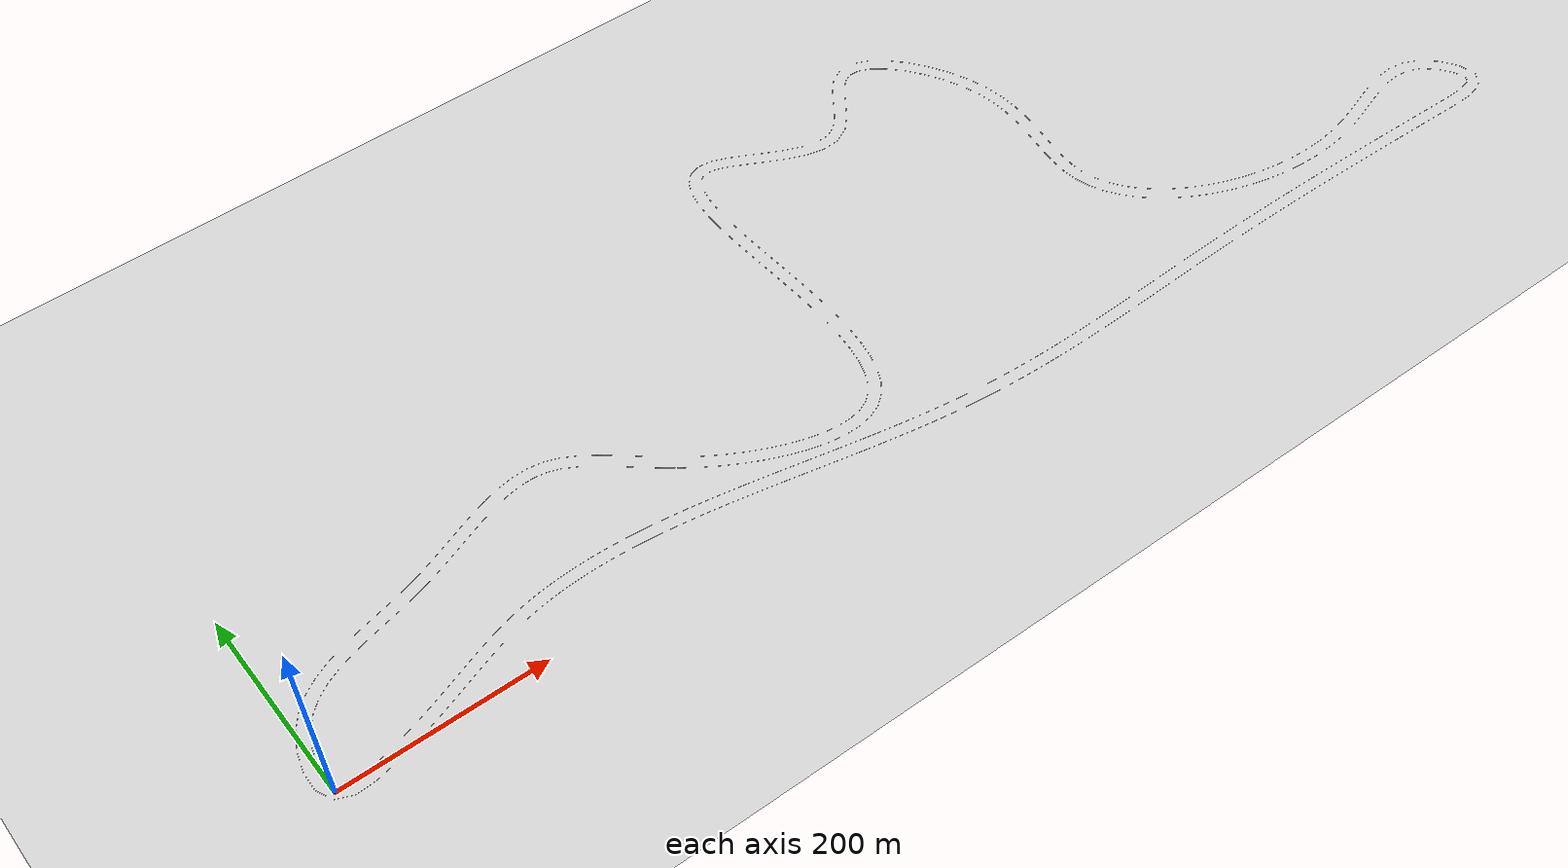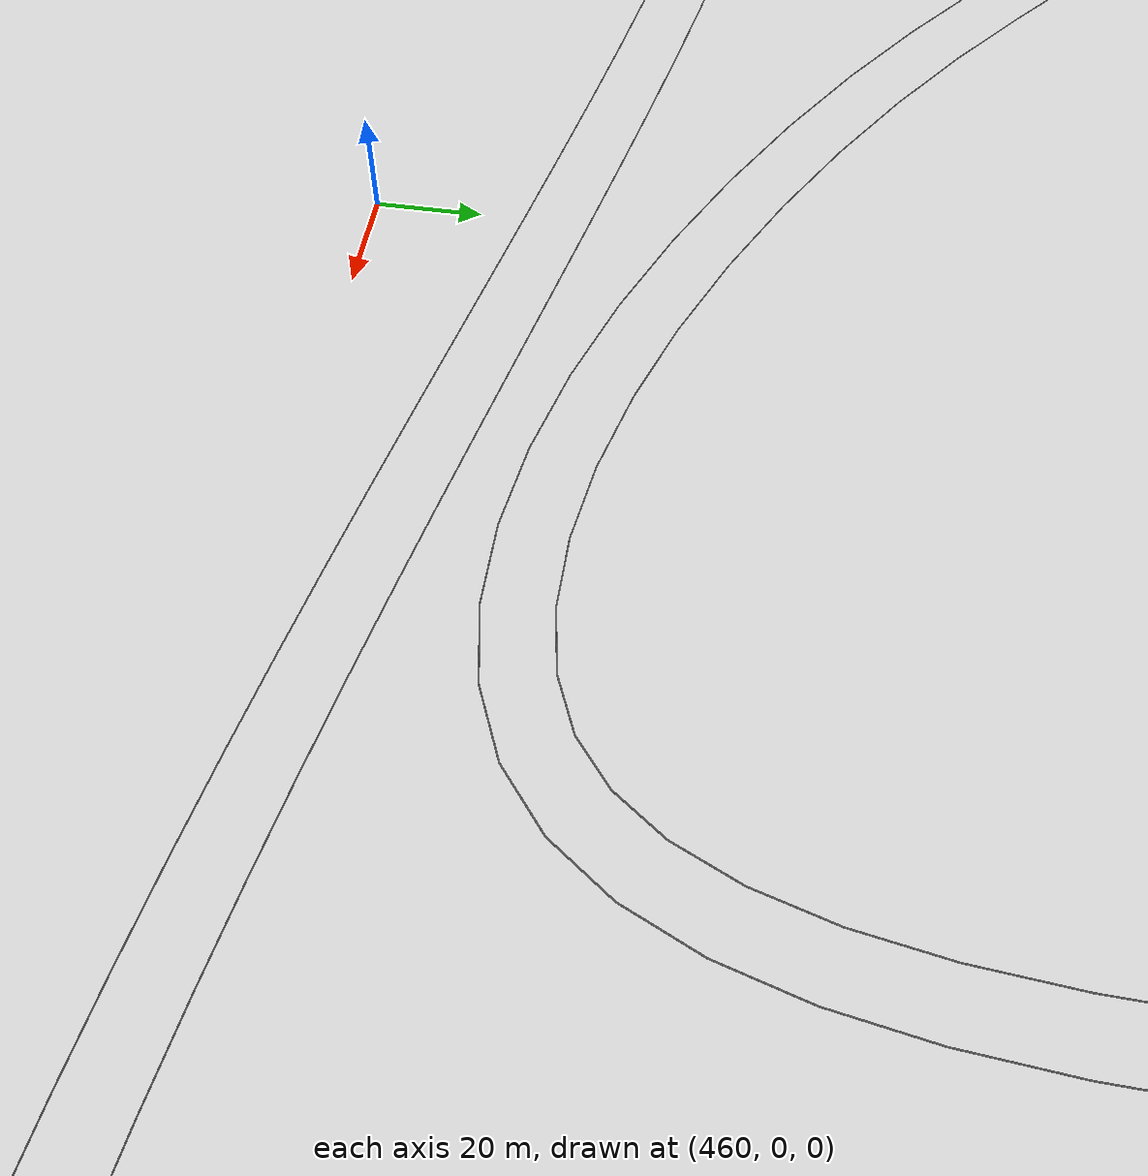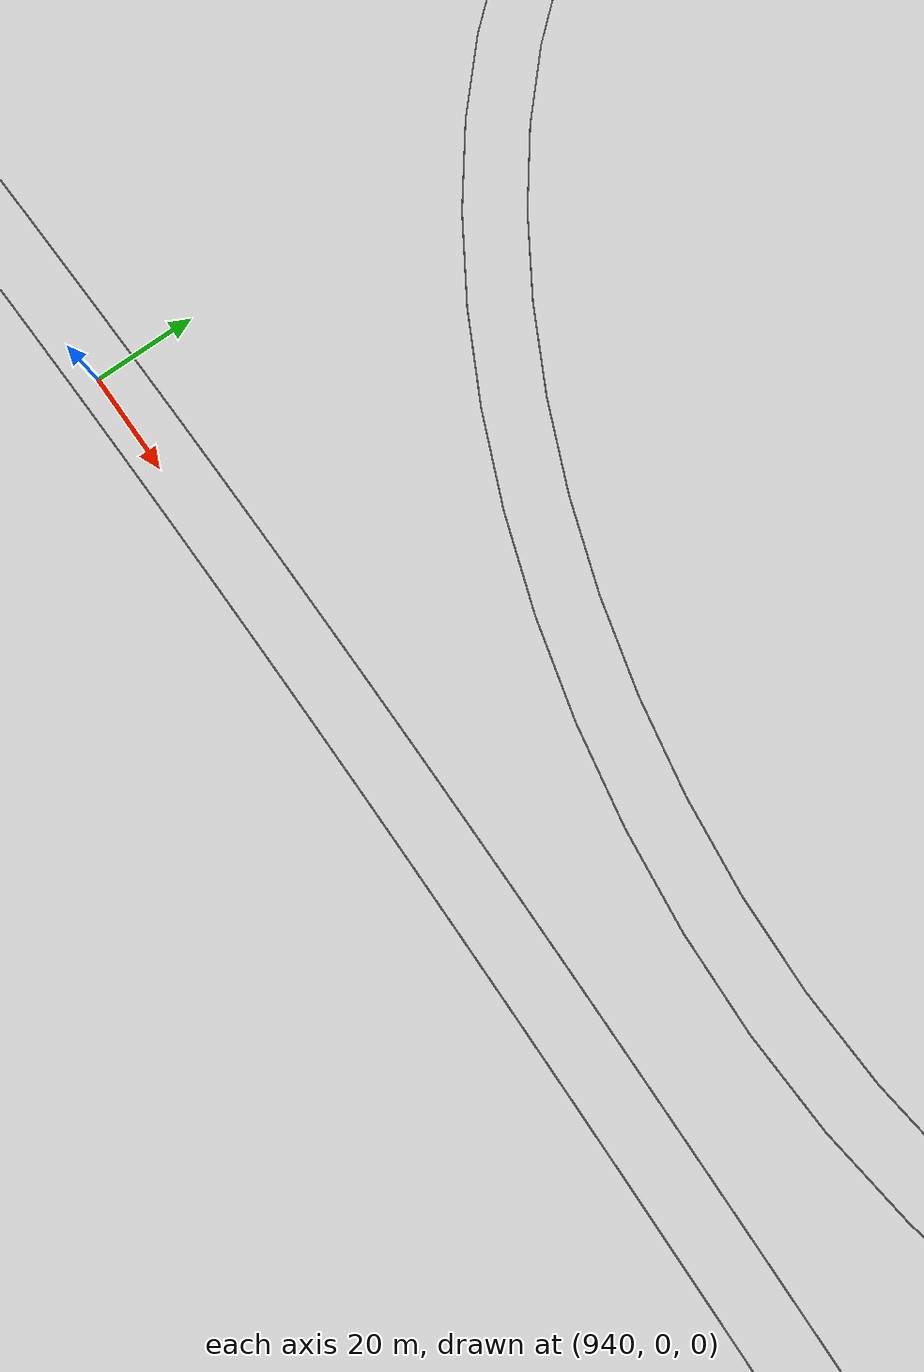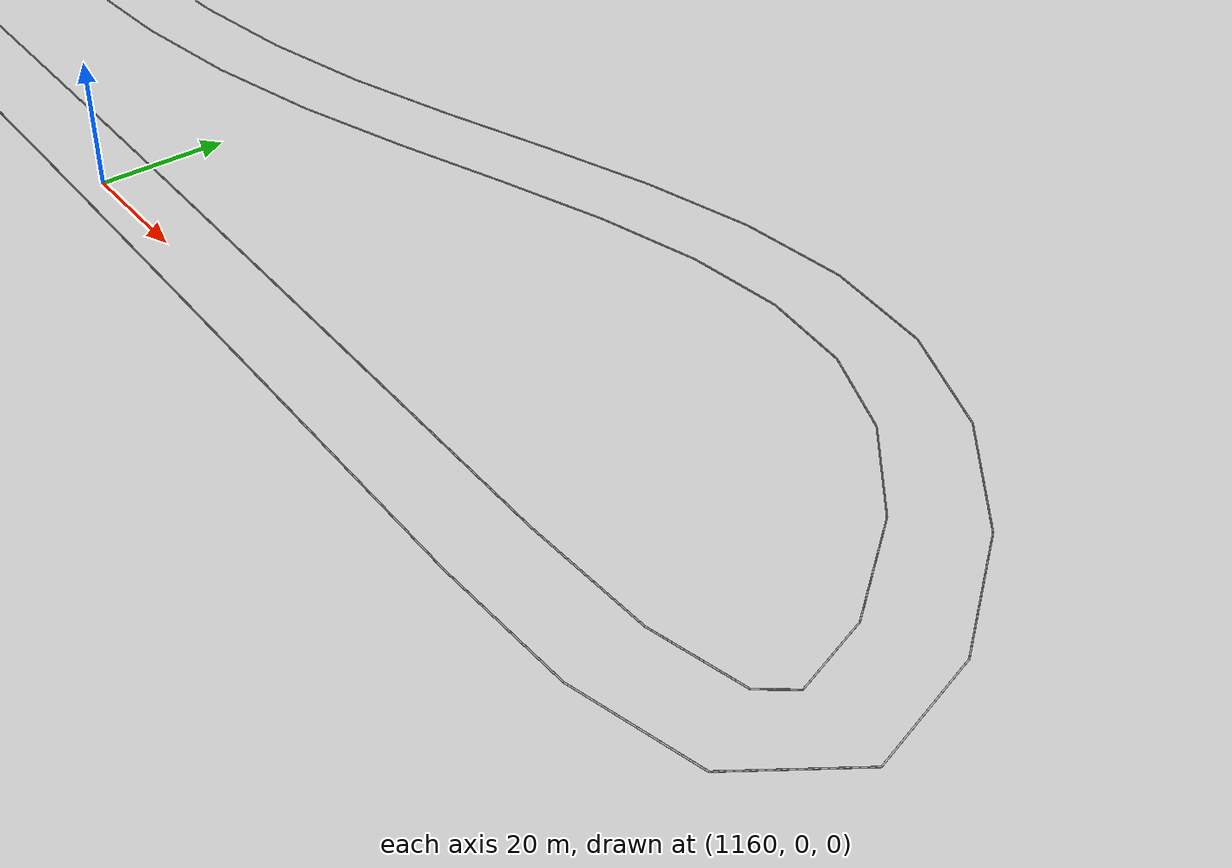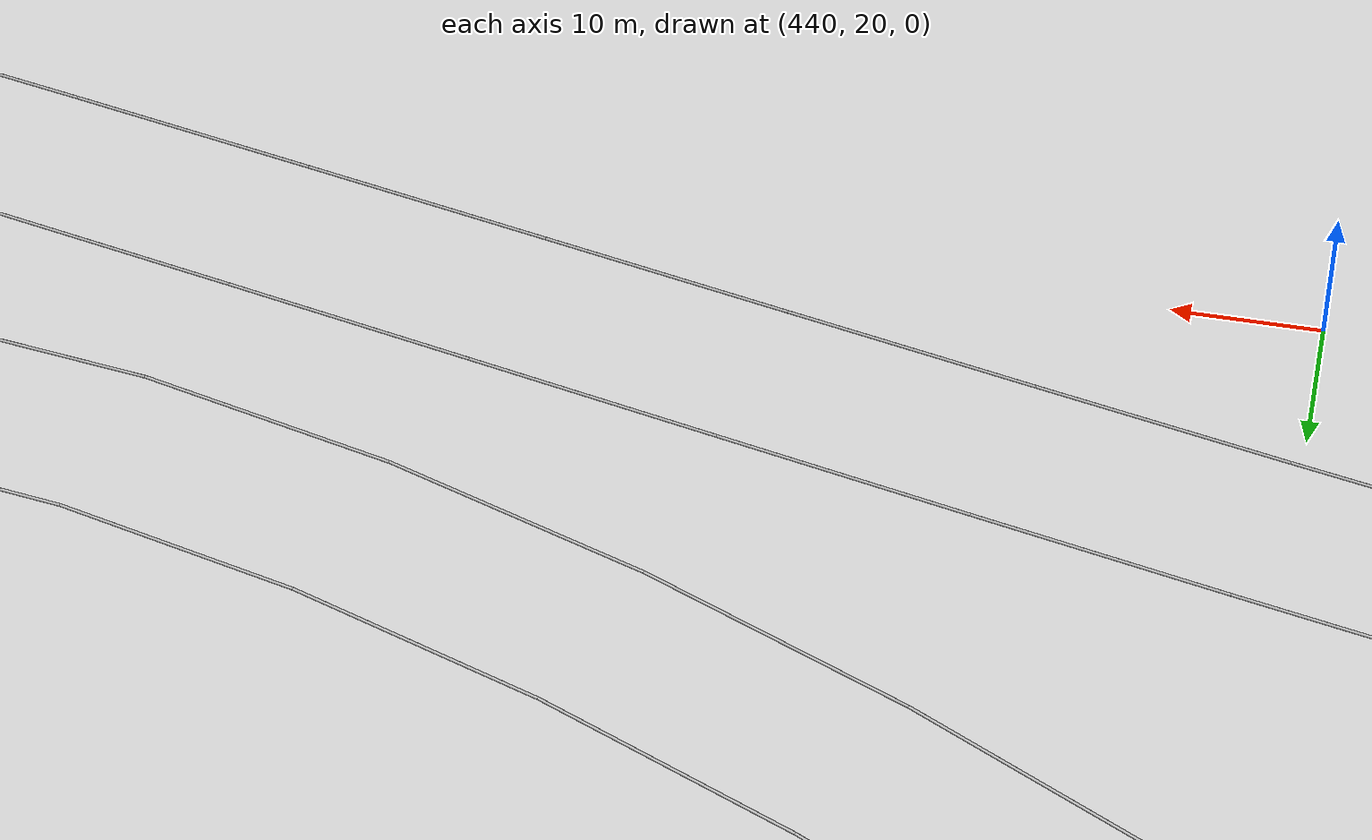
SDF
<?xml version='1.0' encoding='utf-8'?>
<sdf version="1.6">
  <world name="default">
    <model name="ground_plane">
      <static>true</static>
      <link name="link">
        <collision name="collision">
          <geometry>
            <plane>
              <normal>0 0 1</normal>
              <size>5000 5000</size>
            </plane>
          </geometry>
          <surface>
            <friction>
              <ode>
                <mu>50</mu>
              </ode>
              <bullet>
                <friction>1</friction>
                <rolling_friction>0.1</rolling_friction>
              </bullet>
            </friction>
            <bounce />
            <contact />
          </surface>
        </collision>
        <visual name="visual">
          <geometry>
            <plane>
              <normal>0 0 1</normal>
              <size>5000 5000</size>
            </plane>
          </geometry>
          <material>
            <ambient>0.8 0.8 0.8 1</ambient>
            <diffuse>0.8 0.8 0.8 1</diffuse>
            <specular>0.8 0.8 0.8 1</specular>
          </material>
        </visual>
        <pose>0 0 0 0 -0 0</pose>
        <inertial>
          <pose>0 0 0 0 -0 0</pose>
          <mass>1</mass>
          <inertia>
            <ixx>1</ixx>
            <ixy>0</ixy>
            <ixz>0</ixz>
            <iyy>1</iyy>
            <iyz>0</iyz>
            <izz>1</izz>
          </inertia>
        </inertial>
        <enable_wind>false</enable_wind>
      </link>
      <pose>0 0 0 0 -0 0</pose>
      <self_collide>false</self_collide>
    </model>
    <include>
      <uri> file:///home/dliujm/um_files/rob_498_av/AutoVehicle25/audi_ws/src/vehicle_desc/models/lucy </uri>
      <pose> 0 0 0 0 0 0 </pose>
    </include>
    <light name="sun" type="directional">
      <cast_shadows>true</cast_shadows>
      <pose>0 0 10 0 0 0</pose>
      <direction>-0.5 0.5 -1</direction>
    </light>
    <model name="line_model">
      <static>true</static>
      <link name="cylinder_(-4.249021052119533, -4.236250712439601)_(11.908441192839922, -11.194447244828043)">
        <pose>3.8297100703601945 -7.715348978633822 0.05 0 1.5707963267948966 -0.40664573701741885</pose>
        <visual name="visual">
          <geometry>
            <cylinder>
              <radius>0.1</radius>
              <length>17.59204607715182</length>
            </cylinder>
          </geometry>
        </visual>
        <collision name="collision">
          <geometry>
            <cylinder>
              <radius>0.1</radius>
              <length>17.59204607715182</length>
            </cylinder>
          </geometry>
        </collision>
      </link>
      <link name="cylinder_(11.908441192839922, -11.194447244828043)_(30.91994487557768, -10.302703763833609)">
        <pose>21.4141930342088 -10.748575504330827 0.05 0 1.5707963267948966 0.046871114250095575</pose>
        <visual name="visual">
          <geometry>
            <cylinder>
              <radius>0.1</radius>
              <length>19.032406014864424</length>
            </cylinder>
          </geometry>
        </visual>
        <collision name="collision">
          <geometry>
            <cylinder>
              <radius>0.1</radius>
              <length>19.032406014864424</length>
            </cylinder>
          </geometry>
        </collision>
      </link>
      <link name="cylinder_(30.91994487557768, -10.302703763833609)_(50.74517604105659, -6.003794913893742)">
        <pose>40.83256045831713 -8.153249338863676 0.05 0 1.5707963267948966 0.21353447312620455</pose>
        <visual name="visual">
          <geometry>
            <cylinder>
              <radius>0.1</radius>
              <length>20.285965790781752</length>
            </cylinder>
          </geometry>
        </visual>
        <collision name="collision">
          <geometry>
            <cylinder>
              <radius>0.1</radius>
              <length>20.285965790781752</length>
            </cylinder>
          </geometry>
        </collision>
      </link>
      <link name="cylinder_(50.74517604105659, -6.003794913893742)_(69.57900285162896, -0.8009286775584714)">
        <pose>60.162089446342776 -3.4023617957261068 0.05 0 1.5707963267948966 0.269529018725238</pose>
        <visual name="visual">
          <geometry>
            <cylinder>
              <radius>0.1</radius>
              <length>19.53926430047539</length>
            </cylinder>
          </geometry>
        </visual>
        <collision name="collision">
          <geometry>
            <cylinder>
              <radius>0.1</radius>
              <length>19.53926430047539</length>
            </cylinder>
          </geometry>
        </collision>
      </link>
      <link name="cylinder_(69.57900285162896, -0.8009286775584714)_(87.29994601687932, 4.74003907050598)">
        <pose>78.43947443425414 1.9695551964737543 0.05 0 1.5707963267948966 0.30304798415008927</pose>
        <visual name="visual">
          <geometry>
            <cylinder>
              <radius>0.1</radius>
              <length>18.56701780715266</length>
            </cylinder>
          </geometry>
        </visual>
        <collision name="collision">
          <geometry>
            <cylinder>
              <radius>0.1</radius>
              <length>18.56701780715266</length>
            </cylinder>
          </geometry>
        </collision>
      </link>
      <link name="cylinder_(87.29994601687932, 4.74003907050598)_(104.0518536265031, 10.484684190541397)">
        <pose>95.67589982169122 7.612361630523688 0.05 0 1.5707963267948966 0.33035792367139405</pose>
        <visual name="visual">
          <geometry>
            <cylinder>
              <radius>0.1</radius>
              <length>17.709527269707625</length>
            </cylinder>
          </geometry>
        </visual>
        <collision name="collision">
          <geometry>
            <cylinder>
              <radius>0.1</radius>
              <length>17.709527269707625</length>
            </cylinder>
          </geometry>
        </collision>
      </link>
      <link name="cylinder_(104.0518536265031, 10.484684190541397)_(119.97865557862005, 16.29858035329601)">
        <pose>112.01525460256158 13.391632271918704 0.05 0 1.5707963267948966 0.35000884361238</pose>
        <visual name="visual">
          <geometry>
            <cylinder>
              <radius>0.1</radius>
              <length>16.954775404388258</length>
            </cylinder>
          </geometry>
        </visual>
        <collision name="collision">
          <geometry>
            <cylinder>
              <radius>0.1</radius>
              <length>16.954775404388258</length>
            </cylinder>
          </geometry>
        </collision>
      </link>
      <link name="cylinder_(119.97865557862005, 16.29858035329601)_(135.22477881215084, 22.0481331289101)">
        <pose>127.60171719538545 19.173356741103056 0.05 0 1.5707963267948966 0.3606242586592722</pose>
        <visual name="visual">
          <geometry>
            <cylinder>
              <radius>0.1</radius>
              <length>16.294220778287595</length>
            </cylinder>
          </geometry>
        </visual>
        <collision name="collision">
          <geometry>
            <cylinder>
              <radius>0.1</radius>
              <length>16.294220778287595</length>
            </cylinder>
          </geometry>
        </collision>
      </link>
      <link name="cylinder_(135.22477881215084, 22.0481331289101)_(149.9351983817955, 27.60141075305467)">
        <pose>142.57998859697318 24.824771940982384 0.05 0 1.5707963267948966 0.36096625466536514</pose>
        <visual name="visual">
          <geometry>
            <cylinder>
              <radius>0.1</radius>
              <length>15.723718907618796</length>
            </cylinder>
          </geometry>
        </visual>
        <collision name="collision">
          <geometry>
            <cylinder>
              <radius>0.1</radius>
              <length>15.723718907618796</length>
            </cylinder>
          </geometry>
        </collision>
      </link>
      <link name="cylinder_(149.9351983817955, 27.60141075305467)_(164.25564987053394, 32.82898928755648)">
        <pose>157.09542412616472 30.215200020305574 0.05 0 1.5707963267948966 0.35001267400954117</pose>
        <visual name="visual">
          <geometry>
            <cylinder>
              <radius>0.1</radius>
              <length>15.24476658318177</length>
            </cylinder>
          </geometry>
        </visual>
        <collision name="collision">
          <geometry>
            <cylinder>
              <radius>0.1</radius>
              <length>15.24476658318177</length>
            </cylinder>
          </geometry>
        </collision>
      </link>
      <link name="cylinder_(164.25564987053394, 32.82898928755648)_(178.333194081268, 37.60470914795119)">
        <pose>171.29442197590097 35.21684921775383 0.05 0 1.5707963267948966 0.32706052616070125</pose>
        <visual name="visual">
          <geometry>
            <cylinder>
              <radius>0.1</radius>
              <length>14.865555865494589</length>
            </cylinder>
          </geometry>
        </visual>
        <collision name="collision">
          <geometry>
            <cylinder>
              <radius>0.1</radius>
              <length>14.865555865494589</length>
            </cylinder>
          </geometry>
        </collision>
      </link>
      <link name="cylinder_(178.333194081268, 37.60470914795119)_(192.31726768766381, 41.80613617017921)">
        <pose>185.3252308844659 39.7054226590652 0.05 0 1.5707963267948966 0.29186382253843635</pose>
        <visual name="visual">
          <geometry>
            <cylinder>
              <radius>0.1</radius>
              <length>14.601585655407556</length>
            </cylinder>
          </geometry>
        </visual>
        <collision name="collision">
          <geometry>
            <cylinder>
              <radius>0.1</radius>
              <length>14.601585655407556</length>
            </cylinder>
          </geometry>
        </collision>
      </link>
      <link name="cylinder_(192.31726768766381, 41.80613617017921)_(206.36491258416902, 45.31671735044268)">
        <pose>199.34109013591643 43.561426760310944 0.05 0 1.5707963267948966 0.24488954969307244</pose>
        <visual name="visual">
          <geometry>
            <cylinder>
              <radius>0.1</radius>
              <length>14.479658399338321</length>
            </cylinder>
          </geometry>
        </visual>
        <collision name="collision">
          <geometry>
            <cylinder>
              <radius>0.1</radius>
              <length>14.479658399338321</length>
            </cylinder>
          </geometry>
        </collision>
      </link>
      <link name="cylinder_(206.36491258416902, 45.31671735044268)_(220.62787955766498, 48.09466026150759)">
        <pose>213.496396070917 46.705688805975136 0.05 0 1.5707963267948966 0.19235796682162748</pose>
        <visual name="visual">
          <geometry>
            <cylinder>
              <radius>0.1</radius>
              <length>14.530973597944921</length>
            </cylinder>
          </geometry>
        </visual>
        <collision name="collision">
          <geometry>
            <cylinder>
              <radius>0.1</radius>
              <length>14.530973597944921</length>
            </cylinder>
          </geometry>
        </collision>
      </link>
      <link name="cylinder_(220.62787955766498, 48.09466026150759)_(235.12406203221687, 50.176405586906796)">
        <pose>227.87597079494094 49.1355329242072 0.05 0 1.5707963267948966 0.14263129991293735</pose>
        <visual name="visual">
          <geometry>
            <cylinder>
              <radius>0.1</radius>
              <length>14.644895695611039</length>
            </cylinder>
          </geometry>
        </visual>
        <collision name="collision">
          <geometry>
            <cylinder>
              <radius>0.1</radius>
              <length>14.644895695611039</length>
            </cylinder>
          </geometry>
        </collision>
      </link>
      <link name="cylinder_(235.12406203221687, 50.176405586906796)_(249.8461207488298, 51.60124359403968)">
        <pose>242.48509139052334 50.888824590473234 0.05 0 1.5707963267948966 0.09648202874275924</pose>
        <visual name="visual">
          <geometry>
            <cylinder>
              <radius>0.1</radius>
              <length>14.790847717489667</length>
            </cylinder>
          </geometry>
        </visual>
        <collision name="collision">
          <geometry>
            <cylinder>
              <radius>0.1</radius>
              <length>14.790847717489667</length>
            </cylinder>
          </geometry>
        </collision>
      </link>
      <link name="cylinder_(249.8461207488298, 51.60124359403968)_(264.7859372720976, 52.40849577262615)">
        <pose>257.3160290104637 52.00486968333291 0.05 0 1.5707963267948966 0.05398111312979729</pose>
        <visual name="visual">
          <geometry>
            <cylinder>
              <radius>0.1</radius>
              <length>14.961610001224415</length>
            </cylinder>
          </geometry>
        </visual>
        <collision name="collision">
          <geometry>
            <cylinder>
              <radius>0.1</radius>
              <length>14.961610001224415</length>
            </cylinder>
          </geometry>
        </collision>
      </link>
      <link name="cylinder_(264.7859372720976, 52.40849577262615)_(279.934754372947, 52.6376538483141)">
        <pose>272.3603458225223 52.52307481047013 0.05 0 1.5707963267948966 0.015125973014970465</pose>
        <visual name="visual">
          <geometry>
            <cylinder>
              <radius>0.1</radius>
              <length>15.150550253328747</length>
            </cylinder>
          </geometry>
        </visual>
        <collision name="collision">
          <geometry>
            <cylinder>
              <radius>0.1</radius>
              <length>15.150550253328747</length>
            </cylinder>
          </geometry>
        </collision>
      </link>
      <link name="cylinder_(279.934754372947, 52.6376538483141)_(295.283324993398, 52.32846513929506)">
        <pose>287.6090396831725 52.48305949380458 0.05 0 1.5707963267948966 -0.020141738535908126</pose>
        <visual name="visual">
          <geometry>
            <cylinder>
              <radius>0.1</radius>
              <length>15.351684524792624</length>
            </cylinder>
          </geometry>
        </visual>
        <collision name="collision">
          <geometry>
            <cylinder>
              <radius>0.1</radius>
              <length>15.351684524792624</length>
            </cylinder>
          </geometry>
        </collision>
      </link>
      <link name="cylinder_(295.283324993398, 52.32846513929506)_(310.822052246928, 51.52097378915327)">
        <pose>303.05268862016305 51.92471946422417 0.05 0 1.5707963267948966 -0.051919673633761036</pose>
        <visual name="visual">
          <geometry>
            <cylinder>
              <radius>0.1</radius>
              <length>15.559694307413297</length>
            </cylinder>
          </geometry>
        </visual>
        <collision name="collision">
          <geometry>
            <cylinder>
              <radius>0.1</radius>
              <length>15.559694307413297</length>
            </cylinder>
          </geometry>
        </collision>
      </link>
      <link name="cylinder_(310.822052246928, 51.52097378915327)_(326.5411106865815, 50.255529530697714)">
        <pose>318.6815814667548 50.88825165992549 0.05 0 1.5707963267948966 -0.0803305821380422</pose>
        <visual name="visual">
          <geometry>
            <cylinder>
              <radius>0.1</radius>
              <length>15.769912726470572</length>
            </cylinder>
          </geometry>
        </visual>
        <collision name="collision">
          <geometry>
            <cylinder>
              <radius>0.1</radius>
              <length>15.769912726470572</length>
            </cylinder>
          </geometry>
        </collision>
      </link>
      <link name="cylinder_(326.5411106865815, 50.255529530697714)_(342.43054510797344, 48.57277501087925)">
        <pose>334.48582789727743 49.41415227078848 0.05 0 1.5707963267948966 -0.1055107066303795</pose>
        <visual name="visual">
          <geometry>
            <cylinder>
              <radius>0.1</radius>
              <length>15.978291179149458</length>
            </cylinder>
          </geometry>
        </visual>
        <collision name="collision">
          <geometry>
            <cylinder>
              <radius>0.1</radius>
              <length>15.978291179149458</length>
            </cylinder>
          </geometry>
        </collision>
      </link>
      <link name="cylinder_(342.43054510797344, 48.57277501087925)_(358.48034713294163, 46.513620729837896)">
        <pose>350.4554461204575 47.54319787035857 0.05 0 1.5707963267948966 -0.1276007298067149</pose>
        <visual name="visual">
          <geometry>
            <cylinder>
              <radius>0.1</radius>
              <length>16.18135536331255</length>
            </cylinder>
          </geometry>
        </visual>
        <collision name="collision">
          <geometry>
            <cylinder>
              <radius>0.1</radius>
              <length>16.18135536331255</length>
            </cylinder>
          </geometry>
        </collision>
      </link>
      <link name="cylinder_(358.48034713294163, 46.513620729837896)_(374.6805120218593, 44.119214305072674)">
        <pose>366.5804295774004 45.316417517455285 0.05 0 1.5707963267948966 -0.14673899931854106</pose>
        <visual name="visual">
          <geometry>
            <cylinder>
              <radius>0.1</radius>
              <length>16.37615719743423</length>
            </cylinder>
          </geometry>
        </visual>
        <collision name="collision">
          <geometry>
            <cylinder>
              <radius>0.1</radius>
              <length>16.37615719743423</length>
            </cylinder>
          </geometry>
        </collision>
      </link>
      <link name="cylinder_(374.6805120218593, 44.119214305072674)_(391.0210790791441, 41.430908622953936)">
        <pose>382.8507955505017 42.775061464013305 0.05 0 1.5707963267948966 -0.16305665831483235</pose>
        <visual name="visual">
          <geometry>
            <cylinder>
              <radius>0.1</radius>
              <length>16.560227027252196</length>
            </cylinder>
          </geometry>
        </visual>
        <collision name="collision">
          <geometry>
            <cylinder>
              <radius>0.1</radius>
              <length>16.560227027252196</length>
            </cylinder>
          </geometry>
        </collision>
      </link>
      <link name="cylinder_(391.0210790791441, 41.430908622953936)_(407.49215912476006, 38.49023171927874)">
        <pose>399.2566191019521 39.96057017111634 0.05 0 1.5707963267948966 -0.17667429598291576</pose>
        <visual name="visual">
          <geometry>
            <cylinder>
              <radius>0.1</radius>
              <length>16.731528875775133</length>
            </cylinder>
          </geometry>
        </visual>
        <collision name="collision">
          <geometry>
            <cylinder>
              <radius>0.1</radius>
              <length>16.731528875775133</length>
            </cylinder>
          </geometry>
        </collision>
      </link>
      <link name="cylinder_(407.49215912476006, 38.49023171927874)_(424.0839521754821, 35.338859976778465)">
        <pose>415.7880556501211 36.9145458480286 0.05 0 1.5707963267948966 -0.1876997648552637</pose>
        <visual name="visual">
          <geometry>
            <cylinder>
              <radius>0.1</radius>
              <length>16.888420307933423</length>
            </cylinder>
          </geometry>
        </visual>
        <collision name="collision">
          <geometry>
            <cylinder>
              <radius>0.1</radius>
              <length>16.888420307933423</length>
            </cylinder>
          </geometry>
        </collision>
      </link>
      <link name="cylinder_(424.0839521754821, 35.338859976778465)_(440.78675796300803, 32.01859538252162)">
        <pose>432.4353550692451 33.67872767965004 0.05 0 1.5707963267948966 -0.19622686524881214</pose>
        <visual name="visual">
          <geometry>
            <cylinder>
              <radius>0.1</radius>
              <length>17.02961767485355</length>
            </cylinder>
          </geometry>
        </visual>
        <collision name="collision">
          <geometry>
            <cylinder>
              <radius>0.1</radius>
              <length>17.02961767485355</length>
            </cylinder>
          </geometry>
        </collision>
      </link>
      <link name="cylinder_(440.78675796300803, 32.01859538252162)_(457.59098135993014, 28.57134706126849)">
        <pose>449.1888696614691 30.294971221895054 0.05 0 1.5707963267948966 -0.20233465634317832</pose>
        <visual name="visual">
          <geometry>
            <cylinder>
              <radius>0.1</radius>
              <length>17.15416698537259</length>
            </cylinder>
          </geometry>
        </visual>
        <collision name="collision">
          <geometry>
            <cylinder>
              <radius>0.1</radius>
              <length>17.15416698537259</length>
            </cylinder>
          </geometry>
        </collision>
      </link>
      <link name="cylinder_(457.59098135993014, 28.57134706126849)_(474.4871342654577, 25.039117001985282)">
        <pose>466.03905781269395 26.805232031626886 0.05 0 1.5707963267948966 -0.2060872096514758</pose>
        <visual name="visual">
          <geometry>
            <cylinder>
              <radius>0.1</radius>
              <length>17.261420341289174</length>
            </cylinder>
          </geometry>
        </visual>
        <collision name="collision">
          <geometry>
            <cylinder>
              <radius>0.1</radius>
              <length>17.261420341289174</length>
            </cylinder>
          </geometry>
        </collision>
      </link>
      <link name="cylinder_(474.4871342654577, 25.039117001985282)_(491.46583505119344, 21.463989748530402)">
        <pose>482.9764846583256 23.251553375257842 0.05 0 1.5707963267948966 -0.20753367027331943</pose>
        <visual name="visual">
          <geometry>
            <cylinder>
              <radius>0.1</radius>
              <length>17.3510177006981</length>
            </cylinder>
          </geometry>
        </visual>
        <collision name="collision">
          <geometry>
            <cylinder>
              <radius>0.1</radius>
              <length>17.3510177006981</length>
            </cylinder>
          </geometry>
        </collision>
      </link>
      <link name="cylinder_(491.46583505119344, 21.463989748530402)_(508.51780628765573, 17.888125774310854)">
        <pose>499.99182066942456 19.67605776142063 0.05 0 1.5707963267948966 -0.20670853343734089</pose>
        <visual name="visual">
          <geometry>
            <cylinder>
              <radius>0.1</radius>
              <length>17.42287364963824</length>
            </cylinder>
          </geometry>
        </visual>
        <collision name="collision">
          <geometry>
            <cylinder>
              <radius>0.1</radius>
              <length>17.42287364963824</length>
            </cylinder>
          </geometry>
        </collision>
      </link>
      <link name="cylinder_(508.51780628765573, 17.888125774310854)_(525.6338711558502, 14.35375826249076)">
        <pose>517.0758387217529 16.120942018400807 0.05 0 1.5707963267948966 -0.20363207903535804</pose>
        <visual name="visual">
          <geometry>
            <cylinder>
              <radius>0.1</radius>
              <length>17.477168829099604</length>
            </cylinder>
          </geometry>
        </visual>
        <collision name="collision">
          <geometry>
            <cylinder>
              <radius>0.1</radius>
              <length>17.477168829099604</length>
            </cylinder>
          </geometry>
        </collision>
      </link>
      <link name="cylinder_(525.6338711558502, 14.35375826249076)_(542.8049486809786, 10.903193038009348)">
        <pose>534.2194099184144 12.628475650250055 0.05 0 1.5707963267948966 -0.19831093639351546</pose>
        <visual name="visual">
          <geometry>
            <cylinder>
              <radius>0.1</radius>
              <length>17.514345655558134</length>
            </cylinder>
          </geometry>
        </visual>
        <collision name="collision">
          <geometry>
            <cylinder>
              <radius>0.1</radius>
              <length>17.514345655558134</length>
            </cylinder>
          </geometry>
        </collision>
      </link>
      <link name="cylinder_(542.8049486809786, 10.903193038009348)_(560.022047692579, 7.578811423034493)">
        <pose>551.4134981867787 9.241002230521921 0.05 0 1.5707963267948966 -0.19073877687097693</pose>
        <visual name="visual">
          <geometry>
            <cylinder>
              <radius>0.1</radius>
              <length>17.535107969363523</length>
            </cylinder>
          </geometry>
        </visual>
        <collision name="collision">
          <geometry>
            <cylinder>
              <radius>0.1</radius>
              <length>17.535107969363523</length>
            </cylinder>
          </geometry>
        </collision>
      </link>
      <link name="cylinder_(560.022047692579, 7.578811423034493)_(577.2762592043742, 4.42307579578182)">
        <pose>568.6491534484767 6.000943609408156 0.05 0 1.5707963267948966 -0.18089715437474158</pose>
        <visual name="visual">
          <geometry>
            <cylinder>
              <radius>0.1</radius>
              <length>17.54042423212389</length>
            </cylinder>
          </geometry>
        </visual>
        <collision name="collision">
          <geometry>
            <cylinder>
              <radius>0.1</radius>
              <length>17.54042423212389</length>
            </cylinder>
          </geometry>
        </collision>
      </link>
      <link name="cylinder_(577.2762592043742, 4.42307579578182)_(594.5587467090251, 1.4785376078527577)">
        <pose>585.9175029566996 2.9508067018172888 0.05 0 1.5707963267948966 -0.16875653459969644</pose>
        <visual name="visual">
          <geometry>
            <cylinder>
              <radius>0.1</radius>
              <length>17.531533860121428</length>
            </cylinder>
          </geometry>
        </visual>
        <collision name="collision">
          <geometry>
            <cylinder>
              <radius>0.1</radius>
              <length>17.531533860121428</length>
            </cylinder>
          </geometry>
        </collision>
      </link>
      <link name="cylinder_(594.5587467090251, 1.4785376078527577)_(611.8607336949037, -1.2121524587791974)">
        <pose>603.2097402019645 0.13319257453678013 0.05 0 1.5707963267948966 -0.15427757338818882</pose>
        <visual name="visual">
          <geometry>
            <cylinder>
              <radius>0.1</radius>
              <length>17.509956216227007</length>
            </cylinder>
          </geometry>
        </visual>
        <collision name="collision">
          <geometry>
            <cylinder>
              <radius>0.1</radius>
              <length>17.509956216227007</length>
            </cylinder>
          </geometry>
        </collision>
      </link>
      <link name="cylinder_(611.8607336949037, -1.2121524587791974)_(629.1734875187851, -3.6062326544347894)">
        <pose>620.5171106068444 -2.4091925566069934 0.05 0 1.5707963267948966 -0.13741272311234612</pose>
        <visual name="visual">
          <geometry>
            <cylinder>
              <radius>0.1</radius>
              <length>17.47750167928901</length>
            </cylinder>
          </geometry>
        </visual>
        <collision name="collision">
          <geometry>
            <cylinder>
              <radius>0.1</radius>
              <length>17.47750167928901</length>
            </cylinder>
          </geometry>
        </collision>
      </link>
      <link name="cylinder_(629.1734875187851, -3.6062326544347894)_(646.488298625912, -5.660817327848388)">
        <pose>637.8308930723485 -4.633524991141589 0.05 0 1.5707963267948966 -0.11810826268228332</pose>
        <visual name="visual">
          <geometry>
            <cylinder>
              <radius>0.1</radius>
              <length>17.436284060995025</length>
            </cylinder>
          </geometry>
        </visual>
        <collision name="collision">
          <geometry>
            <cylinder>
              <radius>0.1</radius>
              <length>17.436284060995025</length>
            </cylinder>
          </geometry>
        </collision>
      </link>
      <link name="cylinder_(646.488298625912, -5.660817327848388)_(663.7872384263247, -7.339099857343313)">
        <pose>655.1377685261184 -6.499958592595851 0.05 0 1.5707963267948966 -0.09671382420341652</pose>
        <visual name="visual">
          <geometry>
            <cylinder>
              <radius>0.1</radius>
              <length>17.380159678987784</length>
            </cylinder>
          </geometry>
        </visual>
        <collision name="collision">
          <geometry>
            <cylinder>
              <radius>0.1</radius>
              <length>17.380159678987784</length>
            </cylinder>
          </geometry>
        </collision>
      </link>
      <link name="cylinder_(663.7872384263247, -7.339099857343313)_(681.0414912517712, -8.650764845923788)">
        <pose>672.414364839048 -7.994932351633551 0.05 0 1.5707963267948966 -0.07587387399805791</pose>
        <visual name="visual">
          <geometry>
            <cylinder>
              <radius>0.1</radius>
              <length>17.304037263213864</length>
            </cylinder>
          </geometry>
        </visual>
        <collision name="collision">
          <geometry>
            <cylinder>
              <radius>0.1</radius>
              <length>17.304037263213864</length>
            </cylinder>
          </geometry>
        </collision>
      </link>
      <link name="cylinder_(681.0414912517712, -8.650764845923788)_(698.2364428107423, -9.626404442867024)">
        <pose>689.6389670312567 -9.138584644395406 0.05 0 1.5707963267948966 -0.056679113938577</pose>
        <visual name="visual">
          <geometry>
            <cylinder>
              <radius>0.1</radius>
              <length>17.222608157259142</length>
            </cylinder>
          </geometry>
        </visual>
        <collision name="collision">
          <geometry>
            <cylinder>
              <radius>0.1</radius>
              <length>17.222608157259142</length>
            </cylinder>
          </geometry>
        </collision>
      </link>
      <link name="cylinder_(698.2364428107423, -9.626404442867024)_(715.3578515310384, -10.296655577872333)">
        <pose>706.7971471708904 -9.961530010369678 0.05 0 1.5707963267948966 -0.03912698290406189</pose>
        <visual name="visual">
          <geometry>
            <cylinder>
              <radius>0.1</radius>
              <length>17.134522845746375</length>
            </cylinder>
          </geometry>
        </visual>
        <collision name="collision">
          <geometry>
            <cylinder>
              <radius>0.1</radius>
              <length>17.134522845746375</length>
            </cylinder>
          </geometry>
        </collision>
      </link>
      <link name="cylinder_(715.3578515310384, -10.296655577872333)_(732.3914906971584, -10.692105656309485)">
        <pose>723.8746711140984 -10.494380617090908 0.05 0 1.5707963267948966 -0.023211660859680214</pose>
        <visual name="visual">
          <geometry>
            <cylinder>
              <radius>0.1</radius>
              <length>17.03822889874746</length>
            </cylinder>
          </geometry>
        </visual>
        <collision name="collision">
          <geometry>
            <cylinder>
              <radius>0.1</radius>
              <length>17.03822889874746</length>
            </cylinder>
          </geometry>
        </collision>
      </link>
      <link name="cylinder_(732.3914906971584, -10.692105656309485)_(749.3231355480104, -10.843292897933388)">
        <pose>740.8573131225844 -10.767699277121437 0.05 0 1.5707963267948966 -0.008929033475504777</pose>
        <visual name="visual">
          <geometry>
            <cylinder>
              <radius>0.1</radius>
              <length>16.932319833307414</length>
            </cylinder>
          </geometry>
        </visual>
        <collision name="collision">
          <geometry>
            <cylinder>
              <radius>0.1</radius>
              <length>16.932319833307414</length>
            </cylinder>
          </geometry>
        </collision>
      </link>
      <link name="cylinder_(749.3231355480104, -10.843292897933388)_(766.1385514079241, -10.780707350076371)">
        <pose>757.7308434779673 -10.812000124004879 0.05 0 1.5707963267948966 0.0037218977745712193</pose>
        <visual name="visual">
          <geometry>
            <cylinder>
              <radius>0.1</radius>
              <length>16.815532328553722</length>
            </cylinder>
          </geometry>
        </visual>
        <collision name="collision">
          <geometry>
            <cylinder>
              <radius>0.1</radius>
              <length>16.815532328553722</length>
            </cylinder>
          </geometry>
        </collision>
      </link>
      <link name="cylinder_(766.1385514079241, -10.780707350076371)_(782.8234827015892, -10.534792192528565)">
        <pose>774.4810170547566 -10.657749771302468 0.05 0 1.5707963267948966 0.014737690479147674</pose>
        <visual name="visual">
          <geometry>
            <cylinder>
              <radius>0.1</radius>
              <length>16.686743437203038</length>
            </cylinder>
          </geometry>
        </visual>
        <collision name="collision">
          <geometry>
            <cylinder>
              <radius>0.1</radius>
              <length>16.686743437203038</length>
            </cylinder>
          </geometry>
        </collision>
      </link>
      <link name="cylinder_(782.8234827015892, -10.534792192528565)_(799.3636426591131, -10.135944991903157)">
        <pose>791.0935626803512 -10.335368592215861 0.05 0 1.5707963267948966 0.024109193718884862</pose>
        <visual name="visual">
          <geometry>
            <cylinder>
              <radius>0.1</radius>
              <length>16.544968132635468</length>
            </cylinder>
          </geometry>
        </visual>
        <collision name="collision">
          <geometry>
            <cylinder>
              <radius>0.1</radius>
              <length>16.544968132635468</length>
            </cylinder>
          </geometry>
        </collision>
      </link>
      <link name="cylinder_(799.3636426591131, -10.135944991903157)_(815.7447034919313, -9.614518591887812)">
        <pose>807.5541730755222 -9.875231791895484 0.05 0 1.5707963267948966 0.03182030800583169</pose>
        <visual name="visual">
          <geometry>
            <cylinder>
              <radius>0.1</radius>
              <length>16.38935750720948</length>
            </cylinder>
          </geometry>
        </visual>
        <collision name="collision">
          <geometry>
            <cylinder>
              <radius>0.1</radius>
              <length>16.38935750720948</length>
            </cylinder>
          </geometry>
        </collision>
      </link>
      <link name="cylinder_(815.7447034919313, -9.614518591887812)_(831.9522868099027, -9.000821338789796)">
        <pose>823.848495150917 -9.307669965338803 0.05 0 1.5707963267948966 0.03784674112391812</pose>
        <visual name="visual">
          <geometry>
            <cylinder>
              <radius>0.1</radius>
              <length>16.21919792491123</length>
            </cylinder>
          </geometry>
        </visual>
        <collision name="collision">
          <geometry>
            <cylinder>
              <radius>0.1</radius>
              <length>16.21919792491123</length>
            </cylinder>
          </geometry>
        </collision>
      </link>
      <link name="cylinder_(831.9522868099027, -9.000821338789796)_(847.9719540522802, -8.32511633638654)">
        <pose>839.9621204310915 -8.662968837588167 0.05 0 1.5707963267948966 0.04215472752480537</pose>
        <visual name="visual">
          <geometry>
            <cylinder>
              <radius>0.1</radius>
              <length>16.033911431923787</length>
            </cylinder>
          </geometry>
        </visual>
        <collision name="collision">
          <geometry>
            <cylinder>
              <radius>0.1</radius>
              <length>16.033911431923787</length>
            </cylinder>
          </geometry>
        </collision>
      </link>
      <link name="cylinder_(847.9719540522802, -8.32511633638654)_(863.7891967201405, -7.617619397766893)">
        <pose>855.8805753862104 -7.971367867076716 0.05 0 1.5707963267948966 0.04469967890555898</pose>
        <visual name="visual">
          <geometry>
            <cylinder>
              <radius>0.1</radius>
              <length>15.833057744230402</length>
            </cylinder>
          </geometry>
        </visual>
        <collision name="collision">
          <geometry>
            <cylinder>
              <radius>0.1</radius>
              <length>15.833057744230402</length>
            </cylinder>
          </geometry>
        </collision>
      </link>
      <link name="cylinder_(863.7891967201405, -7.617619397766893)_(879.3894262275901, -6.908495311971052)">
        <pose>871.5893114738653 -7.263057354868972 0.05 0 1.5707963267948966 0.04542473437777769</pose>
        <visual name="visual">
          <geometry>
            <cylinder>
              <radius>0.1</radius>
              <length>15.616338164056188</length>
            </cylinder>
          </geometry>
        </visual>
        <collision name="collision">
          <geometry>
            <cylinder>
              <radius>0.1</radius>
              <length>15.616338164056188</length>
            </cylinder>
          </geometry>
        </collision>
      </link>
      <link name="cylinder_(879.3894262275901, -6.908495311971052)_(894.7579632394103, -6.227851966942298)">
        <pose>887.0736947335001 -6.568173639456675 0.05 0 1.5707963267948966 0.044259180603603385</pose>
        <visual name="visual">
          <geometry>
            <cylinder>
              <radius>0.1</radius>
              <length>15.383601829442256</length>
            </cylinder>
          </geometry>
        </visual>
        <collision name="collision">
          <geometry>
            <cylinder>
              <radius>0.1</radius>
              <length>15.383601829442256</length>
            </cylinder>
          </geometry>
        </collision>
      </link>
      <link name="cylinder_(894.7579632394103, -6.227851966942298)_(909.8851884593037, -5.604276135097988)">
        <pose>902.321575849357 -5.916064051020143 0.05 0 1.5707963267948966 0.04119876424800259</pose>
        <visual name="visual">
          <geometry>
            <cylinder>
              <radius>0.1</radius>
              <length>15.140072313943502</length>
            </cylinder>
          </geometry>
        </visual>
        <collision name="collision">
          <geometry>
            <cylinder>
              <radius>0.1</radius>
              <length>15.140072313943502</length>
            </cylinder>
          </geometry>
        </collision>
      </link>
      <link name="cylinder_(909.8851884593037, -5.604276135097988)_(924.8041448687375, -5.0485270574965035)">
        <pose>917.3446666640206 -5.326401596297246 0.05 0 1.5707963267948966 0.03723398701888824</pose>
        <visual name="visual">
          <geometry>
            <cylinder>
              <radius>0.1</radius>
              <length>14.929303981895501</length>
            </cylinder>
          </geometry>
        </visual>
        <collision name="collision">
          <geometry>
            <cylinder>
              <radius>0.1</radius>
              <length>14.929303981895501</length>
            </cylinder>
          </geometry>
        </collision>
      </link>
      <link name="cylinder_(924.8041448687375, -5.0485270574965035)_(939.5659136947581, -4.559489454234866)">
        <pose>932.1850292817478 -4.804008255865685 0.05 0 1.5707963267948966 0.03311654715474169</pose>
        <visual name="visual">
          <geometry>
            <cylinder>
              <radius>0.1</radius>
              <length>14.769867184584957</length>
            </cylinder>
          </geometry>
        </visual>
        <collision name="collision">
          <geometry>
            <cylinder>
              <radius>0.1</radius>
              <length>14.769867184584957</length>
            </cylinder>
          </geometry>
        </collision>
      </link>
      <link name="cylinder_(939.5659136947581, -4.559489454234866)_(954.2213786742384, -4.135835402188134)">
        <pose>946.8936461844983 -4.3476624282115 0.05 0 1.5707963267948966 0.02889953359916891</pose>
        <visual name="visual">
          <geometry>
            <cylinder>
              <radius>0.1</radius>
              <length>14.661587107833444</length>
            </cylinder>
          </geometry>
        </visual>
        <collision name="collision">
          <geometry>
            <cylinder>
              <radius>0.1</radius>
              <length>14.661587107833444</length>
            </cylinder>
          </geometry>
        </collision>
      </link>
      <link name="cylinder_(954.2213786742384, -4.135835402188134)_(968.8214407625512, -3.7762405332056654)">
        <pose>961.5214097183948 -3.9560379676968997 0.05 0 1.5707963267948966 0.024624702322558457</pose>
        <visual name="visual">
          <geometry>
            <cylinder>
              <radius>0.1</radius>
              <length>14.604489770354457</length>
            </cylinder>
          </geometry>
        </visual>
        <collision name="collision">
          <geometry>
            <cylinder>
              <radius>0.1</radius>
              <length>14.604489770354457</length>
            </cylinder>
          </geometry>
        </collision>
      </link>
      <link name="cylinder_(968.8214407625512, -3.7762405332056654)_(983.4170095905126, -3.479384697803022)">
        <pose>976.1192251765319 -3.627812615504344 0.05 0 1.5707963267948966 0.02033596059653863</pose>
        <visual name="visual">
          <geometry>
            <cylinder>
              <radius>0.1</radius>
              <length>14.59858735627429</length>
            </cylinder>
          </geometry>
        </visual>
        <collision name="collision">
          <geometry>
            <cylinder>
              <radius>0.1</radius>
              <length>14.59858735627429</length>
            </cylinder>
          </geometry>
        </collision>
      </link>
      <link name="cylinder_(983.4170095905126, -3.479384697803022)_(998.058994264758, -3.243952312302968)">
        <pose>990.7380019276353 -3.361668505052995 0.05 0 1.5707963267948966 0.01607788179667911</pose>
        <visual name="visual">
          <geometry>
            <cylinder>
              <radius>0.1</radius>
              <length>14.643877342049064</length>
            </cylinder>
          </geometry>
        </visual>
        <collision name="collision">
          <geometry>
            <cylinder>
              <radius>0.1</radius>
              <length>14.643877342049064</length>
            </cylinder>
          </geometry>
        </collision>
      </link>
      <link name="cylinder_(998.058994264758, -3.243952312302968)_(1012.7982941718482, -3.0686323552430332)">
        <pose>1005.4286442183031 -3.156292333773001 0.05 0 1.5707963267948966 0.011894166650527671</pose>
        <visual name="visual">
          <geometry>
            <cylinder>
              <radius>0.1</radius>
              <length>14.740342561775567</length>
            </cylinder>
          </geometry>
        </visual>
        <collision name="collision">
          <geometry>
            <cylinder>
              <radius>0.1</radius>
              <length>14.740342561775567</length>
            </cylinder>
          </geometry>
        </collision>
      </link>
      <link name="cylinder_(1012.7982941718482, -3.0686323552430332)_(1027.685790448197, -2.9521180231533846)">
        <pose>1020.2420423100225 -3.010375189198209 0.05 0 1.5707963267948966 0.007826161708405202</pose>
        <visual name="visual">
          <geometry>
            <cylinder>
              <radius>0.1</radius>
              <length>14.887952208678021</length>
            </cylinder>
          </geometry>
        </visual>
        <collision name="collision">
          <geometry>
            <cylinder>
              <radius>0.1</radius>
              <length>14.887952208678021</length>
            </cylinder>
          </geometry>
        </collision>
      </link>
      <link name="cylinder_(1027.685790448197, -2.9521180231533846)_(1042.7723386987996, -2.893106097438739)">
        <pose>1035.2290645734984 -2.9226120602960615 0.05 0 1.5707963267948966 0.003911539191771664</pose>
        <visual name="visual">
          <geometry>
            <cylinder>
              <radius>0.1</radius>
              <length>15.086663664479879</length>
            </cylinder>
          </geometry>
        </visual>
        <collision name="collision">
          <geometry>
            <cylinder>
              <radius>0.1</radius>
              <length>15.086663664479879</length>
            </cylinder>
          </geometry>
        </collision>
      </link>
      <link name="cylinder_(1042.7723386987996, -2.893106097438739)_(1058.1087634020355, -2.890296105546082)">
        <pose>1050.4405510504175 -2.8917011014924103 0.05 0 1.5707963267948966 0.00018322339890727526</pose>
        <visual name="visual">
          <geometry>
            <cylinder>
              <radius>0.1</radius>
              <length>15.336424960664068</length>
            </cylinder>
          </geometry>
        </visual>
        <collision name="collision">
          <geometry>
            <cylinder>
              <radius>0.1</radius>
              <length>15.336424960664068</length>
            </cylinder>
          </geometry>
        </collision>
      </link>
      <link name="cylinder_(1058.1087634020355, -2.890296105546082)_(1073.7458542511108, -2.9423893760013438)">
        <pose>1065.9273088265732 -2.916342740773713 0.05 0 1.5707963267948966 -0.0033313791066400017</pose>
        <visual name="visual">
          <geometry>
            <cylinder>
              <radius>0.1</radius>
              <length>15.637177620371967</length>
            </cylinder>
          </geometry>
        </visual>
        <collision name="collision">
          <geometry>
            <cylinder>
              <radius>0.1</radius>
              <length>15.637177620371967</length>
            </cylinder>
          </geometry>
        </collision>
      </link>
      <link name="cylinder_(1073.7458542511108, -2.9423893760013438)_(1089.7343644856046, -3.048088087025771)">
        <pose>1081.7401093683577 -2.9952387315135574 0.05 0 1.5707963267948966 -0.006610820500972145</pose>
        <visual name="visual">
          <geometry>
            <cylinder>
              <radius>0.1</radius>
              <length>15.98885961336908</length>
            </cylinder>
          </geometry>
        </visual>
        <collision name="collision">
          <geometry>
            <cylinder>
              <radius>0.1</radius>
              <length>15.98885961336908</length>
            </cylinder>
          </geometry>
        </collision>
      </link>
      <link name="cylinder_(1089.7343644856046, -3.048088087025771)_(1106.1250110878882, -3.2060943945555547)">
        <pose>1097.9296877867464 -3.127091240790663 0.05 0 1.5707963267948966 -0.009639730336424054</pose>
        <visual name="visual">
          <geometry>
            <cylinder>
              <radius>0.1</radius>
              <length>16.391408177279036</length>
            </cylinder>
          </geometry>
        </visual>
        <collision name="collision">
          <geometry>
            <cylinder>
              <radius>0.1</radius>
              <length>16.391408177279036</length>
            </cylinder>
          </geometry>
        </collision>
      </link>
      <link name="cylinder_(1106.1250110878882, -3.2060943945555547)_(1122.968476580367, -3.4151097022526984)">
        <pose>1114.5467438341275 -3.3106020484041263 0.05 0 1.5707963267948966 -0.012408644765352103</pose>
        <visual name="visual">
          <geometry>
            <cylinder>
              <radius>0.1</radius>
              <length>16.844762307470408</length>
            </cylinder>
          </geometry>
        </visual>
        <collision name="collision">
          <geometry>
            <cylinder>
              <radius>0.1</radius>
              <length>16.844762307470408</length>
            </cylinder>
          </geometry>
        </collision>
      </link>
      <link name="cylinder_(1122.968476580367, -3.4151097022526984)_(1140.315412071889, -3.6738341090692614)">
        <pose>1131.641944326128 -3.5444719056609797 0.05 0 1.5707963267948966 -0.014913598152648663</pose>
        <visual name="visual">
          <geometry>
            <cylinder>
              <radius>0.1</radius>
              <length>17.348864783198707</length>
            </cylinder>
          </geometry>
        </visual>
        <collision name="collision">
          <geometry>
            <cylinder>
              <radius>0.1</radius>
              <length>17.348864783198707</length>
            </cylinder>
          </geometry>
        </collision>
      </link>
      <link name="cylinder_(1140.315412071889, -3.6738341090692614)_(1158.2164411662661, -3.980966044146029)">
        <pose>1149.2659266190776 -3.8274000766076455 0.05 0 1.5707963267948966 -0.017155539044257404</pose>
        <visual name="visual">
          <geometry>
            <cylinder>
              <radius>0.1</radius>
              <length>17.90366366594492</length>
            </cylinder>
          </geometry>
        </visual>
        <collision name="collision">
          <geometry>
            <cylinder>
              <radius>0.1</radius>
              <length>17.90366366594492</length>
            </cylinder>
          </geometry>
        </collision>
      </link>
      <link name="cylinder_(1158.2164411662661, -3.980966044146029)_(1176.7221643557166, -4.335202077866283)">
        <pose>1167.4693027609915 -4.158084061006156 0.05 0 1.5707963267948966 -0.019139634468451214</pose>
        <visual name="visual">
          <geometry>
            <cylinder>
              <radius>0.1</radius>
              <length>18.509113267040927</length>
            </cylinder>
          </geometry>
        </visual>
        <collision name="collision">
          <geometry>
            <cylinder>
              <radius>0.1</radius>
              <length>18.509113267040927</length>
            </cylinder>
          </geometry>
        </collision>
      </link>
      <link name="cylinder_(1176.7221643557166, -4.335202077866283)_(1195.883163565282, -4.735236883529746)">
        <pose>1186.3026639604993 -4.535219480698014 0.05 0 1.5707963267948966 -0.02087452199767551</pose>
        <visual name="visual">
          <geometry>
            <cylinder>
              <radius>0.1</radius>
              <length>19.165174628860324</length>
            </cylinder>
          </geometry>
        </visual>
        <collision name="collision">
          <geometry>
            <cylinder>
              <radius>0.1</radius>
              <length>19.165174628860324</length>
            </cylinder>
          </geometry>
        </collision>
      </link>
      <link name="cylinder_(1195.883163565282, -4.735236883529746)_(1215.7500065775353, -5.179763316530696)">
        <pose>1205.8165850714086 -4.957500100030221 0.05 0 1.5707963267948966 -0.022371560010660388</pose>
        <visual name="visual">
          <geometry>
            <cylinder>
              <radius>0.1</radius>
              <length>19.871815594533622</length>
            </cylinder>
          </geometry>
        </visual>
        <collision name="collision">
          <geometry>
            <cylinder>
              <radius>0.1</radius>
              <length>19.871815594533622</length>
            </cylinder>
          </geometry>
        </collision>
      </link>
      <link name="cylinder_(1215.7500065775353, -5.179763316530696)_(1236.3732511379524, -5.667472576146395)">
        <pose>1226.061628857744 -5.423617946338545 0.05 0 1.5707963267948966 -0.02364411531483175</pose>
        <visual name="visual">
          <geometry>
            <cylinder>
              <radius>0.1</radius>
              <length>20.62901055602737</length>
            </cylinder>
          </geometry>
        </visual>
        <collision name="collision">
          <geometry>
            <cylinder>
              <radius>0.1</radius>
              <length>20.62901055602737</length>
            </cylinder>
          </geometry>
        </collision>
      </link>
      <link name="cylinder_(1236.3732511379524, -5.667472576146395)_(1257.811235608756, -6.178366603438624)">
        <pose>1247.0922433733542 -5.922919589792509 0.05 0 1.5707963267948966 -0.023826742846093103</pose>
        <visual name="visual">
          <geometry>
            <cylinder>
              <radius>0.1</radius>
              <length>21.44407122907271</length>
            </cylinder>
          </geometry>
        </visual>
        <collision name="collision">
          <geometry>
            <cylinder>
              <radius>0.1</radius>
              <length>21.44407122907271</length>
            </cylinder>
          </geometry>
        </collision>
      </link>
      <link name="cylinder_(1257.811235608756, -6.178366603438624)_(1278.964564521249, -5.730451484775761)">
        <pose>1268.3879000650027 -5.954409044107193 0.05 0 1.5707963267948966 0.021171523168343864</pose>
        <visual name="visual">
          <geometry>
            <cylinder>
              <radius>0.1</radius>
              <length>21.15807061226607</length>
            </cylinder>
          </geometry>
        </visual>
        <collision name="collision">
          <geometry>
            <cylinder>
              <radius>0.1</radius>
              <length>21.15807061226607</length>
            </cylinder>
          </geometry>
        </collision>
      </link>
      <link name="cylinder_(1278.964564521249, -5.730451484775761)_(1296.8177966242542, -1.4383697907897117)">
        <pose>1287.8911805727516 -3.5844106377827365 0.05 0 1.5707963267948966 0.23593188219633485</pose>
        <visual name="visual">
          <geometry>
            <cylinder>
              <radius>0.1</radius>
              <length>18.361913347786665</length>
            </cylinder>
          </geometry>
        </visual>
        <collision name="collision">
          <geometry>
            <cylinder>
              <radius>0.1</radius>
              <length>18.361913347786665</length>
            </cylinder>
          </geometry>
        </collision>
      </link>
      <link name="cylinder_(1296.8177966242542, -1.4383697907897117)_(1306.6364236745953, 12.70782619576106)">
        <pose>1301.7271101494248 5.6347282024856735 0.05 0 1.5707963267948966 0.9640528906943253</pose>
        <visual name="visual">
          <geometry>
            <cylinder>
              <radius>0.1</radius>
              <length>17.219764749949256</length>
            </cylinder>
          </geometry>
        </visual>
        <collision name="collision">
          <geometry>
            <cylinder>
              <radius>0.1</radius>
              <length>17.219764749949256</length>
            </cylinder>
          </geometry>
        </collision>
      </link>
      <link name="cylinder_(1306.6364236745953, 12.70782619576106)_(1302.1157724533143, 30.610778547621937)">
        <pose>1304.376098063955 21.6593023716915 0.05 0 1.5707963267948966 1.8181347218721573</pose>
        <visual name="visual">
          <geometry>
            <cylinder>
              <radius>0.1</radius>
              <length>18.464885333450365</length>
            </cylinder>
          </geometry>
        </visual>
        <collision name="collision">
          <geometry>
            <cylinder>
              <radius>0.1</radius>
              <length>18.464885333450365</length>
            </cylinder>
          </geometry>
        </collision>
      </link>
      <link name="cylinder_(1302.1157724533143, 30.610778547621937)_(1290.5093585215614, 47.749097545919454)">
        <pose>1296.312565487438 39.179938046770694 0.05 0 1.5707963267948966 2.1660696035708655</pose>
        <visual name="visual">
          <geometry>
            <cylinder>
              <radius>0.1</radius>
              <length>20.698570541044496</length>
            </cylinder>
          </geometry>
        </visual>
        <collision name="collision">
          <geometry>
            <cylinder>
              <radius>0.1</radius>
              <length>20.698570541044496</length>
            </cylinder>
          </geometry>
        </collision>
      </link>
      <link name="cylinder_(1290.5093585215614, 47.749097545919454)_(1275.732845417734, 60.97777010848196)">
        <pose>1283.1211019696477 54.36343382720071 0.05 0 1.5707963267948966 2.411408097916455</pose>
        <visual name="visual">
          <geometry>
            <cylinder>
              <radius>0.1</radius>
              <length>19.832879702026954</length>
            </cylinder>
          </geometry>
        </visual>
        <collision name="collision">
          <geometry>
            <cylinder>
              <radius>0.1</radius>
              <length>19.832879702026954</length>
            </cylinder>
          </geometry>
        </collision>
      </link>
      <link name="cylinder_(1275.732845417734, 60.97777010848196)_(1259.66437591292, 68.4285203955191)">
        <pose>1267.6986106653271 64.70314525200052 0.05 0 1.5707963267948966 2.7074145870735364</pose>
        <visual name="visual">
          <geometry>
            <cylinder>
              <radius>0.1</radius>
              <length>17.71184327129526</length>
            </cylinder>
          </geometry>
        </visual>
        <collision name="collision">
          <geometry>
            <cylinder>
              <radius>0.1</radius>
              <length>17.71184327129526</length>
            </cylinder>
          </geometry>
        </collision>
      </link>
      <link name="cylinder_(1259.66437591292, 68.4285203955191)_(1242.9264731617416, 70.77410164983205)">
        <pose>1251.2954245373307 69.60131102267557 0.05 0 1.5707963267948966 3.002363416006614</pose>
        <visual name="visual">
          <geometry>
            <cylinder>
              <radius>0.1</radius>
              <length>16.901453781509097</length>
            </cylinder>
          </geometry>
        </visual>
        <collision name="collision">
          <geometry>
            <cylinder>
              <radius>0.1</radius>
              <length>16.901453781509097</length>
            </cylinder>
          </geometry>
        </collision>
      </link>
      <link name="cylinder_(1242.9264731617416, 70.77410164983205)_(1225.940692664898, 69.22670162820596)">
        <pose>1234.4335829133197 70.000401639019 0.05 0 1.5707963267948966 -3.050743692901657</pose>
        <visual name="visual">
          <geometry>
            <cylinder>
              <radius>0.1</radius>
              <length>17.056118723609952</length>
            </cylinder>
          </geometry>
        </visual>
        <collision name="collision">
          <geometry>
            <cylinder>
              <radius>0.1</radius>
              <length>17.056118723609952</length>
            </cylinder>
          </geometry>
        </collision>
      </link>
      <link name="cylinder_(1225.940692664898, 69.22670162820596)_(1208.7566260818448, 65.05474617164371)">
        <pose>1217.3486593733714 67.14072389992484 0.05 0 1.5707963267948966 -2.903420316026533</pose>
        <visual name="visual">
          <geometry>
            <cylinder>
              <radius>0.1</radius>
              <length>17.683250737982128</length>
            </cylinder>
          </geometry>
        </visual>
        <collision name="collision">
          <geometry>
            <cylinder>
              <radius>0.1</radius>
              <length>17.683250737982128</length>
            </cylinder>
          </geometry>
        </collision>
      </link>
      <link name="cylinder_(1208.7566260818448, 65.05474617164371)_(1191.299484954509, 59.38243972498735)">
        <pose>1200.0280555181769 62.21859294831553 0.05 0 1.5707963267948966 -2.8274262663060314</pose>
        <visual name="visual">
          <geometry>
            <cylinder>
              <radius>0.1</radius>
              <length>18.355566914821875</length>
            </cylinder>
          </geometry>
        </visual>
        <collision name="collision">
          <geometry>
            <cylinder>
              <radius>0.1</radius>
              <length>18.355566914821875</length>
            </cylinder>
          </geometry>
        </collision>
      </link>
      <link name="cylinder_(1191.299484954509, 59.38243972498735)_(1173.525083056353, 53.23952500630975)">
        <pose>1182.412284005431 56.31098236564855 0.05 0 1.5707963267948966 -2.808838928882082</pose>
        <visual name="visual">
          <geometry>
            <cylinder>
              <radius>0.1</radius>
              <length>18.805976817972393</length>
            </cylinder>
          </geometry>
        </visual>
        <collision name="collision">
          <geometry>
            <cylinder>
              <radius>0.1</radius>
              <length>18.805976817972393</length>
            </cylinder>
          </geometry>
        </collision>
      </link>
      <link name="cylinder_(1173.525083056353, 53.23952500630975)_(1155.4418601672032, 47.61281783702551)">
        <pose>1164.483471611778 50.42617142166763 0.05 0 1.5707963267948966 -2.839932485316586</pose>
        <visual name="visual">
          <geometry>
            <cylinder>
              <radius>0.1</radius>
              <length>18.938394431090078</length>
            </cylinder>
          </geometry>
        </visual>
        <collision name="collision">
          <geometry>
            <cylinder>
              <radius>0.1</radius>
              <length>18.938394431090078</length>
            </cylinder>
          </geometry>
        </collision>
      </link>
      <link name="cylinder_(1155.4418601672032, 47.61281783702551)_(1137.0356340528408, 43.40110366181804)">
        <pose>1146.238747110022 45.50696074942178 0.05 0 1.5707963267948966 -2.916645190047725</pose>
        <visual name="visual">
          <geometry>
            <cylinder>
              <radius>0.1</radius>
              <length>18.88194100368606</length>
            </cylinder>
          </geometry>
        </visual>
        <collision name="collision">
          <geometry>
            <cylinder>
              <radius>0.1</radius>
              <length>18.88194100368606</length>
            </cylinder>
          </geometry>
        </collision>
      </link>
      <link name="cylinder_(1137.0356340528408, 43.40110366181804)_(1118.1949316952812, 40.88435412354135)">
        <pose>1127.615282874061 42.1427288926797 0.05 0 1.5707963267948966 -3.0087983269038845</pose>
        <visual name="visual">
          <geometry>
            <cylinder>
              <radius>0.1</radius>
              <length>19.008053387040153</length>
            </cylinder>
          </geometry>
        </visual>
        <collision name="collision">
          <geometry>
            <cylinder>
              <radius>0.1</radius>
              <length>19.008053387040153</length>
            </cylinder>
          </geometry>
        </collision>
      </link>
      <link name="cylinder_(1118.1949316952812, 40.88435412354135)_(1099.076820921265, 39.99303500268271)">
        <pose>1108.635876308273 40.43869456311203 0.05 0 1.5707963267948966 -3.095004672877772</pose>
        <visual name="visual">
          <geometry>
            <cylinder>
              <radius>0.1</radius>
              <length>19.138876909128307</length>
            </cylinder>
          </geometry>
        </visual>
        <collision name="collision">
          <geometry>
            <cylinder>
              <radius>0.1</radius>
              <length>19.138876909128307</length>
            </cylinder>
          </geometry>
        </collision>
      </link>
      <link name="cylinder_(1099.076820921265, 39.99303500268271)_(1079.8652220753963, 40.65221279481578)">
        <pose>1089.4710214983306 40.32262389874924 0.05 0 1.5707963267948966 3.107294659860771</pose>
        <visual name="visual">
          <geometry>
            <cylinder>
              <radius>0.1</radius>
              <length>19.22290419203667</length>
            </cylinder>
          </geometry>
        </visual>
        <collision name="collision">
          <geometry>
            <cylinder>
              <radius>0.1</radius>
              <length>19.22290419203667</length>
            </cylinder>
          </geometry>
        </collision>
      </link>
      <link name="cylinder_(1079.8652220753963, 40.65221279481578)_(1060.745752576311, 42.78450897590766)">
        <pose>1070.3054873258536 41.71836088536172 0.05 0 1.5707963267948966 3.030526746693869</pose>
        <visual name="visual">
          <geometry>
            <cylinder>
              <radius>0.1</radius>
              <length>19.238004078655273</length>
            </cylinder>
          </geometry>
        </visual>
        <collision name="collision">
          <geometry>
            <cylinder>
              <radius>0.1</radius>
              <length>19.238004078655273</length>
            </cylinder>
          </geometry>
        </collision>
      </link>
      <link name="cylinder_(1060.745752576311, 42.78450897590766)_(1041.904945715348, 46.31012509128226)">
        <pose>1051.3253491458295 44.547317033594965 0.05 0 1.5707963267948966 2.9566054471741015</pose>
        <visual name="visual">
          <geometry>
            <cylinder>
              <radius>0.1</radius>
              <length>19.167836919305582</length>
            </cylinder>
          </geometry>
        </visual>
        <collision name="collision">
          <geometry>
            <cylinder>
              <radius>0.1</radius>
              <length>19.167836919305582</length>
            </cylinder>
          </geometry>
        </collision>
      </link>
      <link name="cylinder_(1041.904945715348, 46.31012509128226)_(1023.5297635803207, 51.14691320290366)">
        <pose>1032.7173546478343 48.72851914709296 0.05 0 1.5707963267948966 2.8842071580682296</pose>
        <visual name="visual">
          <geometry>
            <cylinder>
              <radius>0.1</radius>
              <length>19.001100961053538</length>
            </cylinder>
          </geometry>
        </visual>
        <collision name="collision">
          <geometry>
            <cylinder>
              <radius>0.1</radius>
              <length>19.001100961053538</length>
            </cylinder>
          </geometry>
        </collision>
      </link>
      <link name="cylinder_(1023.5297635803207, 51.14691320290366)_(1005.8072947724249, 57.210365949289184)">
        <pose>1014.6685291763729 54.17863957609642 0.05 0 1.5707963267948966 2.811942843535704</pose>
        <visual name="visual">
          <geometry>
            <cylinder>
              <radius>0.1</radius>
              <length>18.731026663119376</length>
            </cylinder>
          </geometry>
        </visual>
        <collision name="collision">
          <geometry>
            <cylinder>
              <radius>0.1</radius>
              <length>18.731026663119376</length>
            </cylinder>
          </geometry>
        </collision>
      </link>
      <link name="cylinder_(1005.8072947724249, 57.210365949289184)_(988.9245187395297, 64.41345334439175)">
        <pose>997.3659067559773 60.81190964684047 0.05 0 1.5707963267948966 2.7383227161611643</pose>
        <visual name="visual">
          <geometry>
            <cylinder>
              <radius>0.1</radius>
              <length>18.35517895849524</length>
            </cylinder>
          </geometry>
        </visual>
        <collision name="collision">
          <geometry>
            <cylinder>
              <radius>0.1</radius>
              <length>18.35517895849524</length>
            </cylinder>
          </geometry>
        </collision>
      </link>
      <link name="cylinder_(988.9245187395297, 64.41345334439175)_(973.0680030457754, 72.66626633235028)">
        <pose>980.9962608926526 68.53985983837102 0.05 0 1.5707963267948966 2.6617048468655815</pose>
        <visual name="visual">
          <geometry>
            <cylinder>
              <radius>0.1</radius>
              <length>17.875626203310862</length>
            </cylinder>
          </geometry>
        </visual>
        <collision name="collision">
          <geometry>
            <cylinder>
              <radius>0.1</radius>
              <length>17.875626203310862</length>
            </cylinder>
          </geometry>
        </collision>
      </link>
      <link name="cylinder_(973.0680030457754, 72.66626633235028)_(958.423356423353, 81.87546430091905)">
        <pose>965.7456797345642 77.27086531663466 0.05 0 1.5707963267948966 2.5802338972796313</pose>
        <visual name="visual">
          <geometry>
            <cylinder>
              <radius>0.1</radius>
              <length>17.29956652404679</length>
            </cylinder>
          </geometry>
        </visual>
        <collision name="collision">
          <geometry>
            <cylinder>
              <radius>0.1</radius>
              <length>17.29956652404679</length>
            </cylinder>
          </geometry>
        </collision>
      </link>
      <link name="cylinder_(958.423356423353, 81.87546430091905)_(945.1741767758333, 91.94360811782985)">
        <pose>951.7987665995931 86.90953620937445 0.05 0 1.5707963267948966 2.4917811830321637</pose>
        <visual name="visual">
          <geometry>
            <cylinder>
              <radius>0.1</radius>
              <length>16.64056132617673</length>
            </cylinder>
          </geometry>
        </visual>
        <collision name="collision">
          <geometry>
            <cylinder>
              <radius>0.1</radius>
              <length>16.64056132617673</length>
            </cylinder>
          </geometry>
        </collision>
      </link>
      <link name="cylinder_(945.1741767758333, 91.94360811782985)_(933.5001215523648, 102.7686705468125)">
        <pose>939.3371491640991 97.35613933232118 0.05 0 1.5707963267948966 2.3939110883942516</pose>
        <visual name="visual">
          <geometry>
            <cylinder>
              <radius>0.1</radius>
              <length>15.920601180607582</length>
            </cylinder>
          </geometry>
        </visual>
        <collision name="collision">
          <geometry>
            <cylinder>
              <radius>0.1</radius>
              <length>15.920601180607582</length>
            </cylinder>
          </geometry>
        </collision>
      </link>
      <link name="cylinder_(933.5001215523648, 102.7686705468125)_(923.5736868801403, 114.24447684023615)">
        <pose>928.5369042162525 108.50657369352433 0.05 0 1.5707963267948966 2.283927596070558</pose>
        <visual name="visual">
          <geometry>
            <cylinder>
              <radius>0.1</radius>
              <length>15.17327372013448</length>
            </cylinder>
          </geometry>
        </visual>
        <collision name="collision">
          <geometry>
            <cylinder>
              <radius>0.1</radius>
              <length>15.17327372013448</length>
            </cylinder>
          </geometry>
        </collision>
      </link>
      <link name="cylinder_(923.5736868801403, 114.24447684023615)_(915.5556421833369, 126.26362748936374)">
        <pose>919.5646645317386 120.25405216479994 0.05 0 1.5707963267948966 2.1591028603740927</pose>
        <visual name="visual">
          <geometry>
            <cylinder>
              <radius>0.1</radius>
              <length>14.448149469269792</length>
            </cylinder>
          </geometry>
        </visual>
        <collision name="collision">
          <geometry>
            <cylinder>
              <radius>0.1</radius>
              <length>14.448149469269792</length>
            </cylinder>
          </geometry>
        </collision>
      </link>
      <link name="cylinder_(915.5556421833369, 126.26362748936374)_(909.5905312047473, 138.72522750836166)">
        <pose>912.5730866940421 132.4944274988627 0.05 0 1.5707963267948966 2.017242423860497</pose>
        <visual name="visual">
          <geometry>
            <cylinder>
              <radius>0.1</radius>
              <length>13.815716558339583</length>
            </cylinder>
          </geometry>
        </visual>
        <collision name="collision">
          <geometry>
            <cylinder>
              <radius>0.1</radius>
              <length>13.815716558339583</length>
            </cylinder>
          </geometry>
        </collision>
      </link>
      <link name="cylinder_(909.5905312047473, 138.72522750836166)_(905.8067326967499, 151.54883601614407)">
        <pose>907.6986319507487 145.13703176225286 0.05 0 1.5707963267948966 1.857719504755682</pose>
        <visual name="visual">
          <geometry>
            <cylinder>
              <radius>0.1</radius>
              <length>13.370193203914175</length>
            </cylinder>
          </geometry>
        </visual>
        <collision name="collision">
          <geometry>
            <cylinder>
              <radius>0.1</radius>
              <length>13.370193203914175</length>
            </cylinder>
          </geometry>
        </collision>
      </link>
      <link name="cylinder_(905.8067326967499, 151.54883601614407)_(904.1822750461488, 164.87984557937398)">
        <pose>904.9945038714493 158.214340797759 0.05 0 1.5707963267948966 1.6920540696821837</pose>
        <visual name="visual">
          <geometry>
            <cylinder>
              <radius>0.1</radius>
              <length>13.42961945229737</length>
            </cylinder>
          </geometry>
        </visual>
        <collision name="collision">
          <geometry>
            <cylinder>
              <radius>0.1</radius>
              <length>13.42961945229737</length>
            </cylinder>
          </geometry>
        </collision>
      </link>
      <link name="cylinder_(904.1822750461488, 164.87984557937398)_(904.2906840644926, 178.95092243744915)">
        <pose>904.2364795553207 171.91538400841156 0.05 0 1.5707963267948966 1.5630920924603053</pose>
        <visual name="visual">
          <geometry>
            <cylinder>
              <radius>0.1</radius>
              <length>14.07149446438142</length>
            </cylinder>
          </geometry>
        </visual>
        <collision name="collision">
          <geometry>
            <cylinder>
              <radius>0.1</radius>
              <length>14.07149446438142</length>
            </cylinder>
          </geometry>
        </collision>
      </link>
      <link name="cylinder_(904.2906840644926, 178.95092243744915)_(905.6203577957187, 193.80073374426146)">
        <pose>904.9555209301056 186.3758280908553 0.05 0 1.5707963267948966 1.4814930304653402</pose>
        <visual name="visual">
          <geometry>
            <cylinder>
              <radius>0.1</radius>
              <length>14.909222920039925</length>
            </cylinder>
          </geometry>
        </visual>
        <collision name="collision">
          <geometry>
            <cylinder>
              <radius>0.1</radius>
              <length>14.909222920039925</length>
            </cylinder>
          </geometry>
        </collision>
      </link>
      <link name="cylinder_(905.6203577957187, 193.80073374426146)_(907.6170952618627, 209.43576841453293)">
        <pose>906.6187265287907 201.6182510793972 0.05 0 1.5707963267948966 1.44377472683457</pose>
        <visual name="visual">
          <geometry>
            <cylinder>
              <radius>0.1</radius>
              <length>15.762019846748503</length>
            </cylinder>
          </geometry>
        </visual>
        <collision name="collision">
          <geometry>
            <cylinder>
              <radius>0.1</radius>
              <length>15.762019846748503</length>
            </cylinder>
          </geometry>
        </collision>
      </link>
      <link name="cylinder_(907.6170952618627, 209.43576841453293)_(909.6914392449532, 225.86370745235962)">
        <pose>908.654267253408 217.64973793344626 0.05 0 1.5707963267948966 1.4451917785495267</pose>
        <visual name="visual">
          <geometry>
            <cylinder>
              <radius>0.1</radius>
              <length>16.558384099625606</length>
            </cylinder>
          </geometry>
        </visual>
        <collision name="collision">
          <geometry>
            <cylinder>
              <radius>0.1</radius>
              <length>16.558384099625606</length>
            </cylinder>
          </geometry>
        </collision>
      </link>
      <link name="cylinder_(909.6914392449532, 225.86370745235962)_(911.229677737367, 243.10024388432606)">
        <pose>910.4605584911601 234.48197566834284 0.05 0 1.5707963267948966 1.4817892202660021</pose>
        <visual name="visual">
          <geometry>
            <cylinder>
              <radius>0.1</radius>
              <length>17.305038741073353</length>
            </cylinder>
          </geometry>
        </visual>
        <collision name="collision">
          <geometry>
            <cylinder>
              <radius>0.1</radius>
              <length>17.305038741073353</length>
            </cylinder>
          </geometry>
        </collision>
      </link>
      <link name="cylinder_(911.229677737367, 243.10024388432606)_(911.6008258537199, 261.1618888143663)">
        <pose>911.4152517955434 252.13106634934618 0.05 0 1.5707963267948966 1.550250253018674</pose>
        <visual name="visual">
          <geometry>
            <cylinder>
              <radius>0.1</radius>
              <length>18.065457882465115</length>
            </cylinder>
          </geometry>
        </visual>
        <collision name="collision">
          <geometry>
            <cylinder>
              <radius>0.1</radius>
              <length>18.065457882465115</length>
            </cylinder>
          </geometry>
        </collision>
      </link>
      <link name="cylinder_(911.6008258537199, 261.1618888143663)_(910.1640669952204, 280.05310869900006)">
        <pose>910.8824464244701 270.6074987566832 0.05 0 1.5707963267948966 1.6467045130591644</pose>
        <visual name="visual">
          <geometry>
            <cylinder>
              <radius>0.1</radius>
              <length>18.945776963404235</length>
            </cylinder>
          </geometry>
        </visual>
        <collision name="collision">
          <geometry>
            <cylinder>
              <radius>0.1</radius>
              <length>18.945776963404235</length>
            </cylinder>
          </geometry>
        </collision>
      </link>
      <link name="cylinder_(910.1640669952204, 280.05310869900006)_(906.2822141517893, 299.7560342773683)">
        <pose>908.2231405735049 289.90457148818416 0.05 0 1.5707963267948966 1.765324009213745</pose>
        <visual name="visual">
          <geometry>
            <cylinder>
              <radius>0.1</radius>
              <length>20.081684636622803</length>
            </cylinder>
          </geometry>
        </visual>
        <collision name="collision">
          <geometry>
            <cylinder>
              <radius>0.1</radius>
              <length>20.081684636622803</length>
            </cylinder>
          </geometry>
        </collision>
      </link>
      <link name="cylinder_(906.2822141517893, 299.7560342773683)_(899.5124162003578, 320.0422478893094)">
        <pose>902.8973151760736 309.89914108333886 0.05 0 1.5707963267948966 1.8928896399755815</pose>
        <visual name="visual">
          <geometry>
            <cylinder>
              <radius>0.1</radius>
              <length>21.385991373151473</length>
            </cylinder>
          </geometry>
        </visual>
        <collision name="collision">
          <geometry>
            <cylinder>
              <radius>0.1</radius>
              <length>21.385991373151473</length>
            </cylinder>
          </geometry>
        </collision>
      </link>
      <link name="cylinder_(899.5124162003578, 320.0422478893094)_(890.1974079344793, 340.1449712968478)">
        <pose>894.8549120674186 330.0936095930786 0.05 0 1.5707963267948966 2.004713333865637</pose>
        <visual name="visual">
          <geometry>
            <cylinder>
              <radius>0.1</radius>
              <length>22.156011992084178</length>
            </cylinder>
          </geometry>
        </visual>
        <collision name="collision">
          <geometry>
            <cylinder>
              <radius>0.1</radius>
              <length>22.156011992084178</length>
            </cylinder>
          </geometry>
        </collision>
      </link>
      <link name="cylinder_(890.1974079344793, 340.1449712968478)_(878.8644706328553, 359.24791481268414)">
        <pose>884.5309392836673 349.69644305476595 0.05 0 1.5707963267948966 2.106242302440099</pose>
        <visual name="visual">
          <geometry>
            <cylinder>
              <radius>0.1</radius>
              <length>22.211661776008</length>
            </cylinder>
          </geometry>
        </visual>
        <collision name="collision">
          <geometry>
            <cylinder>
              <radius>0.1</radius>
              <length>22.211661776008</length>
            </cylinder>
          </geometry>
        </collision>
      </link>
      <link name="cylinder_(878.8644706328553, 359.24791481268414)_(866.0120994242394, 376.5170127480594)">
        <pose>872.4382850285474 367.8824637803718 0.05 0 1.5707963267948966 2.2106014938928125</pose>
        <visual name="visual">
          <geometry>
            <cylinder>
              <radius>0.1</radius>
              <length>21.526848101513618</length>
            </cylinder>
          </geometry>
        </visual>
        <collision name="collision">
          <geometry>
            <cylinder>
              <radius>0.1</radius>
              <length>21.526848101513618</length>
            </cylinder>
          </geometry>
        </collision>
      </link>
      <link name="cylinder_(866.0120994242394, 376.5170127480594)_(852.0934774461731, 391.11179545177066)">
        <pose>859.0527884352063 383.814404099915 0.05 0 1.5707963267948966 2.3324851495835945</pose>
        <visual name="visual">
          <geometry>
            <cylinder>
              <radius>0.1</radius>
              <length>20.16769000001883</length>
            </cylinder>
          </geometry>
        </visual>
        <collision name="collision">
          <geometry>
            <cylinder>
              <radius>0.1</radius>
              <length>20.16769000001883</length>
            </cylinder>
          </geometry>
        </collision>
      </link>
      <link name="cylinder_(852.0934774461731, 391.11179545177066)_(837.4649113533678, 402.1730480069357)">
        <pose>844.7791943997704 396.64242172935315 0.05 0 1.5707963267948966 2.494173138539599</pose>
        <visual name="visual">
          <geometry>
            <cylinder>
              <radius>0.1</radius>
              <length>18.339745200539646</length>
            </cylinder>
          </geometry>
        </visual>
        <collision name="collision">
          <geometry>
            <cylinder>
              <radius>0.1</radius>
              <length>18.339745200539646</length>
            </cylinder>
          </geometry>
        </collision>
      </link>
      <link name="cylinder_(837.4649113533678, 402.1730480069357)_(822.3035128188783, 408.70342264373227)">
        <pose>829.8842120861231 405.43823532533395 0.05 0 1.5707963267948966 2.7348839333029784</pose>
        <visual name="visual">
          <geometry>
            <cylinder>
              <radius>0.1</radius>
              <length>16.507991955975065</length>
            </cylinder>
          </geometry>
        </visual>
        <collision name="collision">
          <geometry>
            <cylinder>
              <radius>0.1</radius>
              <length>16.507991955975065</length>
            </cylinder>
          </geometry>
        </collision>
      </link>
      <link name="cylinder_(822.3035128188783, 408.70342264373227)_(806.8407252088816, 409.1797770872358)">
        <pose>814.57211901388 408.941599865484 0.05 0 1.5707963267948966 3.1107958886076075</pose>
        <visual name="visual">
          <geometry>
            <cylinder>
              <radius>0.1</radius>
              <length>15.470123277715404</length>
            </cylinder>
          </geometry>
        </visual>
        <collision name="collision">
          <geometry>
            <cylinder>
              <radius>0.1</radius>
              <length>15.470123277715404</length>
            </cylinder>
          </geometry>
        </collision>
      </link>
      <link name="cylinder_(806.8407252088816, 409.1797770872358)_(792.6740408687187, 402.0182036298354)">
        <pose>799.7573830388002 405.5989903585356 0.05 0 1.5707963267948966 -2.6735370486370234</pose>
        <visual name="visual">
          <geometry>
            <cylinder>
              <radius>0.1</radius>
              <length>15.873974914291557</length>
            </cylinder>
          </geometry>
        </visual>
        <collision name="collision">
          <geometry>
            <cylinder>
              <radius>0.1</radius>
              <length>15.873974914291557</length>
            </cylinder>
          </geometry>
        </collision>
      </link>
      <link name="cylinder_(792.6740408687187, 402.0182036298354)_(781.4623456948399, 389.26802502663304)">
        <pose>787.0681932817793 395.6431143282342 0.05 0 1.5707963267948966 -2.2920770257070733</pose>
        <visual name="visual">
          <geometry>
            <cylinder>
              <radius>0.1</radius>
              <length>16.978491189900765</length>
            </cylinder>
          </geometry>
        </visual>
        <collision name="collision">
          <geometry>
            <cylinder>
              <radius>0.1</radius>
              <length>16.978491189900765</length>
            </cylinder>
          </geometry>
        </collision>
      </link>
      <link name="cylinder_(781.4623456948399, 389.26802502663304)_(771.5760487872598, 374.20404247764)">
        <pose>776.5191972410498 381.7360337521365 0.05 0 1.5707963267948966 -2.1515785880882334</pose>
        <visual name="visual">
          <geometry>
            <cylinder>
              <radius>0.1</radius>
              <length>18.018391625813774</length>
            </cylinder>
          </geometry>
        </visual>
        <collision name="collision">
          <geometry>
            <cylinder>
              <radius>0.1</radius>
              <length>18.018391625813774</length>
            </cylinder>
          </geometry>
        </collision>
      </link>
      <link name="cylinder_(771.5760487872598, 374.20404247764)_(761.8096325448105, 359.59355968379845)">
        <pose>766.6928406660352 366.8988010807192 0.05 0 1.5707963267948966 -2.1600343755927827</pose>
        <visual name="visual">
          <geometry>
            <cylinder>
              <radius>0.1</radius>
              <length>17.57410292703205</length>
            </cylinder>
          </geometry>
        </visual>
        <collision name="collision">
          <geometry>
            <cylinder>
              <radius>0.1</radius>
              <length>17.57410292703205</length>
            </cylinder>
          </geometry>
        </collision>
      </link>
      <link name="cylinder_(761.8096325448105, 359.59355968379845)_(751.6189564360737, 348.37754107777636)">
        <pose>756.7142944904422 353.9855503807874 0.05 0 1.5707963267948966 -2.30833285337296</pose>
        <visual name="visual">
          <geometry>
            <cylinder>
              <radius>0.1</radius>
              <length>15.154172789163104</length>
            </cylinder>
          </geometry>
        </visual>
        <collision name="collision">
          <geometry>
            <cylinder>
              <radius>0.1</radius>
              <length>15.154172789163104</length>
            </cylinder>
          </geometry>
        </collision>
      </link>
      <link name="cylinder_(751.6189564360737, 348.37754107777636)_(740.8070139135593, 342.7810191709339)">
        <pose>746.2129851748166 345.57928012435514 0.05 0 1.5707963267948966 -2.663945386387073</pose>
        <visual name="visual">
          <geometry>
            <cylinder>
              <radius>0.1</radius>
              <length>12.174529090027372</length>
            </cylinder>
          </geometry>
        </visual>
        <collision name="collision">
          <geometry>
            <cylinder>
              <radius>0.1</radius>
              <length>12.174529090027372</length>
            </cylinder>
          </geometry>
        </collision>
      </link>
      <link name="cylinder_(740.8070139135593, 342.7810191709339)_(727.7386654651816, 342.1410954215724)">
        <pose>734.2728396893705 342.46105729625316 0.05 0 1.5707963267948966 -3.092664281784047</pose>
        <visual name="visual">
          <geometry>
            <cylinder>
              <radius>0.1</radius>
              <length>13.08400678588991</length>
            </cylinder>
          </geometry>
        </visual>
        <collision name="collision">
          <geometry>
            <cylinder>
              <radius>0.1</radius>
              <length>13.08400678588991</length>
            </cylinder>
          </geometry>
        </collision>
      </link>
      <link name="cylinder_(727.7386654651816, 342.1410954215724)_(712.3810365712002, 345.71615126325)">
        <pose>720.0598510181909 343.92862334241124 0.05 0 1.5707963267948966 2.9128789391055543</pose>
        <visual name="visual">
          <geometry>
            <cylinder>
              <radius>0.1</radius>
              <length>15.768252582844001</length>
            </cylinder>
          </geometry>
        </visual>
        <collision name="collision">
          <geometry>
            <cylinder>
              <radius>0.1</radius>
              <length>15.768252582844001</length>
            </cylinder>
          </geometry>
        </collision>
      </link>
      <link name="cylinder_(712.3810365712002, 345.71615126325)_(695.6526277833003, 352.50219890442855)">
        <pose>704.0168321772503 349.1091750838393 0.05 0 1.5707963267948966 2.7562164407576555</pose>
        <visual name="visual">
          <geometry>
            <cylinder>
              <radius>0.1</radius>
              <length>18.052426517325312</length>
            </cylinder>
          </geometry>
        </visual>
        <collision name="collision">
          <geometry>
            <cylinder>
              <radius>0.1</radius>
              <length>18.052426517325312</length>
            </cylinder>
          </geometry>
        </collision>
      </link>
      <link name="cylinder_(695.6526277833003, 352.50219890442855)_(678.4224002252116, 361.16183923262145)">
        <pose>687.037514004256 356.832019068525 0.05 0 1.5707963267948966 2.675879813267717</pose>
        <visual name="visual">
          <geometry>
            <cylinder>
              <radius>0.1</radius>
              <length>19.283934046692444</length>
            </cylinder>
          </geometry>
        </visual>
        <collision name="collision">
          <geometry>
            <cylinder>
              <radius>0.1</radius>
              <length>19.283934046692444</length>
            </cylinder>
          </geometry>
        </collision>
      </link>
      <link name="cylinder_(678.4224002252116, 361.16183923262145)_(661.4093652019167, 370.27943111810043)">
        <pose>669.9158827135641 365.72063517536094 0.05 0 1.5707963267948966 2.6496251953056804</pose>
        <visual name="visual">
          <geometry>
            <cylinder>
              <radius>0.1</radius>
              <length>19.302171963124067</length>
            </cylinder>
          </geometry>
        </visual>
        <collision name="collision">
          <geometry>
            <cylinder>
              <radius>0.1</radius>
              <length>19.302171963124067</length>
            </cylinder>
          </geometry>
        </collision>
      </link>
      <link name="cylinder_(661.4093652019167, 370.27943111810043)_(645.2025449451253, 378.44097197257605)">
        <pose>653.305955073521 374.3602015453382 0.05 0 1.5707963267948966 2.675079718296726</pose>
        <visual name="visual">
          <geometry>
            <cylinder>
              <radius>0.1</radius>
              <length>18.145847237184004</length>
            </cylinder>
          </geometry>
        </visual>
        <collision name="collision">
          <geometry>
            <cylinder>
              <radius>0.1</radius>
              <length>18.145847237184004</length>
            </cylinder>
          </geometry>
        </collision>
      </link>
      <link name="cylinder_(645.2025449451253, 378.44097197257605)_(630.1762760568316, 384.2287492648279)">
        <pose>637.6894105009785 381.334860618702 0.05 0 1.5707963267948966 2.773929430784182</pose>
        <visual name="visual">
          <geometry>
            <cylinder>
              <radius>0.1</radius>
              <length>16.102394936406455</length>
            </cylinder>
          </geometry>
        </visual>
        <collision name="collision">
          <geometry>
            <cylinder>
              <radius>0.1</radius>
              <length>16.102394936406455</length>
            </cylinder>
          </geometry>
        </collision>
      </link>
      <link name="cylinder_(630.1762760568316, 384.2287492648279)_(616.2426686438283, 385.92829259338816)">
        <pose>623.20947235033 385.07852092910804 0.05 0 1.5707963267948966 3.0202178176229184</pose>
        <visual name="visual">
          <geometry>
            <cylinder>
              <radius>0.1</radius>
              <length>14.036875117537885</length>
            </cylinder>
          </geometry>
        </visual>
        <collision name="collision">
          <geometry>
            <cylinder>
              <radius>0.1</radius>
              <length>14.036875117537885</length>
            </cylinder>
          </geometry>
        </collision>
      </link>
      <link name="cylinder_(616.2426686438283, 385.92829259338816)_(604.2229732265592, 381.6467956291498)">
        <pose>610.2328209351938 383.78754411126897 0.05 0 1.5707963267948966 -2.7993991479869287</pose>
        <visual name="visual">
          <geometry>
            <cylinder>
              <radius>0.1</radius>
              <length>12.759478601365409</length>
            </cylinder>
          </geometry>
        </visual>
        <collision name="collision">
          <geometry>
            <cylinder>
              <radius>0.1</radius>
              <length>12.759478601365409</length>
            </cylinder>
          </geometry>
        </collision>
      </link>
      <link name="cylinder_(604.2229732265592, 381.6467956291498)_(595.8019836840745, 372.21820516491704)">
        <pose>600.0124784553168 376.93250039703344 0.05 0 1.5707963267948966 -2.299804776531729</pose>
        <visual name="visual">
          <geometry>
            <cylinder>
              <radius>0.1</radius>
              <length>12.641652701164464</length>
            </cylinder>
          </geometry>
        </visual>
        <collision name="collision">
          <geometry>
            <cylinder>
              <radius>0.1</radius>
              <length>12.641652701164464</length>
            </cylinder>
          </geometry>
        </collision>
      </link>
      <link name="cylinder_(595.8019836840745, 372.21820516491704)_(590.6511947305991, 359.45814277640835)">
        <pose>593.2265892073367 365.8381739706627 0.05 0 1.5707963267948966 -1.9544580784170498</pose>
        <visual name="visual">
          <geometry>
            <cylinder>
              <radius>0.1</radius>
              <length>13.76044399726543</length>
            </cylinder>
          </geometry>
        </visual>
        <collision name="collision">
          <geometry>
            <cylinder>
              <radius>0.1</radius>
              <length>13.76044399726543</length>
            </cylinder>
          </geometry>
        </collision>
      </link>
      <link name="cylinder_(590.6511947305991, 359.45814277640835)_(587.7582878393483, 343.98682107155685)">
        <pose>589.2047412849737 351.7224819239826 0.05 0 1.5707963267948966 -1.7556468335398046</pose>
        <visual name="visual">
          <geometry>
            <cylinder>
              <radius>0.1</radius>
              <length>15.739463319200413</length>
            </cylinder>
          </geometry>
        </visual>
        <collision name="collision">
          <geometry>
            <cylinder>
              <radius>0.1</radius>
              <length>15.739463319200413</length>
            </cylinder>
          </geometry>
        </collision>
      </link>
      <link name="cylinder_(587.7582878393483, 343.98682107155685)_(586.5215696140401, 326.1141463670493)">
        <pose>587.1399287266943 335.0504837193031 0.05 0 1.5707963267948966 -1.6398822390629189</pose>
        <visual name="visual">
          <geometry>
            <cylinder>
              <radius>0.1</radius>
              <length>17.915411607383025</length>
            </cylinder>
          </geometry>
        </visual>
        <collision name="collision">
          <geometry>
            <cylinder>
              <radius>0.1</radius>
              <length>17.915411607383025</length>
            </cylinder>
          </geometry>
        </collision>
      </link>
      <link name="cylinder_(586.5215696140401, 326.1141463670493)_(586.5453021128138, 306.22022155483853)">
        <pose>586.533435863427 316.16718396094393 0.05 0 1.5707963267948966 -1.5696033752913816</pose>
        <visual name="visual">
          <geometry>
            <cylinder>
              <radius>0.1</radius>
              <length>19.89393896807247</length>
            </cylinder>
          </geometry>
        </visual>
        <collision name="collision">
          <geometry>
            <cylinder>
              <radius>0.1</radius>
              <length>19.89393896807247</length>
            </cylinder>
          </geometry>
        </collision>
      </link>
      <link name="cylinder_(586.5453021128138, 306.22022155483853)_(587.4976085944394, 284.7510862746113)">
        <pose>587.0214553536266 295.48565391472494 0.05 0 1.5707963267948966 -1.526468381710071</pose>
        <visual name="visual">
          <geometry>
            <cylinder>
              <radius>0.1</radius>
              <length>21.49024563181269</length>
            </cylinder>
          </geometry>
        </visual>
        <collision name="collision">
          <geometry>
            <cylinder>
              <radius>0.1</radius>
              <length>21.49024563181269</length>
            </cylinder>
          </geometry>
        </collision>
      </link>
      <link name="cylinder_(587.4976085944394, 284.7510862746113)_(589.066471481771, 262.1888812536639)">
        <pose>588.2820400381052 273.4699837641376 0.05 0 1.5707963267948966 -1.5013730744378342</pose>
        <visual name="visual">
          <geometry>
            <cylinder>
              <radius>0.1</radius>
              <length>22.616684685570284</length>
            </cylinder>
          </geometry>
        </visual>
        <collision name="collision">
          <geometry>
            <cylinder>
              <radius>0.1</radius>
              <length>22.616684685570284</length>
            </cylinder>
          </geometry>
        </collision>
      </link>
      <link name="cylinder_(589.066471481771, 262.1888812536639)_(590.9466042212523, 239.03551695813437)">
        <pose>590.0065378515117 250.61219910589915 0.05 0 1.5707963267948966 -1.489770672884577</pose>
        <visual name="visual">
          <geometry>
            <cylinder>
              <radius>0.1</radius>
              <length>23.22957548728714</length>
            </cylinder>
          </geometry>
        </visual>
        <collision name="collision">
          <geometry>
            <cylinder>
              <radius>0.1</radius>
              <length>23.22957548728714</length>
            </cylinder>
          </geometry>
        </collision>
      </link>
      <link name="cylinder_(590.9466042212523, 239.03551695813437)_(592.8353773261314, 215.80530880459628)">
        <pose>591.8909907736918 227.42041288136534 0.05 0 1.5707963267948966 -1.4896680205207713</pose>
        <visual name="visual">
          <geometry>
            <cylinder>
              <radius>0.1</radius>
              <length>23.306866685559044</length>
            </cylinder>
          </geometry>
        </visual>
        <collision name="collision">
          <geometry>
            <cylinder>
              <radius>0.1</radius>
              <length>23.306866685559044</length>
            </cylinder>
          </geometry>
        </collision>
      </link>
      <link name="cylinder_(592.8353773261314, 215.80530880459628)_(594.432447249706, 193.01996181051595)">
        <pose>593.6339122879187 204.41263530755612 0.05 0 1.5707963267948966 -1.5008188013363055</pose>
        <visual name="visual">
          <geometry>
            <cylinder>
              <radius>0.1</radius>
              <length>22.841249308683448</length>
            </cylinder>
          </geometry>
        </visual>
        <collision name="collision">
          <geometry>
            <cylinder>
              <radius>0.1</radius>
              <length>22.841249308683448</length>
            </cylinder>
          </geometry>
        </collision>
      </link>
      <link name="cylinder_(594.432447249706, 193.01996181051595)_(595.4864452530892, 171.08503522713693)">
        <pose>594.9594462513976 182.05249851882644 0.05 0 1.5707963267948966 -1.5227821278218052</pose>
        <visual name="visual">
          <geometry>
            <cylinder>
              <radius>0.1</radius>
              <length>21.960234880559987</length>
            </cylinder>
          </geometry>
        </visual>
        <collision name="collision">
          <geometry>
            <cylinder>
              <radius>0.1</radius>
              <length>21.960234880559987</length>
            </cylinder>
          </geometry>
        </collision>
      </link>
      <link name="cylinder_(595.4864452530892, 171.08503522713693)_(595.8265730625708, 150.24302526809248)">
        <pose>595.65650915783 160.6640302476147 0.05 0 1.5707963267948966 -1.5544784370806242</pose>
        <visual name="visual">
          <geometry>
            <cylinder>
              <radius>0.1</radius>
              <length>20.844785104665643</length>
            </cylinder>
          </geometry>
        </visual>
        <collision name="collision">
          <geometry>
            <cylinder>
              <radius>0.1</radius>
              <length>20.844785104665643</length>
            </cylinder>
          </geometry>
        </collision>
      </link>
      <link name="cylinder_(595.8265730625708, 150.24302526809248)_(595.293341763339, 130.73169398239372)">
        <pose>595.5599574129549 140.4873596252431 0.05 0 1.5707963267948966 -1.5981188398307933</pose>
        <visual name="visual">
          <geometry>
            <cylinder>
              <radius>0.1</radius>
              <length>19.518616348470186</length>
            </cylinder>
          </geometry>
        </visual>
        <collision name="collision">
          <geometry>
            <cylinder>
              <radius>0.1</radius>
              <length>19.518616348470186</length>
            </cylinder>
          </geometry>
        </collision>
      </link>
      <link name="cylinder_(595.293341763339, 130.73169398239372)_(593.7349944024506, 112.79682886447496)">
        <pose>594.5141680828948 121.76426142343433 0.05 0 1.5707963267948966 -1.6574679193342314</pose>
        <visual name="visual">
          <geometry>
            <cylinder>
              <radius>0.1</radius>
              <length>18.002439648423398</length>
            </cylinder>
          </geometry>
        </visual>
        <collision name="collision">
          <geometry>
            <cylinder>
              <radius>0.1</radius>
              <length>18.002439648423398</length>
            </cylinder>
          </geometry>
        </collision>
      </link>
      <link name="cylinder_(593.7349944024506, 112.79682886447496)_(591.0150235394358, 96.6936378566929)">
        <pose>592.3750089709432 104.74523336058394 0.05 0 1.5707963267948966 -1.7381257546896198</pose>
        <visual name="visual">
          <geometry>
            <cylinder>
              <radius>0.1</radius>
              <length>16.331289052881363</length>
            </cylinder>
          </geometry>
        </visual>
        <collision name="collision">
          <geometry>
            <cylinder>
              <radius>0.1</radius>
              <length>16.331289052881363</length>
            </cylinder>
          </geometry>
        </collision>
      </link>
      <link name="cylinder_(591.0150235394358, 96.6936378566929)_(587.0257410059047, 82.68286284248991)">
        <pose>589.0203822726703 89.68825034959141 0.05 0 1.5707963267948966 -1.8481853904811072</pose>
        <visual name="visual">
          <geometry>
            <cylinder>
              <radius>0.1</radius>
              <length>14.567641937903025</length>
            </cylinder>
          </geometry>
        </visual>
        <collision name="collision">
          <geometry>
            <cylinder>
              <radius>0.1</radius>
              <length>14.567641937903025</length>
            </cylinder>
          </geometry>
        </collision>
      </link>
      <link name="cylinder_(587.0257410059047, 82.68286284248991)_(581.7057464492759, 71.00785915531385)">
        <pose>584.3657437275904 76.84536099890188 0.05 0 1.5707963267948966 -1.9983586474163575</pose>
        <visual name="visual">
          <geometry>
            <cylinder>
              <radius>0.1</radius>
              <length>12.829966998326007</length>
            </cylinder>
          </geometry>
        </visual>
        <collision name="collision">
          <geometry>
            <cylinder>
              <radius>0.1</radius>
              <length>12.829966998326007</length>
            </cylinder>
          </geometry>
        </collision>
      </link>
      <link name="cylinder_(581.7057464492759, 71.00785915531385)_(575.0331608716293, 61.82983454078983)">
        <pose>578.3694536604526 66.41884684805184 0.05 0 1.5707963267948966 -2.199425736599192</pose>
        <visual name="visual">
          <geometry>
            <cylinder>
              <radius>0.1</radius>
              <length>11.347225833472523</length>
            </cylinder>
          </geometry>
        </visual>
        <collision name="collision">
          <geometry>
            <cylinder>
              <radius>0.1</radius>
              <length>11.347225833472523</length>
            </cylinder>
          </geometry>
        </collision>
      </link>
      <link name="cylinder_(575.0331608716293, 61.82983454078983)_(566.9185200317473, 55.148565284035826)">
        <pose>570.9758404516883 58.48919991241283 0.05 0 1.5707963267948966 -2.452769326892078</pose>
        <visual name="visual">
          <geometry>
            <cylinder>
              <radius>0.1</radius>
              <length>10.511267993992298</length>
            </cylinder>
          </geometry>
        </visual>
        <collision name="collision">
          <geometry>
            <cylinder>
              <radius>0.1</radius>
              <length>10.511267993992298</length>
            </cylinder>
          </geometry>
        </collision>
      </link>
      <link name="cylinder_(566.9185200317473, 55.148565284035826)_(556.9785671107928, 50.78561471795666)">
        <pose>561.9485435712701 52.967090000996244 0.05 0 1.5707963267948966 -2.7279819871769693</pose>
        <visual name="visual">
          <geometry>
            <cylinder>
              <radius>0.1</radius>
              <length>10.855321354655633</length>
            </cylinder>
          </geometry>
        </visual>
        <collision name="collision">
          <geometry>
            <cylinder>
              <radius>0.1</radius>
              <length>10.855321354655633</length>
            </cylinder>
          </geometry>
        </collision>
      </link>
      <link name="cylinder_(556.9785671107928, 50.78561471795666)_(545.0592746374859, 48.59917700599365)">
        <pose>551.0189208741394 49.69239586197516 0.05 0 1.5707963267948966 -2.9601727105283686</pose>
        <visual name="visual">
          <geometry>
            <cylinder>
              <radius>0.1</radius>
              <length>12.1181699498119</length>
            </cylinder>
          </geometry>
        </visual>
        <collision name="collision">
          <geometry>
            <cylinder>
              <radius>0.1</radius>
              <length>12.1181699498119</length>
            </cylinder>
          </geometry>
        </collision>
      </link>
      <link name="cylinder_(545.0592746374859, 48.59917700599365)_(531.3992916734067, 48.56273944405601)">
        <pose>538.2292831554463 48.58095822502483 0.05 0 1.5707963267948966 -3.138925192319056</pose>
        <visual name="visual">
          <geometry>
            <cylinder>
              <radius>0.1</radius>
              <length>13.660031562000741</length>
            </cylinder>
          </geometry>
        </visual>
        <collision name="collision">
          <geometry>
            <cylinder>
              <radius>0.1</radius>
              <length>13.660031562000741</length>
            </cylinder>
          </geometry>
        </collision>
      </link>
      <link name="cylinder_(531.3992916734067, 48.56273944405601)_(516.3396336661217, 50.589212452299805)">
        <pose>523.8694626697642 49.575975948177906 0.05 0 1.5707963267948966 3.0078331125429276</pose>
        <visual name="visual">
          <geometry>
            <cylinder>
              <radius>0.1</radius>
              <length>15.195390490195454</length>
            </cylinder>
          </geometry>
        </visual>
        <collision name="collision">
          <geometry>
            <cylinder>
              <radius>0.1</radius>
              <length>15.195390490195454</length>
            </cylinder>
          </geometry>
        </collision>
      </link>
      <link name="cylinder_(516.3396336661217, 50.589212452299805)_(500.23648734237184, 54.53043497631224)">
        <pose>508.2880605042468 52.55982371430602 0.05 0 1.5707963267948966 2.9015625584707525</pose>
        <visual name="visual">
          <geometry>
            <cylinder>
              <radius>0.1</radius>
              <length>16.578436491656305</length>
            </cylinder>
          </geometry>
        </visual>
        <collision name="collision">
          <geometry>
            <cylinder>
              <radius>0.1</radius>
              <length>16.578436491656305</length>
            </cylinder>
          </geometry>
        </collision>
      </link>
      <link name="cylinder_(500.23648734237184, 54.53043497631224)_(483.43410620936623, 60.20392834182297)">
        <pose>491.83529677586904 57.36718165906761 0.05 0 1.5707963267948966 2.815953094421226</pose>
        <visual name="visual">
          <geometry>
            <cylinder>
              <radius>0.1</radius>
              <length>17.734388591301286</length>
            </cylinder>
          </geometry>
        </visual>
        <collision name="collision">
          <geometry>
            <cylinder>
              <radius>0.1</radius>
              <length>17.734388591301286</length>
            </cylinder>
          </geometry>
        </collision>
      </link>
      <link name="cylinder_(483.43410620936623, 60.20392834182297)_(466.26273446217084, 67.41074128621283)">
        <pose>474.84842033576854 63.8073348140179 0.05 0 1.5707963267948966 2.744220287857938</pose>
        <visual name="visual">
          <geometry>
            <cylinder>
              <radius>0.1</radius>
              <length>18.622410168820934</length>
            </cylinder>
          </geometry>
        </visual>
        <collision name="collision">
          <geometry>
            <cylinder>
              <radius>0.1</radius>
              <length>18.622410168820934</length>
            </cylinder>
          </geometry>
        </collision>
      </link>
      <link name="cylinder_(466.26273446217084, 67.41074128621283)_(449.0422032114967, 75.94413650578127)">
        <pose>457.6524688368338 71.67743889599706 0.05 0 1.5707963267948966 2.6815225220910675</pose>
        <visual name="visual">
          <geometry>
            <cylinder>
              <radius>0.1</radius>
              <length>19.21888473686228</length>
            </cylinder>
          </geometry>
        </visual>
        <collision name="collision">
          <geometry>
            <cylinder>
              <radius>0.1</radius>
              <length>19.21888473686228</length>
            </cylinder>
          </geometry>
        </collision>
      </link>
      <link name="cylinder_(449.0422032114967, 75.94413650578127)_(432.0855754848113, 85.59329355519212)">
        <pose>440.563889348154 80.7687150304867 0.05 0 1.5707963267948966 2.624241986167934</pose>
        <visual name="visual">
          <geometry>
            <cylinder>
              <radius>0.1</radius>
              <length>19.50982971800606</length>
            </cylinder>
          </geometry>
        </visual>
        <collision name="collision">
          <geometry>
            <cylinder>
              <radius>0.1</radius>
              <length>19.50982971800606</length>
            </cylinder>
          </geometry>
        </collision>
      </link>
      <link name="cylinder_(432.0855754848113, 85.59329355519212)_(415.70187613497336, 96.14455479859743)">
        <pose>423.8937258098923 90.86892417689478 0.05 0 1.5707963267948966 2.5694400760486533</pose>
        <visual name="visual">
          <geometry>
            <cylinder>
              <radius>0.1</radius>
              <length>19.487296328954052</length>
            </cylinder>
          </geometry>
        </visual>
        <collision name="collision">
          <geometry>
            <cylinder>
              <radius>0.1</radius>
              <length>19.487296328954052</length>
            </cylinder>
          </geometry>
        </collision>
      </link>
      <link name="cylinder_(415.70187613497336, 96.14455479859743)_(400.1938148983476, 107.38331463423512)">
        <pose>407.9478455166605 101.76393471641627 0.05 0 1.5707963267948966 2.5144782611720045</pose>
        <visual name="visual">
          <geometry>
            <cylinder>
              <radius>0.1</radius>
              <length>19.152276260593066</length>
            </cylinder>
          </geometry>
        </visual>
        <collision name="collision">
          <geometry>
            <cylinder>
              <radius>0.1</radius>
              <length>19.152276260593066</length>
            </cylinder>
          </geometry>
        </collision>
      </link>
      <link name="cylinder_(400.1938148983476, 107.38331463423512)_(385.6221468891156, 119.08993749539263)">
        <pose>392.90798089373163 113.23662606481388 0.05 0 1.5707963267948966 2.464792620690367</pose>
        <visual name="visual">
          <geometry>
            <cylinder>
              <radius>0.1</radius>
              <length>18.691669999886372</length>
            </cylinder>
          </geometry>
        </visual>
        <collision name="collision">
          <geometry>
            <cylinder>
              <radius>0.1</radius>
              <length>18.691669999886372</length>
            </cylinder>
          </geometry>
        </collision>
      </link>
      <link name="cylinder_(385.6221468891156, 119.08993749539263)_(371.7620060195475, 130.87338510544694)">
        <pose>378.6920764543315 124.98166130041979 0.05 0 1.5707963267948966 2.4370010912759237</pose>
        <visual name="visual">
          <geometry>
            <cylinder>
              <radius>0.1</radius>
              <length>18.19211759260492</length>
            </cylinder>
          </geometry>
        </visual>
        <collision name="collision">
          <geometry>
            <cylinder>
              <radius>0.1</radius>
              <length>18.19211759260492</length>
            </cylinder>
          </geometry>
        </collision>
      </link>
      <link name="cylinder_(371.7620060195475, 130.87338510544694)_(358.375525327696, 142.29338309377795)">
        <pose>365.0687656736218 136.58338409961243 0.05 0 1.5707963267948966 2.4353020061800486</pose>
        <visual name="visual">
          <geometry>
            <cylinder>
              <radius>0.1</radius>
              <length>17.595858017351652</length>
            </cylinder>
          </geometry>
        </visual>
        <collision name="collision">
          <geometry>
            <cylinder>
              <radius>0.1</radius>
              <length>17.595858017351652</length>
            </cylinder>
          </geometry>
        </collision>
      </link>
      <link name="cylinder_(358.375525327696, 142.29338309377795)_(345.20818954903876, 152.90516835370616)">
        <pose>351.7918574383674 147.59927572374204 0.05 0 1.5707963267948966 2.4632539300511165</pose>
        <visual name="visual">
          <geometry>
            <cylinder>
              <radius>0.1</radius>
              <length>16.911200960036403</length>
            </cylinder>
          </geometry>
        </visual>
        <collision name="collision">
          <geometry>
            <cylinder>
              <radius>0.1</radius>
              <length>16.911200960036403</length>
            </cylinder>
          </geometry>
        </collision>
      </link>
      <link name="cylinder_(345.20818954903876, 152.90516835370616)_(331.9829575799273, 162.25268993501265)">
        <pose>338.59557356448306 157.5789291443594 0.05 0 1.5707963267948966 2.5263211446560248</pose>
        <visual name="visual">
          <geometry>
            <cylinder>
              <radius>0.1</radius>
              <length>16.19515113698537</length>
            </cylinder>
          </geometry>
        </visual>
        <collision name="collision">
          <geometry>
            <cylinder>
              <radius>0.1</radius>
              <length>16.19515113698537</length>
            </cylinder>
          </geometry>
        </collision>
      </link>
      <link name="cylinder_(331.9829575799273, 162.25268993501265)_(318.4020145472164, 169.84878418232006)">
        <pose>325.1924860635719 166.05073705866636 0.05 0 1.5707963267948966 2.6316220763667695</pose>
        <visual name="visual">
          <geometry>
            <cylinder>
              <radius>0.1</radius>
              <length>15.56093382389742</length>
            </cylinder>
          </geometry>
        </visual>
        <collision name="collision">
          <geometry>
            <cylinder>
              <radius>0.1</radius>
              <length>15.56093382389742</length>
            </cylinder>
          </geometry>
        </collision>
      </link>
      <link name="cylinder_(318.4020145472164, 169.84878418232006)_(304.17866588545405, 175.14300594670664)">
        <pose>311.29034021633527 172.49589506451335 0.05 0 1.5707963267948966 2.7852610407212417</pose>
        <visual name="visual">
          <geometry>
            <cylinder>
              <radius>0.1</radius>
              <length>15.17670686428917</length>
            </cylinder>
          </geometry>
        </visual>
        <collision name="collision">
          <geometry>
            <cylinder>
              <radius>0.1</radius>
              <length>15.17670686428917</length>
            </cylinder>
          </geometry>
        </collision>
      </link>
      <link name="cylinder_(304.17866588545405, 175.14300594670664)_(289.26657469427107, 177.5868264752083)">
        <pose>296.72262028986256 176.36491621095746 0.05 0 1.5707963267948966 2.9791547818362174</pose>
        <visual name="visual">
          <geometry>
            <cylinder>
              <radius>0.1</radius>
              <length>15.111013284015181</length>
            </cylinder>
          </geometry>
        </visual>
        <collision name="collision">
          <geometry>
            <cylinder>
              <radius>0.1</radius>
              <length>15.111013284015181</length>
            </cylinder>
          </geometry>
        </collision>
      </link>
      <link name="cylinder_(289.26657469427107, 177.5868264752083)_(273.9938741298386, 177.31444967940737)">
        <pose>281.6302244120549 177.45063807730784 0.05 0 1.5707963267948966 -3.1237603178605666</pose>
        <visual name="visual">
          <geometry>
            <cylinder>
              <radius>0.1</radius>
              <length>15.275129186023475</length>
            </cylinder>
          </geometry>
        </visual>
        <collision name="collision">
          <geometry>
            <cylinder>
              <radius>0.1</radius>
              <length>15.275129186023475</length>
            </cylinder>
          </geometry>
        </collision>
      </link>
      <link name="cylinder_(273.9938741298386, 177.31444967940737)_(258.43923676405467, 174.84533581234447)">
        <pose>266.21655544694664 176.07989274587592 0.05 0 1.5707963267948966 -2.9841680168689373</pose>
        <visual name="visual">
          <geometry>
            <cylinder>
              <radius>0.1</radius>
              <length>15.749389412595159</length>
            </cylinder>
          </geometry>
        </visual>
        <collision name="collision">
          <geometry>
            <cylinder>
              <radius>0.1</radius>
              <length>15.749389412595159</length>
            </cylinder>
          </geometry>
        </collision>
      </link>
      <link name="cylinder_(258.43923676405467, 174.84533581234447)_(242.60597231850582, 170.66920289893696)">
        <pose>250.52260454128026 172.75726935564072 0.05 0 1.5707963267948966 -2.8837088018435777</pose>
        <visual name="visual">
          <geometry>
            <cylinder>
              <radius>0.1</radius>
              <length>16.374747299214327</length>
            </cylinder>
          </geometry>
        </visual>
        <collision name="collision">
          <geometry>
            <cylinder>
              <radius>0.1</radius>
              <length>16.374747299214327</length>
            </cylinder>
          </geometry>
        </collision>
      </link>
      <link name="cylinder_(242.60597231850582, 170.66920289893696)_(226.48145672866093, 165.23665710398626)">
        <pose>234.5437145235834 167.9529300014616 0.05 0 1.5707963267948966 -2.8166245974317032</pose>
        <visual name="visual">
          <geometry>
            <cylinder>
              <radius>0.1</radius>
              <length>17.015068522382958</length>
            </cylinder>
          </geometry>
        </visual>
        <collision name="collision">
          <geometry>
            <cylinder>
              <radius>0.1</radius>
              <length>17.015068522382958</length>
            </cylinder>
          </geometry>
        </collision>
      </link>
      <link name="cylinder_(226.48145672866093, 165.23665710398626)_(210.06080437179736, 158.9737402082691)">
        <pose>218.27113055022915 162.1051986561277 0.05 0 1.5707963267948966 -2.7772186063863447</pose>
        <visual name="visual">
          <geometry>
            <cylinder>
              <radius>0.1</radius>
              <length>17.57446875065157</length>
            </cylinder>
          </geometry>
        </visual>
        <collision name="collision">
          <geometry>
            <cylinder>
              <radius>0.1</radius>
              <length>17.57446875065157</length>
            </cylinder>
          </geometry>
        </collision>
      </link>
      <link name="cylinder_(210.06080437179736, 158.9737402082691)_(193.35214613374717, 152.29411308264102)">
        <pose>201.70647525277226 155.63392664545506 0.05 0 1.5707963267948966 -2.7612842160426077</pose>
        <visual name="visual">
          <geometry>
            <cylinder>
              <radius>0.1</radius>
              <length>17.994351298487786</length>
            </cylinder>
          </geometry>
        </visual>
        <collision name="collision">
          <geometry>
            <cylinder>
              <radius>0.1</radius>
              <length>17.994351298487786</length>
            </cylinder>
          </geometry>
        </collision>
      </link>
      <link name="cylinder_(193.35214613374717, 152.29411308264102)_(176.37562093755548, 145.6052807303402)">
        <pose>184.86388353565133 148.9496969064906 0.05 0 1.5707963267948966 -2.7662652157785113</pose>
        <visual name="visual">
          <geometry>
            <cylinder>
              <radius>0.1</radius>
              <length>18.246722609118525</length>
            </cylinder>
          </geometry>
        </visual>
        <collision name="collision">
          <geometry>
            <cylinder>
              <radius>0.1</radius>
              <length>18.246722609118525</length>
            </cylinder>
          </geometry>
        </collision>
      </link>
      <link name="cylinder_(176.37562093755548, 145.6052807303402)_(159.16114950295386, 139.31058172924517)">
        <pose>167.7683852202547 142.45793122979268 0.05 0 1.5707963267948966 -2.7910326760395954</pose>
        <visual name="visual">
          <geometry>
            <cylinder>
              <radius>0.1</radius>
              <length>18.329246091618227</length>
            </cylinder>
          </geometry>
        </visual>
        <collision name="collision">
          <geometry>
            <cylinder>
              <radius>0.1</radius>
              <length>18.329246091618227</length>
            </cylinder>
          </geometry>
        </collision>
      </link>
      <link name="cylinder_(159.16114950295386, 139.31058172924517)_(141.72954186334366, 133.79615076176816)">
        <pose>150.44534568314876 136.55336624550665 0.05 0 1.5707963267948966 -2.8352071968215475</pose>
        <visual name="visual">
          <geometry>
            <cylinder>
              <radius>0.1</radius>
              <length>18.28304935716103</length>
            </cylinder>
          </geometry>
        </visual>
        <collision name="collision">
          <geometry>
            <cylinder>
              <radius>0.1</radius>
              <length>18.28304935716103</length>
            </cylinder>
          </geometry>
        </collision>
      </link>
      <link name="cylinder_(141.72954186334366, 133.79615076176816)_(124.01689527017005, 129.07430260413813)">
        <pose>132.87321856675686 131.43522668295316 0.05 0 1.5707963267948966 -2.8810706056539375</pose>
        <visual name="visual">
          <geometry>
            <cylinder>
              <radius>0.1</radius>
              <length>18.331221982136885</length>
            </cylinder>
          </geometry>
        </visual>
        <collision name="collision">
          <geometry>
            <cylinder>
              <radius>0.1</radius>
              <length>18.331221982136885</length>
            </cylinder>
          </geometry>
        </collision>
      </link>
      <link name="cylinder_(124.01689527017005, 129.07430260413813)_(106.22754018063996, 124.75354704338922)">
        <pose>115.12221772540501 126.91392482376367 0.05 0 1.5707963267948966 -2.903322224270746</pose>
        <visual name="visual">
          <geometry>
            <cylinder>
              <radius>0.1</radius>
              <length>18.30655847277507</length>
            </cylinder>
          </geometry>
        </visual>
        <collision name="collision">
          <geometry>
            <cylinder>
              <radius>0.1</radius>
              <length>18.30655847277507</length>
            </cylinder>
          </geometry>
        </collision>
      </link>
      <link name="cylinder_(106.22754018063996, 124.75354704338922)_(88.62495617888491, 120.41316262784775)">
        <pose>97.42624817976244 122.58335483561848 0.05 0 1.5707963267948966 -2.899838648402354</pose>
        <visual name="visual">
          <geometry>
            <cylinder>
              <radius>0.1</radius>
              <length>18.129806960183497</length>
            </cylinder>
          </geometry>
        </visual>
        <collision name="collision">
          <geometry>
            <cylinder>
              <radius>0.1</radius>
              <length>18.129806960183497</length>
            </cylinder>
          </geometry>
        </collision>
      </link>
      <link name="cylinder_(88.62495617888491, 120.41316262784775)_(71.46747071125412, 115.61774908332782)">
        <pose>80.04621344506953 118.01545585558779 0.05 0 1.5707963267948966 -2.8690532635476913</pose>
        <visual name="visual">
          <geometry>
            <cylinder>
              <radius>0.1</radius>
              <length>17.8150301328661</length>
            </cylinder>
          </geometry>
        </visual>
        <collision name="collision">
          <geometry>
            <cylinder>
              <radius>0.1</radius>
              <length>17.8150301328661</length>
            </cylinder>
          </geometry>
        </collision>
      </link>
      <link name="cylinder_(71.46747071125412, 115.61774908332782)_(55.01119466249614, 109.91330068846406)">
        <pose>63.23933268687513 112.76552488589594 0.05 0 1.5707963267948966 -2.8079118491142983</pose>
        <visual name="visual">
          <geometry>
            <cylinder>
              <radius>0.1</radius>
              <length>17.416938677120886</length>
            </cylinder>
          </geometry>
        </visual>
        <collision name="collision">
          <geometry>
            <cylinder>
              <radius>0.1</radius>
              <length>17.416938677120886</length>
            </cylinder>
          </geometry>
        </collision>
      </link>
      <link name="cylinder_(55.01119466249614, 109.91330068846406)_(39.522119184521195, 102.82320568621446)">
        <pose>47.26665692350866 106.36825318733926 0.05 0 1.5707963267948966 -2.7123141108236126</pose>
        <visual name="visual">
          <geometry>
            <cylinder>
              <radius>0.1</radius>
              <length>17.034697129779836</length>
            </cylinder>
          </geometry>
        </visual>
        <collision name="collision">
          <geometry>
            <cylinder>
              <radius>0.1</radius>
              <length>17.034697129779836</length>
            </cylinder>
          </geometry>
        </collision>
      </link>
      <link name="cylinder_(39.522119184521195, 102.82320568621446)_(25.301883712882486, 93.85422155351074)">
        <pose>32.412001448701844 98.3387136198626 0.05 0 1.5707963267948966 -2.578890790091724</pose>
        <visual name="visual">
          <geometry>
            <cylinder>
              <radius>0.1</radius>
              <length>16.812429129710644</length>
            </cylinder>
          </geometry>
        </visual>
        <collision name="collision">
          <geometry>
            <cylinder>
              <radius>0.1</radius>
              <length>16.812429129710644</length>
            </cylinder>
          </geometry>
        </collision>
      </link>
      <link name="cylinder_(25.301883712882486, 93.85422155351074)_(12.717183357887501, 82.53159684455184)">
        <pose>19.009533535384993 88.19290919903129 0.05 0 1.5707963267948966 -2.408935865770229</pose>
        <visual name="visual">
          <geometry>
            <cylinder>
              <radius>0.1</radius>
              <length>16.92857091797584</length>
            </cylinder>
          </geometry>
        </visual>
        <collision name="collision">
          <geometry>
            <cylinder>
              <radius>0.1</radius>
              <length>16.92857091797584</length>
            </cylinder>
          </geometry>
        </collision>
      </link>
      <link name="cylinder_(12.717183357887501, 82.53159684455184)_(2.1883716841742338, 68.4616947600165)">
        <pose>7.4527775210308675 75.49664580228418 0.05 0 1.5707963267948966 -2.213222395461731</pose>
        <visual name="visual">
          <geometry>
            <cylinder>
              <radius>0.1</radius>
              <length>17.57321882663881</length>
            </cylinder>
          </geometry>
        </visual>
        <collision name="collision">
          <geometry>
            <cylinder>
              <radius>0.1</radius>
              <length>17.57321882663881</length>
            </cylinder>
          </geometry>
        </collision>
      </link>
      <link name="cylinder_(2.1883716841742338, 68.4616947600165)_(-5.89348071903343, 51.35241197511442)">
        <pose>-1.8525545174295983 59.90705336756546 0.05 0 1.5707963267948966 -2.012093789611296</pose>
        <visual name="visual">
          <geometry>
            <cylinder>
              <radius>0.1</radius>
              <length>18.922047872283276</length>
            </cylinder>
          </geometry>
        </visual>
        <collision name="collision">
          <geometry>
            <cylinder>
              <radius>0.1</radius>
              <length>18.922047872283276</length>
            </cylinder>
          </geometry>
        </collision>
      </link>
      <link name="cylinder_(-5.89348071903343, 51.35241197511442)_(-10.9827945101534, 31.649296767139585)">
        <pose>-8.438137614593415 41.500854371127005 0.05 0 1.5707963267948966 -1.8235713292230584</pose>
        <visual name="visual">
          <geometry>
            <cylinder>
              <radius>0.1</radius>
              <length>20.349787806343663</length>
            </cylinder>
          </geometry>
        </visual>
        <collision name="collision">
          <geometry>
            <cylinder>
              <radius>0.1</radius>
              <length>20.349787806343663</length>
            </cylinder>
          </geometry>
        </collision>
      </link>
      <link name="cylinder_(-10.9827945101534, 31.649296767139585)_(-11.497495992580332, 12.118138430213746)">
        <pose>-11.240145251366865 21.883717598676665 0.05 0 1.5707963267948966 -1.5971430684759051</pose>
        <visual name="visual">
          <geometry>
            <cylinder>
              <radius>0.1</radius>
              <length>19.537939082668885</length>
            </cylinder>
          </geometry>
        </visual>
        <collision name="collision">
          <geometry>
            <cylinder>
              <radius>0.1</radius>
              <length>19.537939082668885</length>
            </cylinder>
          </geometry>
        </collision>
      </link>
      <link name="cylinder_(-11.497495992580332, 12.118138430213746)_(-4.249021052119533, -4.236250712439601)">
        <pose>-7.873258522349932 3.9409438588870724 0.05 0 1.5707963267948966 -1.153600936607153</pose>
        <visual name="visual">
          <geometry>
            <cylinder>
              <radius>0.1</radius>
              <length>17.888723632272534</length>
            </cylinder>
          </geometry>
        </visual>
        <collision name="collision">
          <geometry>
            <cylinder>
              <radius>0.1</radius>
              <length>17.888723632272534</length>
            </cylinder>
          </geometry>
        </collision>
      </link>
      <link name="cylinder_(4.249021052119533, 4.236250712439601)_(13.239631345757969, 0.7314880550456753)">
        <pose>8.74432619893875 2.483869383742638 0.05 0 1.5707963267948966 -0.3717039751740809</pose>
        <visual name="visual">
          <geometry>
            <cylinder>
              <radius>0.1</radius>
              <length>9.649582101663281</length>
            </cylinder>
          </geometry>
        </visual>
        <collision name="collision">
          <geometry>
            <cylinder>
              <radius>0.1</radius>
              <length>9.649582101663281</length>
            </cylinder>
          </geometry>
        </collision>
      </link>
      <link name="cylinder_(13.239631345757969, 0.7314880550456753)_(29.045149621762125, 1.549939095726053)">
        <pose>21.142390483760046 1.1407135753858642 0.05 0 1.5707963267948966 0.05173640363525211</pose>
        <visual name="visual">
          <geometry>
            <cylinder>
              <radius>0.1</radius>
              <length>15.826694856447197</length>
            </cylinder>
          </geometry>
        </visual>
        <collision name="collision">
          <geometry>
            <cylinder>
              <radius>0.1</radius>
              <length>15.826694856447197</length>
            </cylinder>
          </geometry>
        </collision>
      </link>
      <link name="cylinder_(29.045149621762125, 1.549939095726053)_(47.762640367115274, 5.6196503995091405)">
        <pose>38.4038949944387 3.5847947476175968 0.05 0 1.5707963267948966 0.21409596410163634</pose>
        <visual name="visual">
          <geometry>
            <cylinder>
              <radius>0.1</radius>
              <length>19.154816885016693</length>
            </cylinder>
          </geometry>
        </visual>
        <collision name="collision">
          <geometry>
            <cylinder>
              <radius>0.1</radius>
              <length>19.154816885016693</length>
            </cylinder>
          </geometry>
        </collision>
      </link>
      <link name="cylinder_(47.762640367115274, 5.6196503995091405)_(66.17812957534196, 10.707071190300272)">
        <pose>56.97038497122861 8.163360794904706 0.05 0 1.5707963267948966 0.26953511312397566</pose>
        <visual name="visual">
          <geometry>
            <cylinder>
              <radius>0.1</radius>
              <length>19.105289662313083</length>
            </cylinder>
          </geometry>
        </visual>
        <collision name="collision">
          <geometry>
            <cylinder>
              <radius>0.1</radius>
              <length>19.105289662313083</length>
            </cylinder>
          </geometry>
        </collision>
      </link>
      <link name="cylinder_(66.17812957534196, 10.707071190300272)_(83.54830201275001, 16.138511216643842)">
        <pose>74.86321579404598 13.422791203472057 0.05 0 1.5707963267948966 0.3030558997140892</pose>
        <visual name="visual">
          <geometry>
            <cylinder>
              <radius>0.1</radius>
              <length>18.199544809281843</length>
            </cylinder>
          </geometry>
        </visual>
        <collision name="collision">
          <geometry>
            <cylinder>
              <radius>0.1</radius>
              <length>18.199544809281843</length>
            </cylinder>
          </geometry>
        </collision>
      </link>
      <link name="cylinder_(83.54830201275001, 16.138511216643842)_(100.03135137203752, 21.79112313575475)">
        <pose>91.78982669239377 18.964817176199297 0.05 0 1.5707963267948966 0.330366878965338</pose>
        <visual name="visual">
          <geometry>
            <cylinder>
              <radius>0.1</radius>
              <length>17.425353301691846</length>
            </cylinder>
          </geometry>
        </visual>
        <collision name="collision">
          <geometry>
            <cylinder>
              <radius>0.1</radius>
              <length>17.425353301691846</length>
            </cylinder>
          </geometry>
        </collision>
      </link>
      <link name="cylinder_(100.03135137203752, 21.79112313575475)_(115.78545071072645, 27.542113291650992)">
        <pose>107.90840104138198 24.66661821370287 0.05 0 1.5707963267948966 0.35001652275224726</pose>
        <visual name="visual">
          <geometry>
            <cylinder>
              <radius>0.1</radius>
              <length>16.770972951695274</length>
            </cylinder>
          </geometry>
        </visual>
        <collision name="collision">
          <geometry>
            <cylinder>
              <radius>0.1</radius>
              <length>16.770972951695274</length>
            </cylinder>
          </geometry>
        </collision>
      </link>
      <link name="cylinder_(115.78545071072645, 27.542113291650992)_(130.9682760455378, 33.26785612895851)">
        <pose>123.37686337813213 30.404984710304753 0.05 0 1.5707963267948966 0.36062775849574985</pose>
        <visual name="visual">
          <geometry>
            <cylinder>
              <radius>0.1</radius>
              <length>16.22659287054334</length>
            </cylinder>
          </geometry>
        </visual>
        <collision name="collision">
          <geometry>
            <cylinder>
              <radius>0.1</radius>
              <length>16.22659287054334</length>
            </cylinder>
          </geometry>
        </collision>
      </link>
      <link name="cylinder_(130.9682760455378, 33.26785612895851)_(145.7369552774133, 38.843063426772495)">
        <pose>138.35261566147557 36.05545977786551 0.05 0 1.5707963267948966 0.3609624781764548</pose>
        <visual name="visual">
          <geometry>
            <cylinder>
              <radius>0.1</radius>
              <length>15.785969170995768</length>
            </cylinder>
          </geometry>
        </visual>
        <collision name="collision">
          <geometry>
            <cylinder>
              <radius>0.1</radius>
              <length>15.785969170995768</length>
            </cylinder>
          </geometry>
        </collision>
      </link>
      <link name="cylinder_(145.7369552774133, 38.843063426772495)_(160.24785577901446, 44.13993913803242)">
        <pose>152.99240552821388 41.49150128240245 0.05 0 1.5707963267948966 0.3499989992056553</pose>
        <visual name="visual">
          <geometry>
            <cylinder>
              <radius>0.1</radius>
              <length>15.447431037810269</length>
            </cylinder>
          </geometry>
        </visual>
        <collision name="collision">
          <geometry>
            <cylinder>
              <radius>0.1</radius>
              <length>15.447431037810269</length>
            </cylinder>
          </geometry>
        </collision>
      </link>
      <link name="cylinder_(160.24785577901446, 44.13993913803242)_(174.6560197030812, 49.02742286196882)">
        <pose>167.45193774104783 46.583681000000624 0.05 0 1.5707963267948966 0.32703582645944945</pose>
        <visual name="visual">
          <geometry>
            <cylinder>
              <radius>0.1</radius>
              <length>15.214555031762236</length>
            </cylinder>
          </geometry>
        </visual>
        <collision name="collision">
          <geometry>
            <cylinder>
              <radius>0.1</radius>
              <length>15.214555031762236</length>
            </cylinder>
          </geometry>
        </collision>
      </link>
      <link name="cylinder_(174.6560197030812, 49.02742286196882)_(189.1141133315891, 53.370728777407514)">
        <pose>181.88506651733513 51.19907581968817 0.05 0 1.5707963267948966 0.29182972733518525</pose>
        <visual name="visual">
          <geometry>
            <cylinder>
              <radius>0.1</radius>
              <length>15.096382932536699</length>
            </cylinder>
          </geometry>
        </visual>
        <collision name="collision">
          <geometry>
            <cylinder>
              <radius>0.1</radius>
              <length>15.096382932536699</length>
            </cylinder>
          </geometry>
        </collision>
      </link>
      <link name="cylinder_(189.1141133315891, 53.370728777407514)_(203.76488228716482, 57.03165834281052)">
        <pose>196.43949780937697 55.20119356010902 0.05 0 1.5707963267948966 0.24486542444442394</pose>
        <visual name="visual">
          <geometry>
            <cylinder>
              <radius>0.1</radius>
              <length>15.10123956079445</length>
            </cylinder>
          </geometry>
        </visual>
        <collision name="collision">
          <geometry>
            <cylinder>
              <radius>0.1</radius>
              <length>15.10123956079445</length>
            </cylinder>
          </geometry>
        </collision>
      </link>
      <link name="cylinder_(203.76488228716482, 57.03165834281052)_(218.63387737810433, 59.92783208092724)">
        <pose>211.19937983263458 58.47974521186888 0.05 0 1.5707963267948966 0.19237073645167113</pose>
        <visual name="visual">
          <geometry>
            <cylinder>
              <radius>0.1</radius>
              <length>15.148426893104778</length>
            </cylinder>
          </geometry>
        </visual>
        <collision name="collision">
          <geometry>
            <cylinder>
              <radius>0.1</radius>
              <length>15.148426893104778</length>
            </cylinder>
          </geometry>
        </collision>
      </link>
      <link name="cylinder_(218.63387737810433, 59.92783208092724)_(233.69954782588857, 62.09155389802609)">
        <pose>226.16671260199644 61.00969298947666 0.05 0 1.5707963267948966 0.14264393907161155</pose>
        <visual name="visual">
          <geometry>
            <cylinder>
              <radius>0.1</radius>
              <length>15.220253550549971</length>
            </cylinder>
          </geometry>
        </visual>
        <collision name="collision">
          <geometry>
            <cylinder>
              <radius>0.1</radius>
              <length>15.220253550549971</length>
            </cylinder>
          </geometry>
        </collision>
      </link>
      <link name="cylinder_(233.69954782588857, 62.09155389802609)_(248.95100421497253, 63.56781229149073)">
        <pose>241.32527602043055 62.82968309475841 0.05 0 1.5707963267948966 0.0964939775020456</pose>
        <visual name="visual">
          <geometry>
            <cylinder>
              <radius>0.1</radius>
              <length>15.322736727895727</length>
            </cylinder>
          </geometry>
        </visual>
        <collision name="collision">
          <geometry>
            <cylinder>
              <radius>0.1</radius>
              <length>15.322736727895727</length>
            </cylinder>
          </geometry>
        </collision>
      </link>
      <link name="cylinder_(248.95100421497253, 63.56781229149073)_(264.3781363062226, 64.4015645363843)">
        <pose>256.66457026059754 63.98468841393752 0.05 0 1.5707963267948966 0.05399201322688952</pose>
        <visual name="visual">
          <geometry>
            <cylinder>
              <radius>0.1</radius>
              <length>15.449645541783232</length>
            </cylinder>
          </geometry>
        </visual>
        <collision name="collision">
          <geometry>
            <cylinder>
              <radius>0.1</radius>
              <length>15.449645541783232</length>
            </cylinder>
          </geometry>
        </collision>
      </link>
      <link name="cylinder_(264.3781363062226, 64.4015645363843)_(279.9714726541719, 64.63759767184193)">
        <pose>272.1748044801973 64.51958110411312 0.05 0 1.5707963267948966 0.015135639085187592</pose>
        <visual name="visual">
          <geometry>
            <cylinder>
              <radius>0.1</radius>
              <length>15.595122638226087</length>
            </cylinder>
          </geometry>
        </visual>
        <collision name="collision">
          <geometry>
            <cylinder>
              <radius>0.1</radius>
              <length>15.595122638226087</length>
            </cylinder>
          </geometry>
        </collision>
      </link>
      <link name="cylinder_(279.9714726541719, 64.63759767184193)_(295.7220316422609, 64.32044314445515)">
        <pose>287.8467521482164 64.47902040814854 0.05 0 1.5707963267948966 -0.020133359925528775</pose>
        <visual name="visual">
          <geometry>
            <cylinder>
              <radius>0.1</radius>
              <length>15.753751789066392</length>
            </cylinder>
          </geometry>
        </visual>
        <collision name="collision">
          <geometry>
            <cylinder>
              <radius>0.1</radius>
              <length>15.753751789066392</length>
            </cylinder>
          </geometry>
        </collision>
      </link>
      <link name="cylinder_(295.7220316422609, 64.32044314445515)_(311.62118148247214, 63.49433557542276)">
        <pose>303.6716065623665 63.90738935993896 0.05 0 1.5707963267948966 -0.05191254552152973</pose>
        <visual name="visual">
          <geometry>
            <cylinder>
              <radius>0.1</radius>
              <length>15.920597330411368</length>
            </cylinder>
          </geometry>
        </visual>
        <collision name="collision">
          <geometry>
            <cylinder>
              <radius>0.1</radius>
              <length>15.920597330411368</length>
            </cylinder>
          </geometry>
        </collision>
      </link>
      <link name="cylinder_(311.62118148247214, 63.49433557542276)_(327.6605189472212, 62.203203996718784)">
        <pose>319.64085021484664 62.848769786070775 0.05 0 1.5707963267948966 -0.08032461278766283</pose>
        <visual name="visual">
          <geometry>
            <cylinder>
              <radius>0.1</radius>
              <length>16.09122018560523</length>
            </cylinder>
          </geometry>
        </visual>
        <collision name="collision">
          <geometry>
            <cylinder>
              <radius>0.1</radius>
              <length>16.09122018560523</length>
            </cylinder>
          </geometry>
        </collision>
      </link>
      <link name="cylinder_(327.6605189472212, 62.203203996718784)_(343.8317705663536, 60.490684526175436)">
        <pose>335.74614475678743 61.346944261447106 0.05 0 1.5707963267948966 -0.10550577682255309</pose>
        <visual name="visual">
          <geometry>
            <cylinder>
              <radius>0.1</radius>
              <length>16.26167586278496</length>
            </cylinder>
          </geometry>
        </visual>
        <collision name="collision">
          <geometry>
            <cylinder>
              <radius>0.1</radius>
              <length>16.26167586278496</length>
            </cylinder>
          </geometry>
        </collision>
      </link>
      <link name="cylinder_(343.8317705663536, 60.490684526175436)_(360.12671604349106, 58.40014542843572)">
        <pose>351.9792433049223 59.445414977305575 0.05 0 1.5707963267948966 -0.12759671192783462</pose>
        <visual name="visual">
          <geometry>
            <cylinder>
              <radius>0.1</radius>
              <length>16.428499682626544</length>
            </cylinder>
          </geometry>
        </visual>
        <collision name="collision">
          <geometry>
            <cylinder>
              <radius>0.1</radius>
              <length>16.428499682626544</length>
            </cylinder>
          </geometry>
        </collision>
      </link>
      <link name="cylinder_(360.12671604349106, 58.40014542843572)_(376.537131443721, 55.97471785078366)">
        <pose>368.331923743606 57.18743163960969 0.05 0 1.5707963267948966 -0.14673576959441914</pose>
        <visual name="visual">
          <geometry>
            <cylinder>
              <radius>0.1</radius>
              <length>16.58868387011278</length>
            </cylinder>
          </geometry>
        </visual>
        <collision name="collision">
          <geometry>
            <cylinder>
              <radius>0.1</radius>
              <length>16.58868387011278</length>
            </cylinder>
          </geometry>
        </collision>
      </link>
      <link name="cylinder_(376.537131443721, 55.97471785078366)_(393.0547487880855, 53.257327671631955)">
        <pose>384.79594011590325 54.61602276120781 0.05 0 1.5707963267948966 -0.1630541038884845</pose>
        <visual name="visual">
          <geometry>
            <cylinder>
              <radius>0.1</radius>
              <length>16.739650298635258</length>
            </cylinder>
          </geometry>
        </visual>
        <collision name="collision">
          <geometry>
            <cylinder>
              <radius>0.1</radius>
              <length>16.739650298635258</length>
            </cylinder>
          </geometry>
        </collision>
      </link>
      <link name="cylinder_(393.0547487880855, 53.257327671631955)_(409.6712285820811, 50.290725619966565)">
        <pose>401.3629886850833 51.77402664579926 0.05 0 1.5707963267948966 -0.17667231841887104</pose>
        <visual name="visual">
          <geometry>
            <cylinder>
              <radius>0.1</radius>
              <length>16.879221797144844</length>
            </cylinder>
          </geometry>
        </visual>
        <collision name="collision">
          <geometry>
            <cylinder>
              <radius>0.1</radius>
              <length>16.879221797144844</length>
            </cylinder>
          </geometry>
        </collision>
      </link>
      <link name="cylinder_(409.6712285820811, 50.290725619966565)_(426.3781421343926, 47.11751407783916)">
        <pose>418.02468535823687 48.70411984890286 0.05 0 1.5707963267948966 -0.18769828134712455</pose>
        <visual name="visual">
          <geometry>
            <cylinder>
              <radius>0.1</radius>
              <length>17.005594136504037</length>
            </cylinder>
          </geometry>
        </visual>
        <collision name="collision">
          <geometry>
            <cylinder>
              <radius>0.1</radius>
              <length>17.005594136504037</length>
            </cylinder>
          </geometry>
        </collision>
      </link>
      <link name="cylinder_(426.3781421343926, 47.11751407783916)_(443.1669610387824, 43.78016982296429)">
        <pose>434.7725515865875 45.44884195040173 0.05 0 1.5707963267948966 -0.1962258084699893</pose>
        <visual name="visual">
          <geometry>
            <cylinder>
              <radius>0.1</radius>
              <length>17.11731015317369</length>
            </cylinder>
          </geometry>
        </visual>
        <collision name="collision">
          <geometry>
            <cylinder>
              <radius>0.1</radius>
              <length>17.11731015317369</length>
            </cylinder>
          </geometry>
        </collision>
      </link>
      <link name="cylinder_(443.1669610387824, 43.78016982296429)_(460.02905174811866, 40.32106249536469)">
        <pose>451.59800639345053 42.05061615916449 0.05 0 1.5707963267948966 -0.20233397358605626</pose>
        <visual name="visual">
          <geometry>
            <cylinder>
              <radius>0.1</radius>
              <length>17.213236958623945</length>
            </cylinder>
          </geometry>
        </visual>
        <collision name="collision">
          <geometry>
            <cylinder>
              <radius>0.1</radius>
              <length>17.213236958623945</length>
            </cylinder>
          </geometry>
        </collision>
      </link>
      <link name="cylinder_(460.02905174811866, 40.32106249536469)_(476.9556736886517, 36.78246887085718)">
        <pose>468.49236271838515 38.551765683110936 0.05 0 1.5707963267948966 -0.2060868616702849</pose>
        <visual name="visual">
          <geometry>
            <cylinder>
              <radius>0.1</radius>
              <length>17.292546809453476</length>
            </cylinder>
          </geometry>
        </visual>
        <collision name="collision">
          <geometry>
            <cylinder>
              <radius>0.1</radius>
              <length>17.292546809453476</length>
            </cylinder>
          </geometry>
        </collision>
      </link>
      <link name="cylinder_(476.9556736886517, 36.78246887085718)_(493.9379798142391, 33.20658317036639)">
        <pose>485.4468267514454 34.99452602061179 0.05 0 1.5707963267948966 -0.2075336300786886</pose>
        <visual name="visual">
          <geometry>
            <cylinder>
              <radius>0.1</radius>
              <length>17.354701953249954</length>
            </cylinder>
          </geometry>
        </visual>
        <collision name="collision">
          <geometry>
            <cylinder>
              <radius>0.1</radius>
              <length>17.354701953249954</length>
            </cylinder>
          </geometry>
        </collision>
      </link>
      <link name="cylinder_(493.9379798142391, 33.20658317036639)_(510.9670188798232, 29.635523685268335)">
        <pose>502.4524993470311 31.421053427817363 0.05 0 1.5707963267948966 -0.20670878517349345</pose>
        <visual name="visual">
          <geometry>
            <cylinder>
              <radius>0.1</radius>
              <length>17.399443592922655</length>
            </cylinder>
          </geometry>
        </visual>
        <collision name="collision">
          <geometry>
            <cylinder>
              <radius>0.1</radius>
              <length>17.399443592922655</length>
            </cylinder>
          </geometry>
        </collision>
      </link>
      <link name="cylinder_(510.9670188798232, 29.635523685268335)_(528.0337390298574, 26.111335997182035)">
        <pose>519.5003789548402 27.873429841225185 0.05 0 1.5707963267948966 -0.20363261699020074</pose>
        <visual name="visual">
          <geometry>
            <cylinder>
              <radius>0.1</radius>
              <length>17.426785002990208</length>
            </cylinder>
          </geometry>
        </visual>
        <collision name="collision">
          <geometry>
            <cylinder>
              <radius>0.1</radius>
              <length>17.426785002990208</length>
            </cylinder>
          </geometry>
        </collision>
      </link>
      <link name="cylinder_(528.0337390298574, 26.111335997182035)_(545.1289925646014, 22.675993045951188)">
        <pose>536.5813657972294 24.393664521566613 0.05 0 1.5707963267948966 -0.19831176413460824</pose>
        <visual name="visual">
          <geometry>
            <cylinder>
              <radius>0.1</radius>
              <length>17.43700876325258</length>
            </cylinder>
          </geometry>
        </visual>
        <collision name="collision">
          <geometry>
            <cylinder>
              <radius>0.1</radius>
              <length>17.43700876325258</length>
            </cylinder>
          </geometry>
        </collision>
      </link>
      <link name="cylinder_(545.1289925646014, 22.675993045951188)_(562.2435419799756, 19.371392274191066)">
        <pose>553.6862672722884 21.023692660071127 0.05 0 1.5707963267948966 -0.19073990645607827</pose>
        <visual name="visual">
          <geometry>
            <cylinder>
              <radius>0.1</radius>
              <length>17.430668029424545</length>
            </cylinder>
          </geometry>
        </visual>
        <collision name="collision">
          <geometry>
            <cylinder>
              <radius>0.1</radius>
              <length>17.430668029424545</length>
            </cylinder>
          </geometry>
        </collision>
      </link>
      <link name="cylinder_(562.2435419799756, 19.371392274191066)_(579.3680675877189, 16.239350068469)">
        <pose>570.8058047838472 17.805371171330034 0.05 0 1.5707963267948966 -0.18089860554656176</pose>
        <visual name="visual">
          <geometry>
            <cylinder>
              <radius>0.1</radius>
              <length>17.40859171985719</length>
            </cylinder>
          </geometry>
        </visual>
        <collision name="collision">
          <geometry>
            <cylinder>
              <radius>0.1</radius>
              <length>17.40859171985719</length>
            </cylinder>
          </geometry>
        </collision>
      </link>
      <link name="cylinder_(579.3680675877189, 16.239350068469)_(596.49317722063, 13.321593741966609)">
        <pose>587.9306224041744 14.780471905217805 0.05 0 1.5707963267948966 -0.16875833383506278</pose>
        <visual name="visual">
          <geometry>
            <cylinder>
              <radius>0.1</radius>
              <length>17.371893446601266</length>
            </cylinder>
          </geometry>
        </visual>
        <collision name="collision">
          <geometry>
            <cylinder>
              <radius>0.1</radius>
              <length>17.371893446601266</length>
            </cylinder>
          </geometry>
        </collision>
      </link>
      <link name="cylinder_(596.49317722063, 13.321593741966609)_(613.6094187157964, 10.659751377493446)">
        <pose>605.0512979682132 11.990672559730028 0.05 0 1.5707963267948966 -0.15427975262923457</pose>
        <visual name="visual">
          <geometry>
            <cylinder>
              <radius>0.1</radius>
              <length>17.32198394220949</length>
            </cylinder>
          </geometry>
        </visual>
        <collision name="collision">
          <geometry>
            <cylinder>
              <radius>0.1</radius>
              <length>17.32198394220949</length>
            </cylinder>
          </geometry>
        </collision>
      </link>
      <link name="cylinder_(613.6094187157964, 10.659751377493446)_(630.7072960419036, 8.295339990153364)">
        <pose>622.15835737885 9.477545683823404 0.05 0 1.5707963267948966 -0.13741531796170675</pose>
        <visual name="visual">
          <geometry>
            <cylinder>
              <radius>0.1</radius>
              <length>17.260586614225904</length>
            </cylinder>
          </geometry>
        </visual>
        <collision name="collision">
          <geometry>
            <cylinder>
              <radius>0.1</radius>
              <length>17.260586614225904</length>
            </cylinder>
          </geometry>
        </collision>
      </link>
      <link name="cylinder_(630.7072960419036, 8.295339990153364)_(647.7772900791695, 6.269752693463641)">
        <pose>639.2422930605366 7.282546341808502 0.05 0 1.5707963267948966 -0.11811130980060734</pose>
        <visual name="visual">
          <geometry>
            <cylinder>
              <radius>0.1</radius>
              <length>17.18975567972975</length>
            </cylinder>
          </geometry>
        </visual>
        <collision name="collision">
          <geometry>
            <cylinder>
              <radius>0.1</radius>
              <length>17.18975567972975</length>
            </cylinder>
          </geometry>
        </collision>
      </link>
      <link name="cylinder_(647.7772900791695, 6.269752693463641)_(664.8181185793989, 4.616538398726417)">
        <pose>656.2977043292842 5.443145546095028 0.05 0 1.5707963267948966 -0.09671224403892564</pose>
        <visual name="visual">
          <geometry>
            <cylinder>
              <radius>0.1</radius>
              <length>17.120833901377406</length>
            </cylinder>
          </geometry>
        </visual>
        <collision name="collision">
          <geometry>
            <cylinder>
              <radius>0.1</radius>
              <length>17.120833901377406</length>
            </cylinder>
          </geometry>
        </collision>
      </link>
      <link name="cylinder_(664.8181185793989, 4.616538398726417)_(681.8328525235016, 3.323112860884693)">
        <pose>673.3254855514502 3.9698256298055545 0.05 0 1.5707963267948966 -0.07587204666007724</pose>
        <visual name="visual">
          <geometry>
            <cylinder>
              <radius>0.1</radius>
              <length>17.063824917366688</length>
            </cylinder>
          </geometry>
        </visual>
        <collision name="collision">
          <geometry>
            <cylinder>
              <radius>0.1</radius>
              <length>17.063824917366688</length>
            </cylinder>
          </geometry>
        </collision>
      </link>
      <link name="cylinder_(681.8328525235016, 3.323112860884693)_(698.807694449067, 2.3599908270092134)">
        <pose>690.3202734862843 2.841551843946953 0.05 0 1.5707963267948966 -0.05667743640808345</pose>
        <visual name="visual">
          <geometry>
            <cylinder>
              <radius>0.1</radius>
              <length>17.002142878180585</length>
            </cylinder>
          </geometry>
        </visual>
        <collision name="collision">
          <geometry>
            <cylinder>
              <radius>0.1</radius>
              <length>17.002142878180585</length>
            </cylinder>
          </geometry>
        </collision>
      </link>
      <link name="cylinder_(698.807694449067, 2.3599908270092134)_(715.7284662804406, 1.697619919527484)">
        <pose>707.2680803647538 2.028805373268349 0.05 0 1.5707963267948966 -0.039125454413391395</pose>
        <visual name="visual">
          <geometry>
            <cylinder>
              <radius>0.1</radius>
              <length>16.93373126598165</length>
            </cylinder>
          </geometry>
        </visual>
        <collision name="collision">
          <geometry>
            <cylinder>
              <radius>0.1</radius>
              <length>16.93373126598165</length>
            </cylinder>
          </geometry>
        </collision>
      </link>
      <link name="cylinder_(715.7284662804406, 1.697619919527484)_(732.5809750852684, 1.3063982365374276)">
        <pose>724.1547206828545 1.5020090780324558 0.05 0 1.5707963267948966 -0.02321027880186223</pose>
        <visual name="visual">
          <geometry>
            <cylinder>
              <radius>0.1</radius>
              <length>16.857049190829375</length>
            </cylinder>
          </geometry>
        </visual>
        <collision name="collision">
          <geometry>
            <cylinder>
              <radius>0.1</radius>
              <length>16.857049190829375</length>
            </cylinder>
          </geometry>
        </collision>
      </link>
      <link name="cylinder_(732.5809750852684, 1.3063982365374276)_(749.3510259767893, 1.156674690522114)">
        <pose>740.9660005310288 1.2315364635297708 0.05 0 1.5707963267948966 -0.008927794496981264</pose>
        <visual name="visual">
          <geometry>
            <cylinder>
              <radius>0.1</radius>
              <length>16.770719246485292</length>
            </cylinder>
          </geometry>
        </visual>
        <collision name="collision">
          <geometry>
            <cylinder>
              <radius>0.1</radius>
              <length>16.770719246485292</length>
            </cylinder>
          </geometry>
        </collision>
      </link>
      <link name="cylinder_(749.3510259767893, 1.156674690522114)_(766.0244339828184, 1.218750021542034)">
        <pose>757.6877299798039 1.187712356032074 0.05 0 1.5707963267948966 0.003722996773940392</pose>
        <visual name="visual">
          <geometry>
            <cylinder>
              <radius>0.1</radius>
              <length>16.673523559291183</length>
            </cylinder>
          </geometry>
        </visual>
        <collision name="collision">
          <geometry>
            <cylinder>
              <radius>0.1</radius>
              <length>16.673523559291183</length>
            </cylinder>
          </geometry>
        </collision>
      </link>
      <link name="cylinder_(766.0244339828184, 1.218750021542034)_(782.5870350308121, 1.4628781021154804)">
        <pose>774.3057345068153 1.3408140618287572 0.05 0 1.5707963267948966 0.014738651403310215</pose>
        <visual name="visual">
          <geometry>
            <cylinder>
              <radius>0.1</radius>
              <length>16.564400139900187</length>
            </cylinder>
          </geometry>
        </visual>
        <collision name="collision">
          <geometry>
            <cylinder>
              <radius>0.1</radius>
              <length>16.564400139900187</length>
            </cylinder>
          </geometry>
        </collision>
      </link>
      <link name="cylinder_(782.5870350308121, 1.4628781021154804)_(799.0246962428089, 1.8592671915838235)">
        <pose>790.8058656368105 1.661072646849652 0.05 0 1.5707963267948966 0.02411001634159607</pose>
        <visual name="visual">
          <geometry>
            <cylinder>
              <radius>0.1</radius>
              <length>16.442439917196992</length>
            </cylinder>
          </geometry>
        </visual>
        <collision name="collision">
          <geometry>
            <cylinder>
              <radius>0.1</radius>
              <length>16.442439917196992</length>
            </cylinder>
          </geometry>
        </collision>
      </link>
      <link name="cylinder_(799.0246962428089, 1.8592671915838235)_(815.3233257595183, 2.378080826362864)">
        <pose>807.1740110011635 2.118674008973344 0.05 0 1.5707963267948966 0.03182098898525982</pose>
        <visual name="visual">
          <geometry>
            <cylinder>
              <radius>0.1</radius>
              <length>16.30688479479094</length>
            </cylinder>
          </geometry>
        </visual>
        <collision name="collision">
          <geometry>
            <cylinder>
              <radius>0.1</radius>
              <length>16.30688479479094</length>
            </cylinder>
          </geometry>
        </collision>
      </link>
      <link name="cylinder_(815.3233257595183, 2.378080826362864)_(831.4688823232282, 2.9894380454880523)">
        <pose>823.3961040413733 2.683759435925458 0.05 0 1.5707963267948966 0.03784727289315086</pose>
        <visual name="visual">
          <geometry>
            <cylinder>
              <radius>0.1</radius>
              <length>16.157127046642035</length>
            </cylinder>
          </geometry>
        </visual>
        <collision name="collision">
          <geometry>
            <cylinder>
              <radius>0.1</radius>
              <length>16.157127046642035</length>
            </cylinder>
          </geometry>
        </collision>
      </link>
      <link name="cylinder_(831.4688823232282, 2.9894380454880523)_(847.4473848468305, 3.663412645464976)">
        <pose>839.4581335850294 3.326425345476514 0.05 0 1.5707963267948966 0.042155096970352926</pose>
        <visual name="visual">
          <geometry>
            <cylinder>
              <radius>0.1</radius>
              <length>15.992710359978972</length>
            </cylinder>
          </geometry>
        </visual>
        <collision name="collision">
          <geometry>
            <cylinder>
              <radius>0.1</radius>
              <length>15.992710359978972</length>
            </cylinder>
          </geometry>
        </collision>
      </link>
      <link name="cylinder_(847.4473848468305, 3.663412645464976)_(863.2449221813948, 4.370031132110645)">
        <pose>855.3461535141126 4.01672188878781 0.05 0 1.5707963267948966 0.04469986572626197</pose>
        <visual name="visual">
          <geometry>
            <cylinder>
              <radius>0.1</radius>
              <length>15.813332840442728</length>
            </cylinder>
          </geometry>
        </visual>
        <collision name="collision">
          <geometry>
            <cylinder>
              <radius>0.1</radius>
              <length>15.813332840442728</length>
            </cylinder>
          </geometry>
        </collision>
      </link>
      <link name="cylinder_(863.2449221813948, 4.370031132110645)_(878.8476632649601, 5.0792689871934265)">
        <pose>871.0462927231774 4.724650059652036 0.05 0 1.5707963267948966 0.045424708990757616</pose>
        <visual name="visual">
          <geometry>
            <cylinder>
              <radius>0.1</radius>
              <length>15.618852315578746</length>
            </cylinder>
          </geometry>
        </visual>
        <collision name="collision">
          <geometry>
            <cylinder>
              <radius>0.1</radius>
              <length>15.618852315578746</length>
            </cylinder>
          </geometry>
        </collision>
      </link>
      <link name="cylinder_(878.8476632649601, 5.0792689871934265)_(894.2418677848913, 5.76104479138475)">
        <pose>886.5447655249257 5.420156889289088 0.05 0 1.5707963267948966 0.04425890143085605</pose>
        <visual name="visual">
          <geometry>
            <cylinder>
              <radius>0.1</radius>
              <length>15.40929430728898</length>
            </cylinder>
          </geometry>
        </visual>
        <collision name="collision">
          <geometry>
            <cylinder>
              <radius>0.1</radius>
              <length>15.40929430728898</length>
            </cylinder>
          </geometry>
        </collision>
      </link>
      <link name="cylinder_(894.2418677848913, 5.76104479138475)_(909.4143683835084, 6.3864839932770305)">
        <pose>901.8281180841998 6.07376439233089 0.05 0 1.5707963267948966 0.04119856845839578</pose>
        <visual name="visual">
          <geometry>
            <cylinder>
              <radius>0.1</radius>
              <length>15.185386021115873</length>
            </cylinder>
          </geometry>
        </visual>
        <collision name="collision">
          <geometry>
            <cylinder>
              <radius>0.1</radius>
              <length>15.185386021115873</length>
            </cylinder>
          </geometry>
        </collision>
      </link>
      <link name="cylinder_(909.4143683835084, 6.3864839932770305)_(924.3819340699251, 6.944043060762812)">
        <pose>916.8981512267168 6.665263527019921 0.05 0 1.5707963267948966 0.037233936034387</pose>
        <visual name="visual">
          <geometry>
            <cylinder>
              <radius>0.1</radius>
              <length>14.977946945123515</length>
            </cylinder>
          </geometry>
        </visual>
        <collision name="collision">
          <geometry>
            <cylinder>
              <radius>0.1</radius>
              <length>14.977946945123515</length>
            </cylinder>
          </geometry>
        </collision>
      </link>
      <link name="cylinder_(924.3819340699251, 6.944043060762812)_(939.1937494592235, 7.434738064942385)">
        <pose>931.7878417645743 7.189390562852599 0.05 0 1.5707963267948966 0.033116508403725764</pose>
        <visual name="visual">
          <geometry>
            <cylinder>
              <radius>0.1</radius>
              <length>14.819941184558772</length>
            </cylinder>
          </geometry>
        </visual>
        <collision name="collision">
          <geometry>
            <cylinder>
              <radius>0.1</radius>
              <length>14.819941184558772</length>
            </cylinder>
          </geometry>
        </collision>
      </link>
      <link name="cylinder_(939.1937494592235, 7.434738064942385)_(953.9002160268428, 7.8598661010136635)">
        <pose>946.5469827430331 7.647302082978024 0.05 0 1.5707963267948966 0.028899509918213634</pose>
        <visual name="visual">
          <geometry>
            <cylinder>
              <radius>0.1</radius>
              <length>14.712609991145696</length>
            </cylinder>
          </geometry>
        </visual>
        <collision name="collision">
          <geometry>
            <cylinder>
              <radius>0.1</radius>
              <length>14.712609991145696</length>
            </cylinder>
          </geometry>
        </collision>
      </link>
      <link name="cylinder_(953.9002160268428, 7.8598661010136635)_(968.5517180297238, 8.220727819148863)">
        <pose>961.2259670282833 8.040296960081264 0.05 0 1.5707963267948966 0.024624695533941664</pose>
        <visual name="visual">
          <geometry>
            <cylinder>
              <radius>0.1</radius>
              <length>14.655945282377425</length>
            </cylinder>
          </geometry>
        </visual>
        <collision name="collision">
          <geometry>
            <cylinder>
              <radius>0.1</radius>
              <length>14.655945282377425</length>
            </cylinder>
          </geometry>
        </collision>
      </link>
      <link name="cylinder_(968.5517180297238, 8.220727819148863)_(983.1986310493626, 8.51862808818638)">
        <pose>975.8751745395432 8.369677953667622 0.05 0 1.5707963267948966 0.020335971257720704</pose>
        <visual name="visual">
          <geometry>
            <cylinder>
              <radius>0.1</radius>
              <length>14.649942169686405</length>
            </cylinder>
          </geometry>
        </visual>
        <collision name="collision">
          <geometry>
            <cylinder>
              <radius>0.1</radius>
              <length>14.649942169686405</length>
            </cylinder>
          </geometry>
        </collision>
      </link>
      <link name="cylinder_(983.1986310493626, 8.51862808818638)_(997.8913311914362, 8.754876342771839)">
        <pose>990.5449811203994 8.63675221547911 0.05 0 1.5707963267948966 0.016077909117576214</pose>
        <visual name="visual">
          <geometry>
            <cylinder>
              <radius>0.1</radius>
              <length>14.694599371969417</length>
            </cylinder>
          </geometry>
        </visual>
        <collision name="collision">
          <geometry>
            <cylinder>
              <radius>0.1</radius>
              <length>14.694599371969417</length>
            </cylinder>
          </geometry>
        </collision>
      </link>
      <link name="cylinder_(997.8913311914362, 8.754876342771839)_(1012.680204281697, 8.930786579765616)">
        <pose>1005.2857677365666 8.842831461268727 0.05 0 1.5707963267948966 0.011894208596737262</pose>
        <visual name="visual">
          <geometry>
            <cylinder>
              <radius>0.1</radius>
              <length>14.789919259121069</length>
            </cylinder>
          </geometry>
        </visual>
        <collision name="collision">
          <geometry>
            <cylinder>
              <radius>0.1</radius>
              <length>14.789919259121069</length>
            </cylinder>
          </geometry>
        </collision>
      </link>
      <link name="cylinder_(1012.680204281697, 8.930786579765616)_(1027.6156543960435, 9.047677014020724)">
        <pose>1020.1479293388702 8.98923179689317 0.05 0 1.5707963267948966 0.007826215269793987</pose>
        <visual name="visual">
          <geometry>
            <cylinder>
              <radius>0.1</radius>
              <length>14.935907521531911</length>
            </cylinder>
          </geometry>
        </visual>
        <collision name="collision">
          <geometry>
            <cylinder>
              <radius>0.1</radius>
              <length>14.935907521531911</length>
            </cylinder>
          </geometry>
        </collision>
      </link>
      <link name="cylinder_(1027.6156543960435, 9.047677014020724)_(1042.7481111417933, 9.106869445264733)">
        <pose>1035.1818827689185 9.077273229642728 0.05 0 1.5707963267948966 0.003911600762822813</pose>
        <visual name="visual">
          <geometry>
            <cylinder>
              <radius>0.1</radius>
              <length>15.132572514476992</length>
            </cylinder>
          </geometry>
        </visual>
        <collision name="collision">
          <geometry>
            <cylinder>
              <radius>0.1</radius>
              <length>15.132572514476992</length>
            </cylinder>
          </geometry>
        </collision>
      </link>
      <link name="cylinder_(1042.7481111417933, 9.106869445264733)_(1058.1280352528797, 9.109688419267483)">
        <pose>1050.4380731973365 9.108278932266108 0.05 0 1.5707963267948966 0.00018328919901173157</pose>
        <visual name="visual">
          <geometry>
            <cylinder>
              <radius>0.1</radius>
              <length>15.379924369430183</length>
            </cylinder>
          </geometry>
        </visual>
        <collision name="collision">
          <geometry>
            <cylinder>
              <radius>0.1</radius>
              <length>15.379924369430183</length>
            </cylinder>
          </geometry>
        </collision>
      </link>
      <link name="cylinder_(1058.1280352528797, 9.109688419267483)_(1073.8059222484094, 9.057460282877743)">
        <pose>1065.9669787506446 9.083574351072613 0.05 0 1.5707963267948966 -0.0033313126444527905</pose>
        <visual name="visual">
          <geometry>
            <cylinder>
              <radius>0.1</radius>
              <length>15.677973989735689</length>
            </cylinder>
          </geometry>
        </visual>
        <collision name="collision">
          <geometry>
            <cylinder>
              <radius>0.1</radius>
              <length>15.677973989735689</length>
            </cylinder>
          </geometry>
        </collision>
      </link>
      <link name="cylinder_(1073.8059222484094, 9.057460282877743)_(1089.8323041011154, 8.951512232639615)">
        <pose>1081.8191131747624 9.004486257758678 0.05 0 1.5707963267948966 -0.0066107564279474585</pose>
        <visual name="visual">
          <geometry>
            <cylinder>
              <radius>0.1</radius>
              <length>16.026732052358426</length>
            </cylinder>
          </geometry>
        </visual>
        <collision name="collision">
          <geometry>
            <cylinder>
              <radius>0.1</radius>
              <length>16.026732052358426</length>
            </cylinder>
          </geometry>
        </collision>
      </link>
      <link name="cylinder_(1089.8323041011154, 8.951512232639615)_(1106.2577490409403, 8.793171442812143)">
        <pose>1098.0450265710278 8.87234183772588 0.05 0 1.5707963267948966 -0.009639671002105929</pose>
        <visual name="visual">
          <geometry>
            <cylinder>
              <radius>0.1</radius>
              <length>16.426208122294824</length>
            </cylinder>
          </geometry>
        </visual>
        <collision name="collision">
          <geometry>
            <cylinder>
              <radius>0.1</radius>
              <length>16.426208122294824</length>
            </cylinder>
          </geometry>
        </collision>
      </link>
      <link name="cylinder_(1106.2577490409403, 8.793171442812143)_(1123.1328597577901, 8.58376433538018)">
        <pose>1114.6953043993653 8.688467889096161 0.05 0 1.5707963267948966 -0.012408591750568824</pose>
        <visual name="visual">
          <geometry>
            <cylinder>
              <radius>0.1</radius>
              <length>16.87640995717342</length>
            </cylinder>
          </geometry>
        </visual>
        <collision name="collision">
          <geometry>
            <cylinder>
              <radius>0.1</radius>
              <length>16.87640995717342</length>
            </cylinder>
          </geometry>
        </collision>
      </link>
      <link name="cylinder_(1123.1328597577901, 8.58376433538018)_(1140.5082703551298, 8.324616027618623)">
        <pose>1131.82056505646 8.454190181499401 0.05 0 1.5707963267948966 -0.014913552303359777</pose>
        <visual name="visual">
          <geometry>
            <cylinder>
              <radius>0.1</radius>
              <length>17.37734304407776</length>
            </cylinder>
          </geometry>
        </visual>
        <collision name="collision">
          <geometry>
            <cylinder>
              <radius>0.1</radius>
              <length>17.37734304407776</length>
            </cylinder>
          </geometry>
        </collision>
      </link>
      <link name="cylinder_(1140.5082703551298, 8.324616027618623)_(1158.4346424414607, 8.017049966991122)">
        <pose>1149.4714563982952 8.170832997304872 0.05 0 1.5707963267948966 -0.017155500576224395</pose>
        <visual name="visual">
          <geometry>
            <cylinder>
              <radius>0.1</radius>
              <length>17.929010375902948</length>
            </cylinder>
          </geometry>
        </visual>
        <collision name="collision">
          <geometry>
            <cylinder>
              <radius>0.1</radius>
              <length>17.929010375902948</length>
            </cylinder>
          </geometry>
        </collision>
      </link>
      <link name="cylinder_(1158.4346424414607, 8.017049966991122)_(1176.9626607368766, 7.662387742203789)">
        <pose>1167.6986515891685 7.839718854597455 0.05 0 1.5707963267948966 -0.01913960310986517</pose>
        <visual name="visual">
          <geometry>
            <cylinder>
              <radius>0.1</radius>
              <length>18.531412446140134</length>
            </cylinder>
          </geometry>
        </visual>
        <collision name="collision">
          <geometry>
            <cylinder>
              <radius>0.1</radius>
              <length>18.531412446140134</length>
            </cylinder>
          </geometry>
        </collision>
      </link>
      <link name="cylinder_(1176.9626607368766, 7.662387742203789)_(1196.1430285286494, 7.26194904487922)">
        <pose>1186.552844632763 7.462168393541504 0.05 0 1.5707963267948966 -0.02087449714089963</pose>
        <visual name="visual">
          <geometry>
            <cylinder>
              <radius>0.1</radius>
              <length>19.184547421766073</length>
            </cylinder>
          </geometry>
        </visual>
        <collision name="collision">
          <geometry>
            <cylinder>
              <radius>0.1</radius>
              <length>19.184547421766073</length>
            </cylinder>
          </geometry>
        </collision>
      </link>
      <link name="cylinder_(1196.1430285286494, 7.26194904487922)_(1216.0264632465182, 6.817051748734537)">
        <pose>1206.0847458875837 7.039500396806878 0.05 0 1.5707963267948966 -0.022371540852011342</pose>
        <visual name="visual">
          <geometry>
            <cylinder>
              <radius>0.1</radius>
              <length>19.88841144445345</length>
            </cylinder>
          </geometry>
        </visual>
        <collision name="collision">
          <geometry>
            <cylinder>
              <radius>0.1</radius>
              <length>19.88841144445345</length>
            </cylinder>
          </geometry>
        </collision>
      </link>
      <link name="cylinder_(1216.0264632465182, 6.817051748734537)_(1236.6636923573194, 6.329012071369839)">
        <pose>1226.3450778019187 6.573031910052188 0.05 0 1.5707963267948966 -0.023644100970001483</pose>
        <visual name="visual">
          <geometry>
            <cylinder>
              <radius>0.1</radius>
              <length>20.64299900931019</length>
            </cylinder>
          </geometry>
        </visual>
        <collision name="collision">
          <geometry>
            <cylinder>
              <radius>0.1</radius>
              <length>20.64299900931019</length>
            </cylinder>
          </geometry>
        </collision>
      </link>
      <link name="cylinder_(1236.6636923573194, 6.329012071369839)_(1258.0280106997095, 5.819675260129872)">
        <pose>1247.3458515285145 6.074343665749855 0.05 0 1.5707963267948966 -0.023836021281760916</pose>
        <visual name="visual">
          <geometry>
            <cylinder>
              <radius>0.1</radius>
              <length>21.370388911348115</length>
            </cylinder>
          </geometry>
        </visual>
        <collision name="collision">
          <geometry>
            <cylinder>
              <radius>0.1</radius>
              <length>21.370388911348115</length>
            </cylinder>
          </geometry>
        </collision>
      </link>
      <link name="cylinder_(1258.0280106997095, 5.819675260129872)_(1277.9202067644137, 6.224017005112771)">
        <pose>1267.9741087320617 6.021846132621321 0.05 0 1.5707963267948966 0.020323853123188504</pose>
        <visual name="visual">
          <geometry>
            <cylinder>
              <radius>0.1</radius>
              <length>19.89630509726288</length>
            </cylinder>
          </geometry>
        </visual>
        <collision name="collision">
          <geometry>
            <cylinder>
              <radius>0.1</radius>
              <length>19.89630509726288</length>
            </cylinder>
          </geometry>
        </collision>
      </link>
      <link name="cylinder_(1277.9202067644137, 6.224017005112771)_(1291.3318766715756, 9.234243866267441)">
        <pose>1284.6260417179947 7.729130435690106 0.05 0 1.5707963267948966 0.2207892892118832</pose>
        <visual name="visual">
          <geometry>
            <cylinder>
              <radius>0.1</radius>
              <length>13.745339408479143</length>
            </cylinder>
          </geometry>
        </visual>
        <collision name="collision">
          <geometry>
            <cylinder>
              <radius>0.1</radius>
              <length>13.745339408479143</length>
            </cylinder>
          </geometry>
        </collision>
      </link>
      <link name="cylinder_(1291.3318766715756, 9.234243866267441)_(1294.6676842634706, 13.573434021850423)">
        <pose>1292.9997804675231 11.403838944058933 0.05 0 1.5707963267948966 0.915394825334966</pose>
        <visual name="visual">
          <geometry>
            <cylinder>
              <radius>0.1</radius>
              <length>5.473224232246704</length>
            </cylinder>
          </geometry>
        </visual>
        <collision name="collision">
          <geometry>
            <cylinder>
              <radius>0.1</radius>
              <length>5.473224232246704</length>
            </cylinder>
          </geometry>
        </collision>
      </link>
      <link name="cylinder_(1294.6676842634706, 13.573434021850423)_(1291.3697369134572, 25.270111906075396)">
        <pose>1293.0187105884638 19.42177296396291 0.05 0 1.5707963267948966 1.8456178135896801</pose>
        <visual name="visual">
          <geometry>
            <cylinder>
              <radius>0.1</radius>
              <length>12.152725219092952</length>
            </cylinder>
          </geometry>
        </visual>
        <collision name="collision">
          <geometry>
            <cylinder>
              <radius>0.1</radius>
              <length>12.152725219092952</length>
            </cylinder>
          </geometry>
        </collision>
      </link>
      <link name="cylinder_(1291.3697369134572, 25.270111906075396)_(1281.4434138982742, 39.8872499203617)">
        <pose>1286.4065754058656 32.57868091321855 0.05 0 1.5707963267948966 2.167349087789097</pose>
        <visual name="visual">
          <geometry>
            <cylinder>
              <radius>0.1</radius>
              <length>17.668973154386922</length>
            </cylinder>
          </geometry>
        </visual>
        <collision name="collision">
          <geometry>
            <cylinder>
              <radius>0.1</radius>
              <length>17.668973154386922</length>
            </cylinder>
          </geometry>
        </collision>
      </link>
      <link name="cylinder_(1281.4434138982742, 39.8872499203617)_(1269.0991773566316, 50.97804770957963)">
        <pose>1275.271295627453 45.43264881497066 0.05 0 1.5707963267948966 2.4096292553046257</pose>
        <visual name="visual">
          <geometry>
            <cylinder>
              <radius>0.1</radius>
              <length>16.594757346745002</length>
            </cylinder>
          </geometry>
        </visual>
        <collision name="collision">
          <geometry>
            <cylinder>
              <radius>0.1</radius>
              <length>16.594757346745002</length>
            </cylinder>
          </geometry>
        </collision>
      </link>
      <link name="cylinder_(1269.0991773566316, 50.97804770957963)_(1256.36180981052, 56.891923967660524)">
        <pose>1262.730493583576 53.93498583862008 0.05 0 1.5707963267948966 2.706916078677872</pose>
        <visual name="visual">
          <geometry>
            <cylinder>
              <radius>0.1</radius>
              <length>14.043306747366426</length>
            </cylinder>
          </geometry>
        </visual>
        <collision name="collision">
          <geometry>
            <cylinder>
              <radius>0.1</radius>
              <length>14.043306747366426</length>
            </cylinder>
          </geometry>
        </collision>
      </link>
      <link name="cylinder_(1256.36180981052, 56.891923967660524)_(1242.7999571797939, 58.77476859726984)">
        <pose>1249.580883495157 57.833346282465186 0.05 0 1.5707963267948966 3.003640597535632</pose>
        <visual name="visual">
          <geometry>
            <cylinder>
              <radius>0.1</radius>
              <length>13.691930129707206</length>
            </cylinder>
          </geometry>
        </visual>
        <collision name="collision">
          <geometry>
            <cylinder>
              <radius>0.1</radius>
              <length>13.691930129707206</length>
            </cylinder>
          </geometry>
        </collision>
      </link>
      <link name="cylinder_(1242.7999571797939, 58.77476859726984)_(1228.0568573848327, 57.414765001297425)">
        <pose>1235.4284072823134 58.09476679928363 0.05 0 1.5707963267948966 -3.0496061951620024</pose>
        <visual name="visual">
          <geometry>
            <cylinder>
              <radius>0.1</radius>
              <length>14.805694895723114</length>
            </cylinder>
          </geometry>
        </visual>
        <collision name="collision">
          <geometry>
            <cylinder>
              <radius>0.1</radius>
              <length>14.805694895723114</length>
            </cylinder>
          </geometry>
        </collision>
      </link>
      <link name="cylinder_(1228.0568573848327, 57.414765001297425)_(1212.147712187258, 53.54385849841571)">
        <pose>1220.1022847860454 55.47931174985656 0.05 0 1.5707963267948966 -2.902917195747939</pose>
        <visual name="visual">
          <geometry>
            <cylinder>
              <radius>0.1</radius>
              <length>16.373295882978585</length>
            </cylinder>
          </geometry>
        </visual>
        <collision name="collision">
          <geometry>
            <cylinder>
              <radius>0.1</radius>
              <length>16.373295882978585</length>
            </cylinder>
          </geometry>
        </collision>
      </link>
      <link name="cylinder_(1212.147712187258, 53.54385849841571)_(1195.2121034662214, 48.03821580345776)">
        <pose>1203.6799078267397 50.79103715093673 0.05 0 1.5707963267948966 -2.8272769165652734</pose>
        <visual name="visual">
          <geometry>
            <cylinder>
              <radius>0.1</radius>
              <length>17.80805840726604</length>
            </cylinder>
          </geometry>
        </visual>
        <collision name="collision">
          <geometry>
            <cylinder>
              <radius>0.1</radius>
              <length>17.80805840726604</length>
            </cylinder>
          </geometry>
        </collision>
      </link>
      <link name="cylinder_(1195.2121034662214, 48.03821580345776)_(1177.3590108693368, 41.86846535802593)">
        <pose>1186.2855571677792 44.953340580741845 0.05 0 1.5707963267948966 -2.8088569490088466</pose>
        <visual name="visual">
          <geometry>
            <cylinder>
              <radius>0.1</radius>
              <length>18.8891168621469</length>
            </cylinder>
          </geometry>
        </visual>
        <collision name="collision">
          <geometry>
            <cylinder>
              <radius>0.1</radius>
              <length>18.8891168621469</length>
            </cylinder>
          </geometry>
        </collision>
      </link>
      <link name="cylinder_(1177.3590108693368, 41.86846535802593)_(1158.6447880378569, 36.04816250038062)">
        <pose>1168.0018994535967 38.95831392920327 0.05 0 1.5707963267948966 -2.84006616773957</pose>
        <visual name="visual">
          <geometry>
            <cylinder>
              <radius>0.1</radius>
              <length>19.598419873576486</length>
            </cylinder>
          </geometry>
        </visual>
        <collision name="collision">
          <geometry>
            <cylinder>
              <radius>0.1</radius>
              <length>19.598419873576486</length>
            </cylinder>
          </geometry>
        </collision>
      </link>
      <link name="cylinder_(1158.6447880378569, 36.04816250038062)_(1139.1605016395417, 31.590729504367008)">
        <pose>1148.9026448386994 33.819446002373816 0.05 0 1.5707963267948966 -2.9166921570313327</pose>
        <visual name="visual">
          <geometry>
            <cylinder>
              <radius>0.1</radius>
              <length>19.987649320655972</length>
            </cylinder>
          </geometry>
        </visual>
        <collision name="collision">
          <geometry>
            <cylinder>
              <radius>0.1</radius>
              <length>19.987649320655972</length>
            </cylinder>
          </geometry>
        </collision>
      </link>
      <link name="cylinder_(1139.1605016395417, 31.590729504367008)_(1119.2586434570196, 28.931592213089893)">
        <pose>1129.2095725482807 30.261160858728452 0.05 0 1.5707963267948966 -3.0087668278628508</pose>
        <visual name="visual">
          <geometry>
            <cylinder>
              <radius>0.1</radius>
              <length>20.078719337923005</length>
            </cylinder>
          </geometry>
        </visual>
        <collision name="collision">
          <geometry>
            <cylinder>
              <radius>0.1</radius>
              <length>20.078719337923005</length>
            </cylinder>
          </geometry>
        </collision>
      </link>
      <link name="cylinder_(1119.2586434570196, 28.931592213089893)_(1099.1414467385746, 27.993209024622153)">
        <pose>1109.200045097797 28.462400618856023 0.05 0 1.5707963267948966 -3.0949806181046364</pose>
        <visual name="visual">
          <geometry>
            <cylinder>
              <radius>0.1</radius>
              <length>20.139070654253498</length>
            </cylinder>
          </geometry>
        </visual>
        <collision name="collision">
          <geometry>
            <cylinder>
              <radius>0.1</radius>
              <length>20.139070654253498</length>
            </cylinder>
          </geometry>
        </collision>
      </link>
      <link name="cylinder_(1099.1414467385746, 27.993209024622153)_(1078.9869031675314, 28.684399465051353)">
        <pose>1089.064174953053 28.33880424483675 0.05 0 1.5707963267948966 3.107311566743277</pose>
        <visual name="visual">
          <geometry>
            <cylinder>
              <radius>0.1</radius>
              <length>20.16639211118386</length>
            </cylinder>
          </geometry>
        </visual>
        <collision name="collision">
          <geometry>
            <cylinder>
              <radius>0.1</radius>
              <length>20.16639211118386</length>
            </cylinder>
          </geometry>
        </collision>
      </link>
      <link name="cylinder_(1078.9869031675314, 28.684399465051353)_(1058.9713073531805, 30.916428080071547)">
        <pose>1068.979105260356 29.80041377256145 0.05 0 1.5707963267948966 3.0305370074316675</pose>
        <visual name="visual">
          <geometry>
            <cylinder>
              <radius>0.1</radius>
              <length>20.139663044394066</length>
            </cylinder>
          </geometry>
        </visual>
        <collision name="collision">
          <geometry>
            <cylinder>
              <radius>0.1</radius>
              <length>20.139663044394066</length>
            </cylinder>
          </geometry>
        </collision>
      </link>
      <link name="cylinder_(1058.9713073531805, 30.916428080071547)_(1039.2700380321096, 34.60297934602002)">
        <pose>1049.120672692645 32.75970371304578 0.05 0 1.5707963267948966 2.9566093833669287</pose>
        <visual name="visual">
          <geometry>
            <cylinder>
              <radius>0.1</radius>
              <length>20.04322012795934</length>
            </cylinder>
          </geometry>
        </visual>
        <collision name="collision">
          <geometry>
            <cylinder>
              <radius>0.1</radius>
              <length>20.04322012795934</length>
            </cylinder>
          </geometry>
        </collision>
      </link>
      <link name="cylinder_(1039.2700380321096, 34.60297934602002)_(1020.0580451444329, 39.660087222594)">
        <pose>1029.6640415882712 37.13153328430701 0.05 0 1.5707963267948966 2.884204669197736</pose>
        <visual name="visual">
          <geometry>
            <cylinder>
              <radius>0.1</radius>
              <length>19.866429241095336</length>
            </cylinder>
          </geometry>
        </visual>
        <collision name="collision">
          <geometry>
            <cylinder>
              <radius>0.1</radius>
              <length>19.866429241095336</length>
            </cylinder>
          </geometry>
        </collision>
      </link>
      <link name="cylinder_(1020.0580451444329, 39.660087222594)_(1001.5101521168822, 46.00614509293709)">
        <pose>1010.7840986306576 42.833116157765545 0.05 0 1.5707963267948966 2.8119332035423352</pose>
        <visual name="visual">
          <geometry>
            <cylinder>
              <radius>0.1</radius>
              <length>19.6034891347231</length>
            </cylinder>
          </geometry>
        </visual>
        <collision name="collision">
          <geometry>
            <cylinder>
              <radius>0.1</radius>
              <length>19.6034891347231</length>
            </cylinder>
          </geometry>
        </collision>
      </link>
      <link name="cylinder_(1001.5101521168822, 46.00614509293709)_(983.8012915295153, 53.562068964757586)">
        <pose>992.6557218231987 49.78410702884734 0.05 0 1.5707963267948966 2.738304323523771</pose>
        <visual name="visual">
          <geometry>
            <cylinder>
              <radius>0.1</radius>
              <length>19.25346017887545</length>
            </cylinder>
          </geometry>
        </visual>
        <collision name="collision">
          <geometry>
            <cylinder>
              <radius>0.1</radius>
              <length>19.25346017887545</length>
            </cylinder>
          </geometry>
        </collision>
      </link>
      <link name="cylinder_(983.8012915295153, 53.562068964757586)_(967.1068078461187, 62.25165391557781)">
        <pose>975.454049687817 57.9068614401677 0.05 0 1.5707963267948966 2.6616748603024676</pose>
        <visual name="visual">
          <geometry>
            <cylinder>
              <radius>0.1</radius>
              <length>18.820591703576063</length>
            </cylinder>
          </geometry>
        </visual>
        <collision name="collision">
          <geometry>
            <cylinder>
              <radius>0.1</radius>
              <length>18.820591703576063</length>
            </cylinder>
          </geometry>
        </collision>
      </link>
      <link name="cylinder_(967.1068078461187, 62.25165391557781)_(951.6030043624291, 72.00212657930467)">
        <pose>959.3549061042739 67.12689024744124 0.05 0 1.5707963267948966 2.5801877196073963</pose>
        <visual name="visual">
          <geometry>
            <cylinder>
              <radius>0.1</radius>
              <length>18.315011319323556</length>
            </cylinder>
          </geometry>
        </visual>
        <collision name="collision">
          <geometry>
            <cylinder>
              <radius>0.1</radius>
              <length>18.315011319323556</length>
            </cylinder>
          </geometry>
        </collision>
      </link>
      <link name="cylinder_(951.6030043624291, 72.00212657930467)_(937.4681952028018, 82.74481210986784)">
        <pose>944.5355997826155 77.37346934458625 0.05 0 1.5707963267948966 2.4917118644020833</pose>
        <visual name="visual">
          <geometry>
            <cylinder>
              <radius>0.1</radius>
              <length>17.753819937907924</length>
            </cylinder>
          </geometry>
        </visual>
        <collision name="collision">
          <geometry>
            <cylinder>
              <radius>0.1</radius>
              <length>17.753819937907924</length>
            </cylinder>
          </geometry>
        </collision>
      </link>
      <link name="cylinder_(937.4681952028018, 82.74481210986784)_(924.8846349460168, 94.41562376519803)">
        <pose>931.1764150744093 88.58021793753294 0.05 0 1.5707963267948966 2.3938090734356305</pose>
        <visual name="visual">
          <geometry>
            <cylinder>
              <radius>0.1</radius>
              <length>17.162570711590057</length>
            </cylinder>
          </geometry>
        </visual>
        <collision name="collision">
          <geometry>
            <cylinder>
              <radius>0.1</radius>
              <length>17.162570711590057</length>
            </cylinder>
          </geometry>
        </collision>
      </link>
      <link name="cylinder_(924.8846349460168, 94.41562376519803)_(914.0417394928074, 106.95462231458764)">
        <pose>919.4631872194121 100.68512303989283 0.05 0 1.5707963267948966 2.2837821557796802</pose>
        <visual name="visual">
          <geometry>
            <cylinder>
              <radius>0.1</radius>
              <length>16.57693778810862</length>
            </cylinder>
          </geometry>
        </visual>
        <collision name="collision">
          <geometry>
            <cylinder>
              <radius>0.1</radius>
              <length>16.57693778810862</length>
            </cylinder>
          </geometry>
        </collision>
      </link>
      <link name="cylinder_(914.0417394928074, 106.95462231458764)_(905.1406514469245, 120.30309328843477)">
        <pose>909.591195469866 113.6288578015112 0.05 0 1.5707963267948966 2.158908220807931</pose>
        <visual name="visual">
          <geometry>
            <cylinder>
              <radius>0.1</radius>
              <length>16.044034584237206</length>
            </cylinder>
          </geometry>
        </visual>
        <collision name="collision">
          <geometry>
            <cylinder>
              <radius>0.1</radius>
              <length>16.044034584237206</length>
            </cylinder>
          </geometry>
        </collision>
      </link>
      <link name="cylinder_(905.1406514469245, 120.30309328843477)_(898.3987390935017, 134.3958176942343)">
        <pose>901.7696952702131 127.34945549133454 0.05 0 1.5707963267948966 2.01701238631142</pose>
        <visual name="visual">
          <geometry>
            <cylinder>
              <radius>0.1</radius>
              <length>15.622364205172415</length>
            </cylinder>
          </geometry>
        </visual>
        <collision name="collision">
          <geometry>
            <cylinder>
              <radius>0.1</radius>
              <length>15.622364205172415</length>
            </cylinder>
          </geometry>
        </collision>
      </link>
      <link name="cylinder_(898.3987390935017, 134.3958176942343)_(894.0495317210608, 149.1471230405257)">
        <pose>896.2241354072812 141.77147036738 0.05 0 1.5707963267948966 1.857508269555941</pose>
        <visual name="visual">
          <geometry>
            <cylinder>
              <radius>0.1</radius>
              <length>15.379096663589186</length>
            </cylinder>
          </geometry>
        </visual>
        <collision name="collision">
          <geometry>
            <cylinder>
              <radius>0.1</radius>
              <length>15.379096663589186</length>
            </cylinder>
          </geometry>
        </collision>
      </link>
      <link name="cylinder_(894.0495317210608, 149.1471230405257)_(892.1968764253754, 164.28805177984236)">
        <pose>893.1232040732182 156.71758741018402 0.05 0 1.5707963267948966 1.6925518301052629</pose>
        <visual name="visual">
          <geometry>
            <cylinder>
              <radius>0.1</radius>
              <length>15.253853766628813</length>
            </cylinder>
          </geometry>
        </visual>
        <collision name="collision">
          <geometry>
            <cylinder>
              <radius>0.1</radius>
              <length>15.253853766628813</length>
            </cylinder>
          </geometry>
        </collision>
      </link>
      <link name="cylinder_(892.1968764253754, 164.28805177984236)_(892.3093710289093, 179.6203534969024)">
        <pose>892.2531237271423 171.95420263837238 0.05 0 1.5707963267948966 1.5634593602367173</pose>
        <visual name="visual">
          <geometry>
            <cylinder>
              <radius>0.1</radius>
              <length>15.332714403483367</length>
            </cylinder>
          </geometry>
        </visual>
        <collision name="collision">
          <geometry>
            <cylinder>
              <radius>0.1</radius>
              <length>15.332714403483367</length>
            </cylinder>
          </geometry>
        </collision>
      </link>
      <link name="cylinder_(892.3093710289093, 179.6203534969024)_(893.6994750290496, 195.17643504299176)">
        <pose>893.0044230289794 187.39839426994706 0.05 0 1.5707963267948966 1.4816722458785103</pose>
        <visual name="visual">
          <geometry>
            <cylinder>
              <radius>0.1</radius>
              <length>15.618068452910178</length>
            </cylinder>
          </geometry>
        </visual>
        <collision name="collision">
          <geometry>
            <cylinder>
              <radius>0.1</radius>
              <length>15.618068452910178</length>
            </cylinder>
          </geometry>
        </collision>
      </link>
      <link name="cylinder_(893.6994750290496, 195.17643504299176)_(895.722246945086, 211.02088150856574)">
        <pose>894.7108609870678 203.09865827577875 0.05 0 1.5707963267948966 1.4438187788055814</pose>
        <visual name="visual">
          <geometry>
            <cylinder>
              <radius>0.1</radius>
              <length>15.973042603860584</length>
            </cylinder>
          </geometry>
        </visual>
        <collision name="collision">
          <geometry>
            <cylinder>
              <radius>0.1</radius>
              <length>15.973042603860584</length>
            </cylinder>
          </geometry>
        </collision>
      </link>
      <link name="cylinder_(895.722246945086, 211.02088150856574)_(897.7680015363144, 227.21708589470558)">
        <pose>896.7451242407002 219.11898370163567 0.05 0 1.5707963267948966 1.4451509645347544</pose>
        <visual name="visual">
          <geometry>
            <cylinder>
              <radius>0.1</radius>
              <length>16.324893517727688</length>
            </cylinder>
          </geometry>
        </visual>
        <collision name="collision">
          <geometry>
            <cylinder>
              <radius>0.1</radius>
              <length>16.324893517727688</length>
            </cylinder>
          </geometry>
        </collision>
      </link>
      <link name="cylinder_(897.7680015363144, 227.21708589470558)_(899.2513083516831, 243.82042918000417)">
        <pose>898.5096549439987 235.51875753735487 0.05 0 1.5707963267948966 1.4816950315699473</pose>
        <visual name="visual">
          <geometry>
            <cylinder>
              <radius>0.1</radius>
              <length>16.669469318427296</length>
            </cylinder>
          </geometry>
        </visual>
        <collision name="collision">
          <geometry>
            <cylinder>
              <radius>0.1</radius>
              <length>16.669469318427296</length>
            </cylinder>
          </geometry>
        </collision>
      </link>
      <link name="cylinder_(899.2513083516831, 243.82042918000417)_(899.6040098179008, 260.8854742657053)">
        <pose>899.4276590847919 252.35295172285473 0.05 0 1.5707963267948966 1.5501312036569694</pose>
        <visual name="visual">
          <geometry>
            <cylinder>
              <radius>0.1</radius>
              <length>17.068689525012864</length>
            </cylinder>
          </geometry>
        </visual>
        <collision name="collision">
          <geometry>
            <cylinder>
              <radius>0.1</radius>
              <length>17.068689525012864</length>
            </cylinder>
          </geometry>
        </collision>
      </link>
      <link name="cylinder_(899.6040098179008, 260.8854742657053)_(898.2677800750838, 278.47882870046556)">
        <pose>898.9358949464922 269.6821514830854 0.05 0 1.5707963267948966 1.6466016113876027</pose>
        <visual name="visual">
          <geometry>
            <cylinder>
              <radius>0.1</radius>
              <length>17.644025339833526</length>
            </cylinder>
          </geometry>
        </visual>
        <collision name="collision">
          <geometry>
            <cylinder>
              <radius>0.1</radius>
              <length>17.644025339833526</length>
            </cylinder>
          </geometry>
        </collision>
      </link>
      <link name="cylinder_(898.2677800750838, 278.47882870046556)_(894.6806636746369, 296.68943575032193)">
        <pose>896.4742218748604 287.5841322253938 0.05 0 1.5707963267948966 1.765285886721417</pose>
        <visual name="visual">
          <geometry>
            <cylinder>
              <radius>0.1</radius>
              <length>18.560539140731716</length>
            </cylinder>
          </geometry>
        </visual>
        <collision name="collision">
          <geometry>
            <cylinder>
              <radius>0.1</radius>
              <length>18.560539140731716</length>
            </cylinder>
          </geometry>
        </collision>
      </link>
      <link name="cylinder_(894.6806636746369, 296.68943575032193)_(888.370966922568, 315.5848823007097)">
        <pose>891.5258152986024 306.1371590255158 0.05 0 1.5707963267948966 1.893080941817275</pose>
        <visual name="visual">
          <geometry>
            <cylinder>
              <radius>0.1</radius>
              <length>19.921098700664828</length>
            </cylinder>
          </geometry>
        </visual>
        <collision name="collision">
          <geometry>
            <cylinder>
              <radius>0.1</radius>
              <length>19.921098700664828</length>
            </cylinder>
          </geometry>
        </collision>
      </link>
      <link name="cylinder_(888.370966922568, 315.5848823007097)_(879.5827403098083, 334.54775491566687)">
        <pose>883.9768536161881 325.0663186081883 0.05 0 1.5707963267948966 2.004773743349336</pose>
        <visual name="visual">
          <geometry>
            <cylinder>
              <radius>0.1</radius>
              <length>20.900322122118364</length>
            </cylinder>
          </geometry>
        </visual>
        <collision name="collision">
          <geometry>
            <cylinder>
              <radius>0.1</radius>
              <length>20.900322122118364</length>
            </cylinder>
          </geometry>
        </collision>
      </link>
      <link name="cylinder_(879.5827403098083, 334.54775491566687)_(868.8687530351744, 352.6082137872303)">
        <pose>874.2257466724914 343.57798435144855 0.05 0 1.5707963267948966 2.1062222473066496</pose>
        <visual name="visual">
          <geometry>
            <cylinder>
              <radius>0.1</radius>
              <length>20.999278510759588</length>
            </cylinder>
          </geometry>
        </visual>
        <collision name="collision">
          <geometry>
            <cylinder>
              <radius>0.1</radius>
              <length>20.999278510759588</length>
            </cylinder>
          </geometry>
        </collision>
      </link>
      <link name="cylinder_(868.8687530351744, 352.6082137872303)_(856.8108543506443, 368.81395562146076)">
        <pose>862.8398036929093 360.7110847043455 0.05 0 1.5707963267948966 2.2104792016228436</pose>
        <visual name="visual">
          <geometry>
            <cylinder>
              <radius>0.1</radius>
              <length>20.19947992112972</length>
            </cylinder>
          </geometry>
        </visual>
        <collision name="collision">
          <geometry>
            <cylinder>
              <radius>0.1</radius>
              <length>20.19947992112972</length>
            </cylinder>
          </geometry>
        </collision>
      </link>
      <link name="cylinder_(856.8108543506443, 368.81395562146076)_(844.0362054994067, 382.2190810868621)">
        <pose>850.4235299250255 375.51651835416146 0.05 0 1.5707963267948966 2.332116560302015</pose>
        <visual name="visual">
          <geometry>
            <cylinder>
              <radius>0.1</radius>
              <length>18.517263351142798</length>
            </cylinder>
          </geometry>
        </visual>
        <collision name="collision">
          <geometry>
            <cylinder>
              <radius>0.1</radius>
              <length>18.517263351142798</length>
            </cylinder>
          </geometry>
        </collision>
      </link>
      <link name="cylinder_(844.0362054994067, 382.2190810868621)_(831.2688442074809, 391.89643611761824)">
        <pose>837.6525248534438 387.05775860224014 0.05 0 1.5707963267948966 2.4930063381035015</pose>
        <visual name="visual">
          <geometry>
            <cylinder>
              <radius>0.1</radius>
              <length>16.02050919134177</length>
            </cylinder>
          </geometry>
        </visual>
        <collision name="collision">
          <geometry>
            <cylinder>
              <radius>0.1</radius>
              <length>16.02050919134177</length>
            </cylinder>
          </geometry>
        </collision>
      </link>
      <link name="cylinder_(831.2688442074809, 391.89643611761824)_(819.4120031825437, 397.05699950085335)">
        <pose>825.3404236950123 394.47671780923577 0.05 0 1.5707963267948966 2.731081277972344</pose>
        <visual name="visual">
          <geometry>
            <cylinder>
              <radius>0.1</radius>
              <length>12.931206189796132</length>
            </cylinder>
          </geometry>
        </visual>
        <collision name="collision">
          <geometry>
            <cylinder>
              <radius>0.1</radius>
              <length>12.931206189796132</length>
            </cylinder>
          </geometry>
        </collision>
      </link>
      <link name="cylinder_(819.4120031825437, 397.05699950085335)_(809.3145834391471, 397.43754452879324)">
        <pose>814.3632933108454 397.2472720148233 0.05 0 1.5707963267948966 3.103923127746229</pose>
        <visual name="visual">
          <geometry>
            <cylinder>
              <radius>0.1</radius>
              <length>10.104588066449068</length>
            </cylinder>
          </geometry>
        </visual>
        <collision name="collision">
          <geometry>
            <cylinder>
              <radius>0.1</radius>
              <length>10.104588066449068</length>
            </cylinder>
          </geometry>
        </collision>
      </link>
      <link name="cylinder_(809.3145834391471, 397.43754452879324)_(800.4452388883776, 392.8744362804739)">
        <pose>804.8799111637624 395.1559904046336 0.05 0 1.5707963267948966 -2.6664275608853236</pose>
        <visual name="visual">
          <geometry>
            <cylinder>
              <radius>0.1</radius>
              <length>9.97432853109142</length>
            </cylinder>
          </geometry>
        </visual>
        <collision name="collision">
          <geometry>
            <cylinder>
              <radius>0.1</radius>
              <length>9.97432853109142</length>
            </cylinder>
          </geometry>
        </collision>
      </link>
      <link name="cylinder_(800.4452388883776, 392.8744362804739)_(791.2195804911122, 382.2825852315726)">
        <pose>795.832409689745 387.57851075602326 0.05 0 1.5707963267948966 -2.2873647257296112</pose>
        <visual name="visual">
          <geometry>
            <cylinder>
              <radius>0.1</radius>
              <length>14.046354740826711</length>
            </cylinder>
          </geometry>
        </visual>
        <collision name="collision">
          <geometry>
            <cylinder>
              <radius>0.1</radius>
              <length>14.046354740826711</length>
            </cylinder>
          </geometry>
        </collision>
      </link>
      <link name="cylinder_(791.2195804911122, 382.2825852315726)_(781.7183869771535, 367.79054296163304)">
        <pose>786.4689837341328 375.03656409660283 0.05 0 1.5707963267948966 -2.1511083740956796</pose>
        <visual name="visual">
          <geometry>
            <cylinder>
              <radius>0.1</radius>
              <length>17.328934397227275</length>
            </cylinder>
          </geometry>
        </visual>
        <collision name="collision">
          <geometry>
            <cylinder>
              <radius>0.1</radius>
              <length>17.328934397227275</length>
            </cylinder>
          </geometry>
        </collision>
      </link>
      <link name="cylinder_(781.7183869771535, 367.79054296163304)_(771.4481329374476, 352.44518153339715)">
        <pose>776.5832599573005 360.11786224751506 0.05 0 1.5707963267948966 -2.160601953421676</pose>
        <visual name="visual">
          <geometry>
            <cylinder>
              <radius>0.1</radius>
              <length>18.46505443813492</length>
            </cylinder>
          </geometry>
        </visual>
        <collision name="collision">
          <geometry>
            <cylinder>
              <radius>0.1</radius>
              <length>18.46505443813492</length>
            </cylinder>
          </geometry>
        </collision>
      </link>
      <link name="cylinder_(771.4481329374476, 352.44518153339715)_(759.2539158931905, 339.1197122778804)">
        <pose>765.351024415319 345.7824469056388 0.05 0 1.5707963267948966 -2.3118948820185112</pose>
        <visual name="visual">
          <geometry>
            <cylinder>
              <radius>0.1</radius>
              <length>18.062864119573344</length>
            </cylinder>
          </geometry>
        </visual>
        <collision name="collision">
          <geometry>
            <cylinder>
              <radius>0.1</radius>
              <length>18.062864119573344</length>
            </cylinder>
          </geometry>
        </collision>
      </link>
      <link name="cylinder_(759.2539158931905, 339.1197122778804)_(743.7231957365518, 331.1407492610371)">
        <pose>751.4885558148712 335.13023076945876 0.05 0 1.5707963267948966 -2.6670028208831718</pose>
        <visual name="visual">
          <geometry>
            <cylinder>
              <radius>0.1</radius>
              <length>17.46044442183467</length>
            </cylinder>
          </geometry>
        </visual>
        <collision name="collision">
          <geometry>
            <cylinder>
              <radius>0.1</radius>
              <length>17.46044442183467</length>
            </cylinder>
          </geometry>
        </collision>
      </link>
      <link name="cylinder_(743.7231957365518, 331.1407492610371)_(726.4186589929245, 330.213917091674)">
        <pose>735.0709273647382 330.67733317635555 0.05 0 1.5707963267948966 -3.0880837129295347</pose>
        <visual name="visual">
          <geometry>
            <cylinder>
              <radius>0.1</radius>
              <length>17.329339565653203</length>
            </cylinder>
          </geometry>
        </visual>
        <collision name="collision">
          <geometry>
            <cylinder>
              <radius>0.1</radius>
              <length>17.329339565653203</length>
            </cylinder>
          </geometry>
        </collision>
      </link>
      <link name="cylinder_(726.4186589929245, 330.213917091674)_(708.5941832321378, 334.3293280983619)">
        <pose>717.5064211125311 332.2716225950179 0.05 0 1.5707963267948966 2.914683523977031</pose>
        <visual name="visual">
          <geometry>
            <cylinder>
              <radius>0.1</radius>
              <length>18.29340164925164</length>
            </cylinder>
          </geometry>
        </visual>
        <collision name="collision">
          <geometry>
            <cylinder>
              <radius>0.1</radius>
              <length>18.29340164925164</length>
            </cylinder>
          </geometry>
        </collision>
      </link>
      <link name="cylinder_(708.5941832321378, 334.3293280983619)_(690.5925844043505, 341.6212080946197)">
        <pose>699.5933838182441 337.9752680964908 0.05 0 1.5707963267948966 2.7567245613835056</pose>
        <visual name="visual">
          <geometry>
            <cylinder>
              <radius>0.1</radius>
              <length>19.42238590483712</length>
            </cylinder>
          </geometry>
        </visual>
        <collision name="collision">
          <geometry>
            <cylinder>
              <radius>0.1</radius>
              <length>19.42238590483712</length>
            </cylinder>
          </geometry>
        </collision>
      </link>
      <link name="cylinder_(690.5925844043505, 341.6212080946197)_(672.8062178876777, 350.55719421491483)">
        <pose>681.6994011460141 346.08920115476724 0.05 0 1.5707963267948966 2.6760216996807067</pose>
        <visual name="visual">
          <geometry>
            <cylinder>
              <radius>0.1</radius>
              <length>19.904941140519053</length>
            </cylinder>
          </geometry>
        </visual>
        <collision name="collision">
          <geometry>
            <cylinder>
              <radius>0.1</radius>
              <length>19.904941140519053</length>
            </cylinder>
          </geometry>
        </collision>
      </link>
      <link name="cylinder_(672.8062178876777, 350.55719421491483)_(655.7773888789832, 359.68316561095526)">
        <pose>664.2918033833305 355.12017991293504 0.05 0 1.5707963267948966 2.6496290626513055</pose>
        <visual name="visual">
          <geometry>
            <cylinder>
              <radius>0.1</radius>
              <length>19.32005101775624</length>
            </cylinder>
          </geometry>
        </visual>
        <collision name="collision">
          <geometry>
            <cylinder>
              <radius>0.1</radius>
              <length>19.32005101775624</length>
            </cylinder>
          </geometry>
        </collision>
      </link>
      <link name="cylinder_(655.7773888789832, 359.68316561095526)_(640.1783916484005, 367.5433628930114)">
        <pose>647.9778902636918 363.6132642519833 0.05 0 1.5707963267948966 2.6748369400608665</pose>
        <visual name="visual">
          <geometry>
            <cylinder>
              <radius>0.1</radius>
              <length>17.46743873361428</length>
            </cylinder>
          </geometry>
        </visual>
        <collision name="collision">
          <geometry>
            <cylinder>
              <radius>0.1</radius>
              <length>17.46743873361428</length>
            </cylinder>
          </geometry>
        </collision>
      </link>
      <link name="cylinder_(640.1783916484005, 367.5433628930114)_(626.8962060957812, 372.6857366142841)">
        <pose>633.5372988720908 370.1145497536478 0.05 0 1.5707963267948966 2.772201210790817</pose>
        <visual name="visual">
          <geometry>
            <cylinder>
              <radius>0.1</radius>
              <length>14.242909132036411</length>
            </cylinder>
          </geometry>
        </visual>
        <collision name="collision">
          <geometry>
            <cylinder>
              <radius>0.1</radius>
              <length>14.242909132036411</length>
            </cylinder>
          </geometry>
        </collision>
      </link>
      <link name="cylinder_(626.8962060957812, 372.6857366142841)_(617.2716940595989, 373.9724945567158)">
        <pose>622.08395007769 373.32911558549995 0.05 0 1.5707963267948966 3.008684889935481</pose>
        <visual name="visual">
          <geometry>
            <cylinder>
              <radius>0.1</radius>
              <length>9.710148193360844</length>
            </cylinder>
          </geometry>
        </visual>
        <collision name="collision">
          <geometry>
            <cylinder>
              <radius>0.1</radius>
              <length>9.710148193360844</length>
            </cylinder>
          </geometry>
        </collision>
      </link>
      <link name="cylinder_(617.2716940595989, 373.9724945567158)_(611.0879434718614, 371.80442886443734)">
        <pose>614.1798187657301 372.88846171057656 0.05 0 1.5707963267948966 -2.8043772585560807</pose>
        <visual name="visual">
          <geometry>
            <cylinder>
              <radius>0.1</radius>
              <length>6.552807045639149</length>
            </cylinder>
          </geometry>
        </visual>
        <collision name="collision">
          <geometry>
            <cylinder>
              <radius>0.1</radius>
              <length>6.552807045639149</length>
            </cylinder>
          </geometry>
        </collision>
      </link>
      <link name="cylinder_(611.0879434718614, 371.80442886443734)_(606.1633138091618, 366.16487236067127)">
        <pose>608.6256286405116 368.98465061255433 0.05 0 1.5707963267948966 -2.2886229422959614</pose>
        <visual name="visual">
          <geometry>
            <cylinder>
              <radius>0.1</radius>
              <length>7.487093887077386</length>
            </cylinder>
          </geometry>
        </visual>
        <collision name="collision">
          <geometry>
            <cylinder>
              <radius>0.1</radius>
              <length>7.487093887077386</length>
            </cylinder>
          </geometry>
        </collision>
      </link>
      <link name="cylinder_(606.1633138091618, 366.16487236067127)_(602.222582514332, 356.27962350503736)">
        <pose>604.1929481617469 361.2222479328543 0.05 0 1.5707963267948966 -1.9501363475747173</pose>
        <visual name="visual">
          <geometry>
            <cylinder>
              <radius>0.1</radius>
              <length>10.641781245442996</length>
            </cylinder>
          </geometry>
        </visual>
        <collision name="collision">
          <geometry>
            <cylinder>
              <radius>0.1</radius>
              <length>10.641781245442996</length>
            </cylinder>
          </geometry>
        </collision>
      </link>
      <link name="cylinder_(602.222582514332, 356.27962350503736)_(599.6743402712144, 342.5698897249416)">
        <pose>600.9484613927732 349.4247566149895 0.05 0 1.5707963267948966 -1.7545701604036754</pose>
        <visual name="visual">
          <geometry>
            <cylinder>
              <radius>0.1</radius>
              <length>13.9445451288562</length>
            </cylinder>
          </geometry>
        </visual>
        <collision name="collision">
          <geometry>
            <cylinder>
              <radius>0.1</radius>
              <length>13.9445451288562</length>
            </cylinder>
          </geometry>
        </collision>
      </link>
      <link name="cylinder_(599.6743402712144, 342.5698897249416)_(598.516552633148, 325.7671847390355)">
        <pose>599.0954464521812 334.1685372319886 0.05 0 1.5707963267948966 -1.639592422245834</pose>
        <visual name="visual">
          <geometry>
            <cylinder>
              <radius>0.1</radius>
              <length>16.842546335345325</length>
            </cylinder>
          </geometry>
        </visual>
        <collision name="collision">
          <geometry>
            <cylinder>
              <radius>0.1</radius>
              <length>16.842546335345325</length>
            </cylinder>
          </geometry>
        </collision>
      </link>
      <link name="cylinder_(598.516552633148, 325.7671847390355)_(598.5412296990506, 306.53282569070507)">
        <pose>598.5288911660994 316.15000521487025 0.05 0 1.5707963267948966 -1.5695133595641646</pose>
        <visual name="visual">
          <geometry>
            <cylinder>
              <radius>0.1</radius>
              <length>19.234374878266042</length>
            </cylinder>
          </geometry>
        </visual>
        <collision name="collision">
          <geometry>
            <cylinder>
              <radius>0.1</radius>
              <length>19.234374878266042</length>
            </cylinder>
          </geometry>
        </collision>
      </link>
      <link name="cylinder_(598.5412296990506, 306.53282569070507)_(599.4765203672092, 285.462192975602)">
        <pose>599.0088750331299 295.9975093331535 0.05 0 1.5707963267948966 -1.5264370932500013</pose>
        <visual name="visual">
          <geometry>
            <cylinder>
              <radius>0.1</radius>
              <length>21.09138050599617</length>
            </cylinder>
          </geometry>
        </visual>
        <collision name="collision">
          <geometry>
            <cylinder>
              <radius>0.1</radius>
              <length>21.09138050599617</length>
            </cylinder>
          </geometry>
        </collision>
      </link>
      <link name="cylinder_(599.4765203672092, 285.462192975602)_(601.0307143718273, 263.1145659017675)">
        <pose>600.2536173695182 274.28837943868473 0.05 0 1.5707963267948966 -1.5013618614944424</pose>
        <visual name="visual">
          <geometry>
            <cylinder>
              <radius>0.1</radius>
              <length>22.401606077135924</length>
            </cylinder>
          </geometry>
        </visual>
        <collision name="collision">
          <geometry>
            <cylinder>
              <radius>0.1</radius>
              <length>22.401606077135924</length>
            </cylinder>
          </geometry>
        </collision>
      </link>
      <link name="cylinder_(601.0307143718273, 263.1145659017675)_(602.9053704235184, 240.02945403840457)">
        <pose>601.9680423976729 251.57200997008601 0.05 0 1.5707963267948966 -1.4897678479387344</pose>
        <visual name="visual">
          <geometry>
            <cylinder>
              <radius>0.1</radius>
              <length>23.161103709800226</length>
            </cylinder>
          </geometry>
        </visual>
        <collision name="collision">
          <geometry>
            <cylinder>
              <radius>0.1</radius>
              <length>23.161103709800226</length>
            </cylinder>
          </geometry>
        </collision>
      </link>
      <link name="cylinder_(602.9053704235184, 240.02945403840457)_(604.7993901660913, 216.73396200427726)">
        <pose>603.8523802948048 228.3817080213409 0.05 0 1.5707963267948966 -1.4896706382122615</pose>
        <visual name="visual">
          <geometry>
            <cylinder>
              <radius>0.1</radius>
              <length>23.37236102530817</length>
            </cylinder>
          </geometry>
        </visual>
        <collision name="collision">
          <geometry>
            <cylinder>
              <radius>0.1</radius>
              <length>23.37236102530817</length>
            </cylinder>
          </geometry>
        </collision>
      </link>
      <link name="cylinder_(604.7993901660913, 216.73396200427726)_(606.4105055748412, 193.74530225448706)">
        <pose>605.6049478704663 205.23963212938216 0.05 0 1.5707963267948966 -1.5008276798169449</pose>
        <visual name="visual">
          <geometry>
            <cylinder>
              <radius>0.1</radius>
              <length>23.045046538289647</length>
            </cylinder>
          </geometry>
        </visual>
        <collision name="collision">
          <geometry>
            <cylinder>
              <radius>0.1</radius>
              <length>23.045046538289647</length>
            </cylinder>
          </geometry>
        </collision>
      </link>
      <link name="cylinder_(606.4105055748412, 193.74530225448706)_(607.4796001373813, 171.49029554024588)">
        <pose>606.9450528561113 182.61779889736647 0.05 0 1.5707963267948966 -1.5227948440388233</pose>
        <visual name="visual">
          <geometry>
            <cylinder>
              <radius>0.1</radius>
              <length>22.280670704325146</length>
            </cylinder>
          </geometry>
        </visual>
        <collision name="collision">
          <geometry>
            <cylinder>
              <radius>0.1</radius>
              <length>22.280670704325146</length>
            </cylinder>
          </geometry>
        </collision>
      </link>
      <link name="cylinder_(607.4796001373813, 171.49029554024588)_(607.8265002200237, 150.20121359721185)">
        <pose>607.6530501787025 160.84575456872886 0.05 0 1.5707963267948966 -1.5545030274570701</pose>
        <visual name="visual">
          <geometry>
            <cylinder>
              <radius>0.1</radius>
              <length>21.291908078999285</length>
            </cylinder>
          </geometry>
        </visual>
        <collision name="collision">
          <geometry>
            <cylinder>
              <radius>0.1</radius>
              <length>21.291908078999285</length>
            </cylinder>
          </geometry>
        </collision>
      </link>
      <link name="cylinder_(607.8265002200237, 150.20121359721185)_(607.2756032735138, 130.0794600506003)">
        <pose>607.5510517467687 140.14033682390607 0.05 0 1.5707963267948966 -1.5981676671116407</pose>
        <visual name="visual">
          <geometry>
            <cylinder>
              <radius>0.1</radius>
              <length>20.129293411251396</length>
            </cylinder>
          </geometry>
        </visual>
        <collision name="collision">
          <geometry>
            <cylinder>
              <radius>0.1</radius>
              <length>20.129293411251396</length>
            </cylinder>
          </geometry>
        </collision>
      </link>
      <link name="cylinder_(607.2756032735138, 130.0794600506003)_(605.643574786729, 111.31841308020346)">
        <pose>606.4595890301214 120.69893656540188 0.05 0 1.5707963267948966 -1.6575681574727124</pose>
        <visual name="visual">
          <geometry>
            <cylinder>
              <radius>0.1</radius>
              <length>18.831898481223636</length>
            </cylinder>
          </geometry>
        </visual>
        <collision name="collision">
          <geometry>
            <cylinder>
              <radius>0.1</radius>
              <length>18.831898481223636</length>
            </cylinder>
          </geometry>
        </collision>
      </link>
      <link name="cylinder_(605.643574786729, 111.31841308020346)_(602.7318307360722, 94.10203041789129)">
        <pose>604.1877027614006 102.71022174904738 0.05 0 1.5707963267948966 -1.7383372559860772</pose>
        <visual name="visual">
          <geometry>
            <cylinder>
              <radius>0.1</radius>
              <length>17.46087298481088</length>
            </cylinder>
          </geometry>
        </visual>
        <collision name="collision">
          <geometry>
            <cylinder>
              <radius>0.1</radius>
              <length>17.46087298481088</length>
            </cylinder>
          </geometry>
        </collision>
      </link>
      <link name="cylinder_(602.7318307360722, 94.10203041789129)_(598.3129678258684, 78.60873585444783)">
        <pose>600.5223992809704 86.35538313616956 0.05 0 1.5707963267948966 -1.8486309130302923</pose>
        <visual name="visual">
          <geometry>
            <cylinder>
              <radius>0.1</radius>
              <length>16.111130495679095</length>
            </cylinder>
          </geometry>
        </visual>
        <collision name="collision">
          <geometry>
            <cylinder>
              <radius>0.1</radius>
              <length>16.111130495679095</length>
            </cylinder>
          </geometry>
        </collision>
      </link>
      <link name="cylinder_(598.3129678258684, 78.60873585444783)_(592.1132949446319, 65.03433973065187)">
        <pose>595.2131313852501 71.82153779254985 0.05 0 1.5707963267948966 -1.999222991520441</pose>
        <visual name="visual">
          <geometry>
            <cylinder>
              <radius>0.1</radius>
              <length>14.92314222809884</length>
            </cylinder>
          </geometry>
        </visual>
        <collision name="collision">
          <geometry>
            <cylinder>
              <radius>0.1</radius>
              <length>14.92314222809884</length>
            </cylinder>
          </geometry>
        </collision>
      </link>
      <link name="cylinder_(592.1132949446319, 65.03433973065187)_(583.8195996262169, 53.656799975104846)">
        <pose>587.9664472854245 59.345569852878356 0.05 0 1.5707963267948966 -2.2006909298055186</pose>
        <visual name="visual">
          <geometry>
            <cylinder>
              <radius>0.1</radius>
              <length>14.079552298413155</length>
            </cylinder>
          </geometry>
        </visual>
        <collision name="collision">
          <geometry>
            <cylinder>
              <radius>0.1</radius>
              <length>14.079552298413155</length>
            </cylinder>
          </geometry>
        </collision>
      </link>
      <link name="cylinder_(583.8195996262169, 53.656799975104846)_(573.1862546477745, 44.91550597691487)">
        <pose>578.5029271369957 49.28615297600986 0.05 0 1.5707963267948966 -2.453541879251236</pose>
        <visual name="visual">
          <geometry>
            <cylinder>
              <radius>0.1</radius>
              <length>13.765109741420845</length>
            </cylinder>
          </geometry>
        </visual>
        <collision name="collision">
          <geometry>
            <cylinder>
              <radius>0.1</radius>
              <length>13.765109741420845</length>
            </cylinder>
          </geometry>
        </collision>
      </link>
      <link name="cylinder_(573.1862546477745, 44.91550597691487)_(560.4130613629058, 39.28760405383724)">
        <pose>566.7996580053401 42.10155501537606 0.05 0 1.5707963267948966 -2.726581048216616</pose>
        <visual name="visual">
          <geometry>
            <cylinder>
              <radius>0.1</radius>
              <length>13.958071025338592</length>
            </cylinder>
          </geometry>
        </visual>
        <collision name="collision">
          <geometry>
            <cylinder>
              <radius>0.1</radius>
              <length>13.958071025338592</length>
            </cylinder>
          </geometry>
        </collision>
      </link>
      <link name="cylinder_(560.4130613629058, 39.28760405383724)_(546.0863889632512, 36.64321463729209)">
        <pose>553.2497251630784 37.965409345564666 0.05 0 1.5707963267948966 -2.9590688938481917</pose>
        <visual name="visual">
          <geometry>
            <cylinder>
              <radius>0.1</radius>
              <length>14.568676584829468</length>
            </cylinder>
          </geometry>
        </visual>
        <collision name="collision">
          <geometry>
            <cylinder>
              <radius>0.1</radius>
              <length>14.568676584829468</length>
            </cylinder>
          </geometry>
        </collision>
      </link>
      <link name="cylinder_(546.0863889632512, 36.64321463729209)_(530.5562278830791, 36.592390934282435)">
        <pose>538.3213084231652 36.61780278578726 0.05 0 1.5707963267948966 -3.1383200847277255</pose>
        <visual name="visual">
          <geometry>
            <cylinder>
              <radius>0.1</radius>
              <length>15.530244242280276</length>
            </cylinder>
          </geometry>
        </visual>
        <collision name="collision">
          <geometry>
            <cylinder>
              <radius>0.1</radius>
              <length>15.530244242280276</length>
            </cylinder>
          </geometry>
        </collision>
      </link>
      <link name="cylinder_(530.5562278830791, 36.592390934282435)_(514.0702021904599, 38.80576300923454)">
        <pose>522.3132150367695 37.69907697175849 0.05 0 1.5707963267948966 3.008133238398249</pose>
        <visual name="visual">
          <geometry>
            <cylinder>
              <radius>0.1</radius>
              <length>16.63394298054072</length>
            </cylinder>
          </geometry>
        </visual>
        <collision name="collision">
          <geometry>
            <cylinder>
              <radius>0.1</radius>
              <length>16.63394298054072</length>
            </cylinder>
          </geometry>
        </collision>
      </link>
      <link name="cylinder_(514.0702021904599, 38.80576300923454)_(496.86076467429046, 43.01503240114358)">
        <pose>505.4654834323752 40.910397705189055 0.05 0 1.5707963267948966 2.9017114841883296</pose>
        <visual name="visual">
          <geometry>
            <cylinder>
              <radius>0.1</radius>
              <length>17.71673470018113</length>
            </cylinder>
          </geometry>
        </visual>
        <collision name="collision">
          <geometry>
            <cylinder>
              <radius>0.1</radius>
              <length>17.71673470018113</length>
            </cylinder>
          </geometry>
        </collision>
      </link>
      <link name="cylinder_(496.86076467429046, 43.01503240114358)_(479.17230134299865, 48.98621826886219)">
        <pose>488.01653300864456 46.00062533500288 0.05 0 1.5707963267948966 2.816029324183302</pose>
        <visual name="visual">
          <geometry>
            <cylinder>
              <radius>0.1</radius>
              <length>18.669140196840818</length>
            </cylinder>
          </geometry>
        </visual>
        <collision name="collision">
          <geometry>
            <cylinder>
              <radius>0.1</radius>
              <length>18.669140196840818</length>
            </cylinder>
          </geometry>
        </collision>
      </link>
      <link name="cylinder_(479.17230134299865, 48.98621826886219)_(461.26320751715565, 56.501812359591874)">
        <pose>470.21775443007715 52.74401531422703 0.05 0 1.5707963267948966 2.7442601819263035</pose>
        <visual name="visual">
          <geometry>
            <cylinder>
              <radius>0.1</radius>
              <length>19.422147054315566</length>
            </cylinder>
          </geometry>
        </visual>
        <collision name="collision">
          <geometry>
            <cylinder>
              <radius>0.1</radius>
              <length>19.422147054315566</length>
            </cylinder>
          </geometry>
        </collision>
      </link>
      <link name="cylinder_(461.26320751715565, 56.501812359591874)_(443.40229160168803, 65.3520924616156)">
        <pose>452.3327495594218 60.92695241060373 0.05 0 1.5707963267948966 2.6815426982031307</pose>
        <visual name="visual">
          <geometry>
            <cylinder>
              <radius>0.1</radius>
              <length>19.933383436428485</length>
            </cylinder>
          </geometry>
        </visual>
        <collision name="collision">
          <geometry>
            <cylinder>
              <radius>0.1</radius>
              <length>19.933383436428485</length>
            </cylinder>
          </geometry>
        </collision>
      </link>
      <link name="cylinder_(443.40229160168803, 65.3520924616156)_(425.86513008476555, 75.33141950485172)">
        <pose>434.6337108432268 70.34175598323367 0.05 0 1.5707963267948966 2.6242498407059416</pose>
        <visual name="visual">
          <geometry>
            <cylinder>
              <radius>0.1</radius>
              <length>20.177685752000666</length>
            </cylinder>
          </geometry>
        </visual>
        <collision name="collision">
          <geometry>
            <cylinder>
              <radius>0.1</radius>
              <length>20.177685752000666</length>
            </cylinder>
          </geometry>
        </collision>
      </link>
      <link name="cylinder_(425.86513008476555, 75.33141950485172)_(408.93133762916665, 86.23699160973064)">
        <pose>417.3982338569661 80.78420555729119 0.05 0 1.5707963267948966 2.569438174003215</pose>
        <visual name="visual">
          <geometry>
            <cylinder>
              <radius>0.1</radius>
              <length>20.141619345623912</length>
            </cylinder>
          </geometry>
        </visual>
        <collision name="collision">
          <geometry>
            <cylinder>
              <radius>0.1</radius>
              <length>20.141619345623912</length>
            </cylinder>
          </geometry>
        </collision>
      </link>
      <link name="cylinder_(408.93133762916665, 86.23699160973064)_(392.88485193462265, 97.86601142403444)">
        <pose>400.90809478189465 92.05150151688254 0.05 0 1.5707963267948966 2.5144757516578062</pose>
        <visual name="visual">
          <geometry>
            <cylinder>
              <radius>0.1</radius>
              <length>19.817260279530966</length>
            </cylinder>
          </geometry>
        </visual>
        <collision name="collision">
          <geometry>
            <cylinder>
              <radius>0.1</radius>
              <length>19.817260279530966</length>
            </cylinder>
          </geometry>
        </collision>
      </link>
      <link name="cylinder_(392.88485193462265, 97.86601142403444)_(377.938524452091, 109.87245702374247)">
        <pose>385.4116881933568 103.86923422388845 0.05 0 1.5707963267948966 2.4648402831707372</pose>
        <visual name="visual">
          <geometry>
            <cylinder>
              <radius>0.1</radius>
              <length>19.17152683418381</length>
            </cylinder>
          </geometry>
        </visual>
        <collision name="collision">
          <geometry>
            <cylinder>
              <radius>0.1</radius>
              <length>19.17152683418381</length>
            </cylinder>
          </geometry>
        </collision>
      </link>
      <link name="cylinder_(377.938524452091, 109.87245702374247)_(363.9396720210256, 121.77332517072298)">
        <pose>370.93909823655827 115.82289109723273 0.05 0 1.5707963267948966 2.4370221385124524</pose>
        <visual name="visual">
          <geometry>
            <cylinder>
              <radius>0.1</radius>
              <length>18.373854577593672</length>
            </cylinder>
          </geometry>
        </visual>
        <collision name="collision">
          <geometry>
            <cylinder>
              <radius>0.1</radius>
              <length>18.373854577593672</length>
            </cylinder>
          </geometry>
        </collision>
      </link>
      <link name="cylinder_(363.9396720210256, 121.77332517072298)_(350.6673972551814, 133.09638566974263)">
        <pose>357.30353463810354 127.43485542023281 0.05 0 1.5707963267948966 2.4352805726956515</pose>
        <visual name="visual">
          <geometry>
            <cylinder>
              <radius>0.1</radius>
              <length>17.446059054254167</length>
            </cylinder>
          </geometry>
        </visual>
        <collision name="collision">
          <geometry>
            <cylinder>
              <radius>0.1</radius>
              <length>17.446059054254167</length>
            </cylinder>
          </geometry>
        </collision>
      </link>
      <link name="cylinder_(350.6673972551814, 133.09638566974263)_(337.9174510708878, 143.37389706162722)">
        <pose>344.29242416303464 138.2351413656849 0.05 0 1.5707963267948966 2.4631537208915493</pose>
        <visual name="visual">
          <geometry>
            <cylinder>
              <radius>0.1</radius>
              <length>16.376457740082273</length>
            </cylinder>
          </geometry>
        </visual>
        <collision name="collision">
          <geometry>
            <cylinder>
              <radius>0.1</radius>
              <length>16.376457740082273</length>
            </cylinder>
          </geometry>
        </collision>
      </link>
      <link name="cylinder_(337.9174510708878, 143.37389706162722)_(325.5081102236004, 152.14940573074193)">
        <pose>331.71278064724413 147.76165139618456 0.05 0 1.5707963267948966 2.526071063411816</pose>
        <visual name="visual">
          <geometry>
            <cylinder>
              <radius>0.1</radius>
              <length>15.19872667909596</length>
            </cylinder>
          </geometry>
        </visual>
        <collision name="collision">
          <geometry>
            <cylinder>
              <radius>0.1</radius>
              <length>15.19872667909596</length>
            </cylinder>
          </geometry>
        </collision>
      </link>
      <link name="cylinder_(325.5081102236004, 152.14940573074193)_(313.2784252382716, 158.99757076661086)">
        <pose>319.39326773093603 155.5734882486764 0.05 0 1.5707963267948966 2.6311328760673045</pose>
        <visual name="visual">
          <geometry>
            <cylinder>
              <radius>0.1</radius>
              <length>14.01651023610635</length>
            </cylinder>
          </geometry>
        </visual>
        <collision name="collision">
          <geometry>
            <cylinder>
              <radius>0.1</radius>
              <length>14.01651023610635</length>
            </cylinder>
          </geometry>
        </collision>
      </link>
      <link name="cylinder_(313.2784252382716, 158.99757076661086)_(301.0563263321608, 163.55633275230178)">
        <pose>307.1673757852162 161.27695175945632 0.05 0 1.5707963267948966 2.784582371054136</pose>
        <visual name="visual">
          <geometry>
            <cylinder>
              <radius>0.1</radius>
              <length>13.044616227123594</length>
            </cylinder>
          </geometry>
        </visual>
        <collision name="collision">
          <geometry>
            <cylinder>
              <radius>0.1</radius>
              <length>13.044616227123594</length>
            </cylinder>
          </geometry>
        </collision>
      </link>
      <link name="cylinder_(301.0563263321608, 163.55633275230178)_(288.4748742071687, 165.61297119218764)">
        <pose>294.76560026966473 164.58465197224473 0.05 0 1.5707963267948966 2.979559839344697</pose>
        <visual name="visual">
          <geometry>
            <cylinder>
              <radius>0.1</radius>
              <length>12.748439090566512</length>
            </cylinder>
          </geometry>
        </visual>
        <collision name="collision">
          <geometry>
            <cylinder>
              <radius>0.1</radius>
              <length>12.748439090566512</length>
            </cylinder>
          </geometry>
        </collision>
      </link>
      <link name="cylinder_(288.4748742071687, 165.61297119218764)_(275.12214017527737, 165.36760843451296)">
        <pose>281.79850719122305 165.4902898133503 0.05 0 1.5707963267948966 -3.123219251823585</pose>
        <visual name="visual">
          <geometry>
            <cylinder>
              <radius>0.1</radius>
              <length>13.354988169567289</length>
            </cylinder>
          </geometry>
        </visual>
        <collision name="collision">
          <geometry>
            <cylinder>
              <radius>0.1</radius>
              <length>13.354988169567289</length>
            </cylinder>
          </geometry>
        </collision>
      </link>
      <link name="cylinder_(275.12214017527737, 165.36760843451296)_(260.9807467888699, 163.11755994503855)">
        <pose>268.05144348207364 164.24258418977576 0.05 0 1.5707963267948966 -2.983804511006093</pose>
        <visual name="visual">
          <geometry>
            <cylinder>
              <radius>0.1</radius>
              <length>14.3192780933298</length>
            </cylinder>
          </geometry>
        </visual>
        <collision name="collision">
          <geometry>
            <cylinder>
              <radius>0.1</radius>
              <length>14.3192780933298</length>
            </cylinder>
          </geometry>
        </collision>
      </link>
      <link name="cylinder_(260.9807467888699, 163.11755994503855)_(246.10931026279215, 159.191980968168)">
        <pose>253.54502852583101 161.15477045660327 0.05 0 1.5707963267948966 -2.883511727825986</pose>
        <visual name="visual">
          <geometry>
            <cylinder>
              <radius>0.1</radius>
              <length>15.380825551731863</length>
            </cylinder>
          </geometry>
        </visual>
        <collision name="collision">
          <geometry>
            <cylinder>
              <radius>0.1</radius>
              <length>15.380825551731863</length>
            </cylinder>
          </geometry>
        </collision>
      </link>
      <link name="cylinder_(246.10931026279215, 159.191980968168)_(230.58238059800664, 153.9591386084204)">
        <pose>238.34584543039938 156.57555978829419 0.05 0 1.5707963267948966 -2.816530291419635</pose>
        <visual name="visual">
          <geometry>
            <cylinder>
              <radius>0.1</radius>
              <length>16.38499874815879</length>
            </cylinder>
          </geometry>
        </visual>
        <collision name="collision">
          <geometry>
            <cylinder>
              <radius>0.1</radius>
              <length>16.38499874815879</length>
            </cylinder>
          </geometry>
        </collision>
      </link>
      <link name="cylinder_(230.58238059800664, 153.9591386084204)_(214.4667693536702, 147.8118643543407)">
        <pose>222.52457497583842 150.88550148138057 0.05 0 1.5707963267948966 -2.7771806043070173</pose>
        <visual name="visual">
          <geometry>
            <cylinder>
              <radius>0.1</radius>
              <length>17.24824357821555</length>
            </cylinder>
          </geometry>
        </visual>
        <collision name="collision">
          <geometry>
            <cylinder>
              <radius>0.1</radius>
              <length>17.24824357821555</length>
            </cylinder>
          </geometry>
        </collision>
      </link>
      <link name="cylinder_(214.4667693536702, 147.8118643543407)_(197.81627158038214, 141.15537060439394)">
        <pose>206.14152046702617 144.48361747936733 0.05 0 1.5707963267948966 -2.7612781338296837</pose>
        <visual name="visual">
          <geometry>
            <cylinder>
              <radius>0.1</radius>
              <length>17.931759120101724</length>
            </cylinder>
          </geometry>
        </visual>
        <collision name="collision">
          <geometry>
            <cylinder>
              <radius>0.1</radius>
              <length>17.931759120101724</length>
            </cylinder>
          </geometry>
        </collision>
      </link>
      <link name="cylinder_(197.81627158038214, 141.15537060439394)_(180.67267429152986, 134.40102562466285)">
        <pose>189.244472935956 137.77819811452838 0.05 0 1.5707963267948966 -2.766281099693008</pose>
        <visual name="visual">
          <geometry>
            <cylinder>
              <radius>0.1</radius>
              <length>18.426179856594302</length>
            </cylinder>
          </geometry>
        </visual>
        <collision name="collision">
          <geometry>
            <cylinder>
              <radius>0.1</radius>
              <length>18.426179856594302</length>
            </cylinder>
          </geometry>
        </collision>
      </link>
      <link name="cylinder_(180.67267429152986, 134.40102562466285)_(163.06798270381418, 127.96436410658978)">
        <pose>171.870328497672 131.18269486562633 0.05 0 1.5707963267948966 -2.791069083847912</pose>
        <visual name="visual">
          <geometry>
            <cylinder>
              <radius>0.1</radius>
              <length>18.744486586642747</length>
            </cylinder>
          </geometry>
        </visual>
        <collision name="collision">
          <geometry>
            <cylinder>
              <radius>0.1</radius>
              <length>18.744486586642747</length>
            </cylinder>
          </geometry>
        </collision>
      </link>
      <link name="cylinder_(163.06798270381418, 127.96436410658978)_(145.04737581064884, 122.26393597456838)">
        <pose>154.0576792572315 125.11415004057909 0.05 0 1.5707963267948966 -2.8352238830209036</pose>
        <visual name="visual">
          <geometry>
            <cylinder>
              <radius>0.1</radius>
              <length>18.900718337839415</length>
            </cylinder>
          </geometry>
        </visual>
        <collision name="collision">
          <geometry>
            <cylinder>
              <radius>0.1</radius>
              <length>18.900718337839415</length>
            </cylinder>
          </geometry>
        </collision>
      </link>
      <link name="cylinder_(145.04737581064884, 122.26393597456838)_(126.92945364450044, 117.433125528081)">
        <pose>135.98841472757465 119.84853075132469 0.05 0 1.5707963267948966 -2.8810230073828564</pose>
        <visual name="visual">
          <geometry>
            <cylinder>
              <radius>0.1</radius>
              <length>18.750888863957975</length>
            </cylinder>
          </geometry>
        </visual>
        <collision name="collision">
          <geometry>
            <cylinder>
              <radius>0.1</radius>
              <length>18.750888863957975</length>
            </cylinder>
          </geometry>
        </collision>
      </link>
      <link name="cylinder_(126.92945364450044, 117.433125528081)_(109.02916597552426, 113.08517556723889)">
        <pose>117.97930981001235 115.25915054765994 0.05 0 1.5707963267948966 -2.9033090036226805</pose>
        <visual name="visual">
          <geometry>
            <cylinder>
              <radius>0.1</radius>
              <length>18.42077543140048</length>
            </cylinder>
          </geometry>
        </visual>
        <collision name="collision">
          <geometry>
            <cylinder>
              <radius>0.1</radius>
              <length>18.42077543140048</length>
            </cylinder>
          </geometry>
        </collision>
      </link>
      <link name="cylinder_(109.02916597552426, 113.08517556723889)_(91.62209687398048, 108.79347469512763)">
        <pose>100.32563142475237 110.93932513118327 0.05 0 1.5707963267948966 -2.89986432651327</pose>
        <visual name="visual">
          <geometry>
            <cylinder>
              <radius>0.1</radius>
              <length>17.92832259531273</length>
            </cylinder>
          </geometry>
        </visual>
        <collision name="collision">
          <geometry>
            <cylinder>
              <radius>0.1</radius>
              <length>17.92832259531273</length>
            </cylinder>
          </geometry>
        </collision>
      </link>
      <link name="cylinder_(91.62209687398048, 108.79347469512763)_(74.98898254791146, 104.14609033734507)">
        <pose>83.30553971094596 106.46978251623635 0.05 0 1.5707963267948966 -2.8691352743538063</pose>
        <visual name="visual">
          <geometry>
            <cylinder>
              <radius>0.1</radius>
              <length>17.27016715475112</length>
            </cylinder>
          </geometry>
        </visual>
        <collision name="collision">
          <geometry>
            <cylinder>
              <radius>0.1</radius>
              <length>17.27016715475112</length>
            </cylinder>
          </geometry>
        </collision>
      </link>
      <link name="cylinder_(74.98898254791146, 104.14609033734507)_(59.41277576696052, 98.7496953666685)">
        <pose>67.20087915743599 101.44789285200679 0.05 0 1.5707963267948966 -2.8080828723987667</pose>
        <visual name="visual">
          <geometry>
            <cylinder>
              <radius>0.1</radius>
              <length>16.484516867730317</length>
            </cylinder>
          </geometry>
        </visual>
        <collision name="collision">
          <geometry>
            <cylinder>
              <radius>0.1</radius>
              <length>16.484516867730317</length>
            </cylinder>
          </geometry>
        </collision>
      </link>
      <link name="cylinder_(59.41277576696052, 98.7496953666685)_(45.166549033609094, 92.23356869155191)">
        <pose>52.28966240028481 95.4916320291102 0.05 0 1.5707963267948966 -2.712607608612071</pose>
        <visual name="visual">
          <geometry>
            <cylinder>
              <radius>0.1</radius>
              <length>15.665723187399392</length>
            </cylinder>
          </geometry>
        </visual>
        <collision name="collision">
          <geometry>
            <cylinder>
              <radius>0.1</radius>
              <length>15.665723187399392</length>
            </cylinder>
          </geometry>
        </collision>
      </link>
      <link name="cylinder_(45.166549033609094, 92.23356869155191)_(32.487726566694974, 84.2436199864749)">
        <pose>38.82713780015203 88.2385943390134 0.05 0 1.5707963267948966 -2.5792765912885227</pose>
        <visual name="visual">
          <geometry>
            <cylinder>
              <radius>0.1</radius>
              <length>14.98638780551498</length>
            </cylinder>
          </geometry>
        </visual>
        <collision name="collision">
          <geometry>
            <cylinder>
              <radius>0.1</radius>
              <length>14.98638780551498</length>
            </cylinder>
          </geometry>
        </collision>
      </link>
      <link name="cylinder_(32.487726566694974, 84.2436199864749)_(21.54867691030389, 74.40726784865146)">
        <pose>27.01820173849943 79.32544391756318 0.05 0 1.5707963267948966 -2.409221804837212</pose>
        <visual name="visual">
          <geometry>
            <cylinder>
              <radius>0.1</radius>
              <length>14.711105694822999</length>
            </cylinder>
          </geometry>
        </visual>
        <collision name="collision">
          <geometry>
            <cylinder>
              <radius>0.1</radius>
              <length>14.711105694822999</length>
            </cylinder>
          </geometry>
        </collision>
      </link>
      <link name="cylinder_(21.54867691030389, 74.40726784865146)_(12.468110154188858, 62.27081622881421)">
        <pose>17.008393532246373 68.33904203873283 0.05 0 1.5707963267948966 -2.2131483306702684</pose>
        <visual name="visual">
          <geometry>
            <cylinder>
              <radius>0.1</radius>
              <length>15.157511356845871</length>
            </cylinder>
          </geometry>
        </visual>
        <collision name="collision">
          <geometry>
            <cylinder>
              <radius>0.1</radius>
              <length>15.157511356845871</length>
            </cylinder>
          </geometry>
        </collision>
      </link>
      <link name="cylinder_(12.468110154188858, 62.27081622881421)_(5.39404838066412, 47.279122539844565)">
        <pose>8.93107926742649 54.77496938432939 0.05 0 1.5707963267948966 -2.0116840185356684</pose>
        <visual name="visual">
          <geometry>
            <cylinder>
              <radius>0.1</radius>
              <length>16.57688841850413</length>
            </cylinder>
          </geometry>
        </visual>
        <collision name="collision">
          <geometry>
            <cylinder>
              <radius>0.1</radius>
              <length>16.57688841850413</length>
            </cylinder>
          </geometry>
        </collision>
      </link>
      <link name="cylinder_(5.39404838066412, 47.279122539844565)_(0.8734864029448985, 29.797648066737434)">
        <pose>3.1337673918045095 38.538385303291 0.05 0 1.5707963267948966 -1.823844687231335</pose>
        <visual name="visual">
          <geometry>
            <cylinder>
              <radius>0.1</radius>
              <length>18.056506593145222</length>
            </cylinder>
          </geometry>
        </visual>
        <collision name="collision">
          <geometry>
            <cylinder>
              <radius>0.1</radius>
              <length>18.056506593145222</length>
            </cylinder>
          </geometry>
        </collision>
      </link>
      <link name="cylinder_(0.8734864029448985, 29.797648066737434)_(0.38749619684782566, 13.775534175722848)">
        <pose>0.6304912998963621 21.786591121230142 0.05 0 1.5707963267948966 -1.6011194942100004</pose>
        <visual name="visual">
          <geometry>
            <cylinder>
              <radius>0.1</radius>
              <length>16.029482836856115</length>
            </cylinder>
          </geometry>
        </visual>
        <collision name="collision">
          <geometry>
            <cylinder>
              <radius>0.1</radius>
              <length>16.029482836856115</length>
            </cylinder>
          </geometry>
        </collision>
      </link>
      <link name="cylinder_(0.38749619684782566, 13.775534175722848)_(4.249021052119533, 4.236250712439601)">
        <pose>2.318258624483679 9.005892444081224 0.05 0 1.5707963267948966 -1.1861568163673704</pose>
        <visual name="visual">
          <geometry>
            <cylinder>
              <radius>0.1</radius>
              <length>10.291224572457372</length>
            </cylinder>
          </geometry>
        </visual>
        <collision name="collision">
          <geometry>
            <cylinder>
              <radius>0.1</radius>
              <length>10.291224572457372</length>
            </cylinder>
          </geometry>
        </collision>
      </link>
    </model>
  </world>
</sdf>

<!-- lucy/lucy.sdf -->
<sdf version="1.6">
  <model name='lucy_robot'>
      <link name='chassis'>
        <pose>0 0 0 0 0 0</pose>
        <inertial>
          <mass>1.14395</mass>
          <inertia>
            <ixx>0.126164</ixx>
            <ixy>0</ixy>
            <ixz>0</ixz>
            <iyy>0.416519</iyy>
            <iyz>0</iyz>
            <izz>0.481014</izz>
          </inertia>
        </inertial>
        <visual name='visual'>
          <geometry>
            <box>
              <size>1.831 0.705 0.885</size>
            </box>
          </geometry>
          <material>
            <ambient>0.5 0.5 1.0 1</ambient>
            <diffuse>0.5 0.5 1.0 1</diffuse>
            <specular>0.0 0.0 1.0 1</specular>
          </material>
        </visual>
        <collision name='collision'>
          <geometry>
            <box>
              <size>1.831 0.705 0.885</size>
            </box>
          </geometry>
        </collision>
      </link>

      <link name='front_left_wheel'>
        <pose>0.4335 0.335 -0.4425 -1.5707 0 0</pose>
        <inertial>
          <mass>2</mass>
          <inertia>
            <ixx>0.145833</ixx>
            <ixy>0</ixy>
            <ixz>0</ixz>
            <iyy>0.145833</iyy>
            <iyz>0</iyz>
            <izz>0.125</izz>
          </inertia>
        </inertial>
        <visual name='visual'>
          <geometry>
            <cylinder>
              <length>0.062</length>
              <radius>0.278</radius>
            </cylinder>
          </geometry>
          <material>
            <ambient>0.2 0.2 0.2 1</ambient>
            <diffuse>0.2 0.2 0.2 1</diffuse>
            <specular>0.2 0.2 0.2 1</specular>
          </material>
        </visual>
        <collision name='collision'>
          <geometry>
            <cylinder>
              <length>0.062</length>
              <radius>0.278</radius>
            </cylinder>
          </geometry>
          <surface>
            <friction>
              <ode>
                <mu>0.5</mu>
                <mu2>1.0</mu2>
                <fdir1>0 0 1</fdir1>
              </ode>
              <bullet>
                <friction>0.5</friction>
                <friction2>1</friction2>
                <rolling_friction>0.1</rolling_friction>
              </bullet>
            </friction>
          </surface>
        </collision>
      </link>

      <link name='rear_left_wheel'>
        <pose>-0.4335 0.335 -0.4425 -1.5707 0 0</pose>
        <inertial>
          <mass>2</mass>
          <inertia>
            <ixx>0.145833</ixx>
            <ixy>0</ixy>
            <ixz>0</ixz>
            <iyy>0.145833</iyy>
            <iyz>0</iyz>
            <izz>0.125</izz>
          </inertia>
        </inertial>
        <visual name='visual'>
          <geometry>
            <cylinder>
              <length>0.062</length>
              <radius>0.278</radius>
            </cylinder>
          </geometry>
          <material>
            <ambient>0.2 0.2 0.2 1</ambient>
            <diffuse>0.2 0.2 0.2 1</diffuse>
            <specular>0.2 0.2 0.2 1</specular>
          </material>
        </visual>
        <collision name='collision'>
          <geometry>
            <cylinder>
              <length>0.062</length>
              <radius>0.278</radius>
            </cylinder>
          </geometry>
          <surface>
            <friction>
              <ode>
                <mu>0.5</mu>
                <mu2>1.0</mu2>
                <fdir1>0 0 1</fdir1>
              </ode>
              <bullet>
                <friction>0.5</friction>
                <friction2>1</friction2>
                <rolling_friction>0.5</rolling_friction>
              </bullet>
            </friction>
          </surface>
        </collision>
      </link>

      <link name='front_right_wheel'>
        <pose>.4335 -0.335 -0.4425 -1.5707 0 0</pose>
        <inertial>
          <mass>2</mass>
          <inertia>
            <ixx>0.145833</ixx>
            <ixy>0</ixy>
            <ixz>0</ixz>
            <iyy>0.145833</iyy>
            <iyz>0</iyz>
            <izz>0.125</izz>
          </inertia>
        </inertial>
        <visual name='visual'>
          <geometry>
            <cylinder>
              <length>0.062</length>
              <radius>0.278</radius>
            </cylinder>
          </geometry>
          <material>
            <ambient>0.2 0.2 0.2 1</ambient>
            <diffuse>0.2 0.2 0.2 1</diffuse>
            <specular>0.2 0.2 0.2 1</specular>
          </material>
        </visual>
        <collision name='collision'>
          <geometry>
            <cylinder>
              <length>0.062</length>
              <radius>0.278</radius>
            </cylinder>
          </geometry>
          <surface>
            <friction>
              <ode>
                <mu>0.5</mu>
                <mu2>1.0</mu2>
                <fdir1>0 0 1</fdir1>
              </ode>
              <bullet>
                <friction>0.5</friction>
                <friction2>1</friction2>
                <rolling_friction>0.1</rolling_friction>
              </bullet>
            </friction>
          </surface>
        </collision>
      </link>

      <link name='rear_right_wheel'>
        <pose>-.4335 -0.335 -0.4425 -1.5707 0 0</pose>
        <inertial>
          <mass>2</mass>
          <inertia>
            <ixx>0.145833</ixx>
            <ixy>0</ixy>
            <ixz>0</ixz>
            <iyy>0.145833</iyy>
            <iyz>0</iyz>
            <izz>0.125</izz>
          </inertia>
        </inertial>
        <visual name='visual'>
          <geometry>
            <cylinder>
              <length>0.062</length>
              <radius>0.278</radius>
            </cylinder>
          </geometry>
          <material>
            <ambient>0.2 0.2 0.2 1</ambient>
            <diffuse>0.2 0.2 0.2 1</diffuse>
            <specular>0.2 0.2 0.2 1</specular>
          </material>
        </visual>
        <collision name='collision'>
          <geometry>
            <cylinder>
              <length>0.062</length>
              <radius>0.278</radius>
            </cylinder>
          </geometry>
          <surface>
            <friction>
              <ode>
                <mu>0.5</mu>
                <mu2>1.0</mu2>
                <fdir1>0 0 1</fdir1>
              </ode>
              <bullet>
                <friction>0.5</friction>
                <friction2>1</friction2>
                <rolling_friction>0.5</rolling_friction>
              </bullet>
            </friction>
          </surface>
        </collision>
      </link>

      <link name="front_left_wheel_steering_link">
        <pose>0.4335 0.209971 -0.3975 0 0 0</pose>
        <inertial>
          <mass>0.5</mass>
          <inertia>
            <ixx>0.0153</ixx>
            <iyy>0.025</iyy>
            <izz>0.0153</izz>
          </inertia>
        </inertial>
        <visual name="steering_link_visual">
          <pose>0 0 0 0 0 0</pose>
          <geometry>
            <cylinder>
              <length>0.1</length>
              <radius>0.03</radius>
            </cylinder>
          </geometry>
          <material>
            <ambient>1 1 1</ambient>
            <diffuse>1 1 1</diffuse>
          </material>
        </visual>
      </link>

      <link name="front_right_wheel_steering_link">
        <pose>0.4335 -0.209971 -0.3975 0 0 0</pose>
        <inertial>
          <mass>0.5</mass>
          <inertia>
            <ixx>0.0153</ixx>
            <iyy>0.025</iyy>
            <izz>0.0153</izz>
          </inertia>
        </inertial>
        <visual name="steering_link_visual">
          <pose>0 0 0 0 0 0</pose>
          <geometry>
            <cylinder>
              <length>0.1</length>
              <radius>0.03</radius>
            </cylinder>
          </geometry>
          <material>
            <ambient>1 1 1</ambient>
            <diffuse>1 1 1</diffuse>
          </material>
        </visual>
      </link>

      <joint name="front_left_wheel_steering_joint" type="revolute">
        <child>front_left_wheel_steering_link</child>
        <parent>chassis</parent>
        <axis>
          <xyz>0 0 1</xyz>
          <limit>
            <lower>-0.6</lower>
            <upper>+0.6</upper>
            <velocity>1.0</velocity>
            <effort>25</effort>
          </limit>
          <use_parent_model_frame>1</use_parent_model_frame>
        </axis>
      </joint>

      <joint name="front_right_wheel_steering_joint" type="revolute">
        <parent>chassis</parent>
        <child>front_right_wheel_steering_link</child>
        <axis>
          <xyz>0 0 1</xyz>
          <limit>
            <lower>-0.6</lower>
            <upper>+0.6</upper>
            <velocity>1.0</velocity>
            <effort>25</effort>
          </limit>
        </axis>
      </joint>

      <joint name='front_left_wheel_joint' type='revolute'>
        <parent>front_left_wheel_steering_link</parent>
        <child>front_left_wheel</child>
        <axis>
          <xyz>0 0 1</xyz>
          <limit>
            <lower>-1.79769e+308</lower>
            <upper>1.79769e+308</upper>
          </limit>
        </axis>
      </joint>

      <joint name='front_right_wheel_joint' type='revolute'>
        <parent>front_right_wheel_steering_link</parent>
        <child>front_right_wheel</child>
        <axis>
          <xyz>0 0 1</xyz>
          <limit>
            <lower>-1.79769e+308</lower>
            <upper>1.79769e+308</upper>
          </limit>
        </axis>
      </joint>

      <joint name='rear_left_wheel_joint' type='revolute'>
        <parent>chassis</parent>
        <child>rear_left_wheel</child>
        <axis>
          <xyz>0 0 1</xyz>
          <limit>
            <lower>-1.79769e+308</lower>
            <upper>1.79769e+308</upper>
          </limit>
        </axis>
      </joint>

      <joint name='rear_right_wheel_joint' type='revolute'>
        <parent>chassis</parent>
        <child>rear_right_wheel</child>
        <axis>
          <xyz>0 0 1</xyz>
          <limit>
            <lower>-1.79769e+308</lower>
            <upper>1.79769e+308</upper>
          </limit>
        </axis>
      </joint>

      <plugin
        filename="gz-sim-ackermann-steering-system"
        name="gz::sim::systems::AckermannSteering">
        <left_joint>front_left_wheel_joint</left_joint>
        <left_joint>rear_left_wheel_joint</left_joint>
        <right_joint>front_right_wheel_joint</right_joint>
        <right_joint>rear_right_wheel_joint</right_joint>
        <left_steering_joint>front_left_wheel_steering_joint</left_steering_joint>
        <right_steering_joint>front_right_wheel_steering_joint</right_steering_joint>
        <kingpin_width>0.419942</kingpin_width>
        <steering_limit>0.5</steering_limit>
        <wheel_base>0.867</wheel_base>
        <wheel_separation>0.67</wheel_separation>
        <wheel_radius>0.278</wheel_radius>
        <min_velocity>-1</min_velocity>
        <max_velocity>1</max_velocity>
        <min_acceleration>-3</min_acceleration>
        <max_acceleration>3</max_acceleration>
      </plugin>

    </model>
</sdf>
